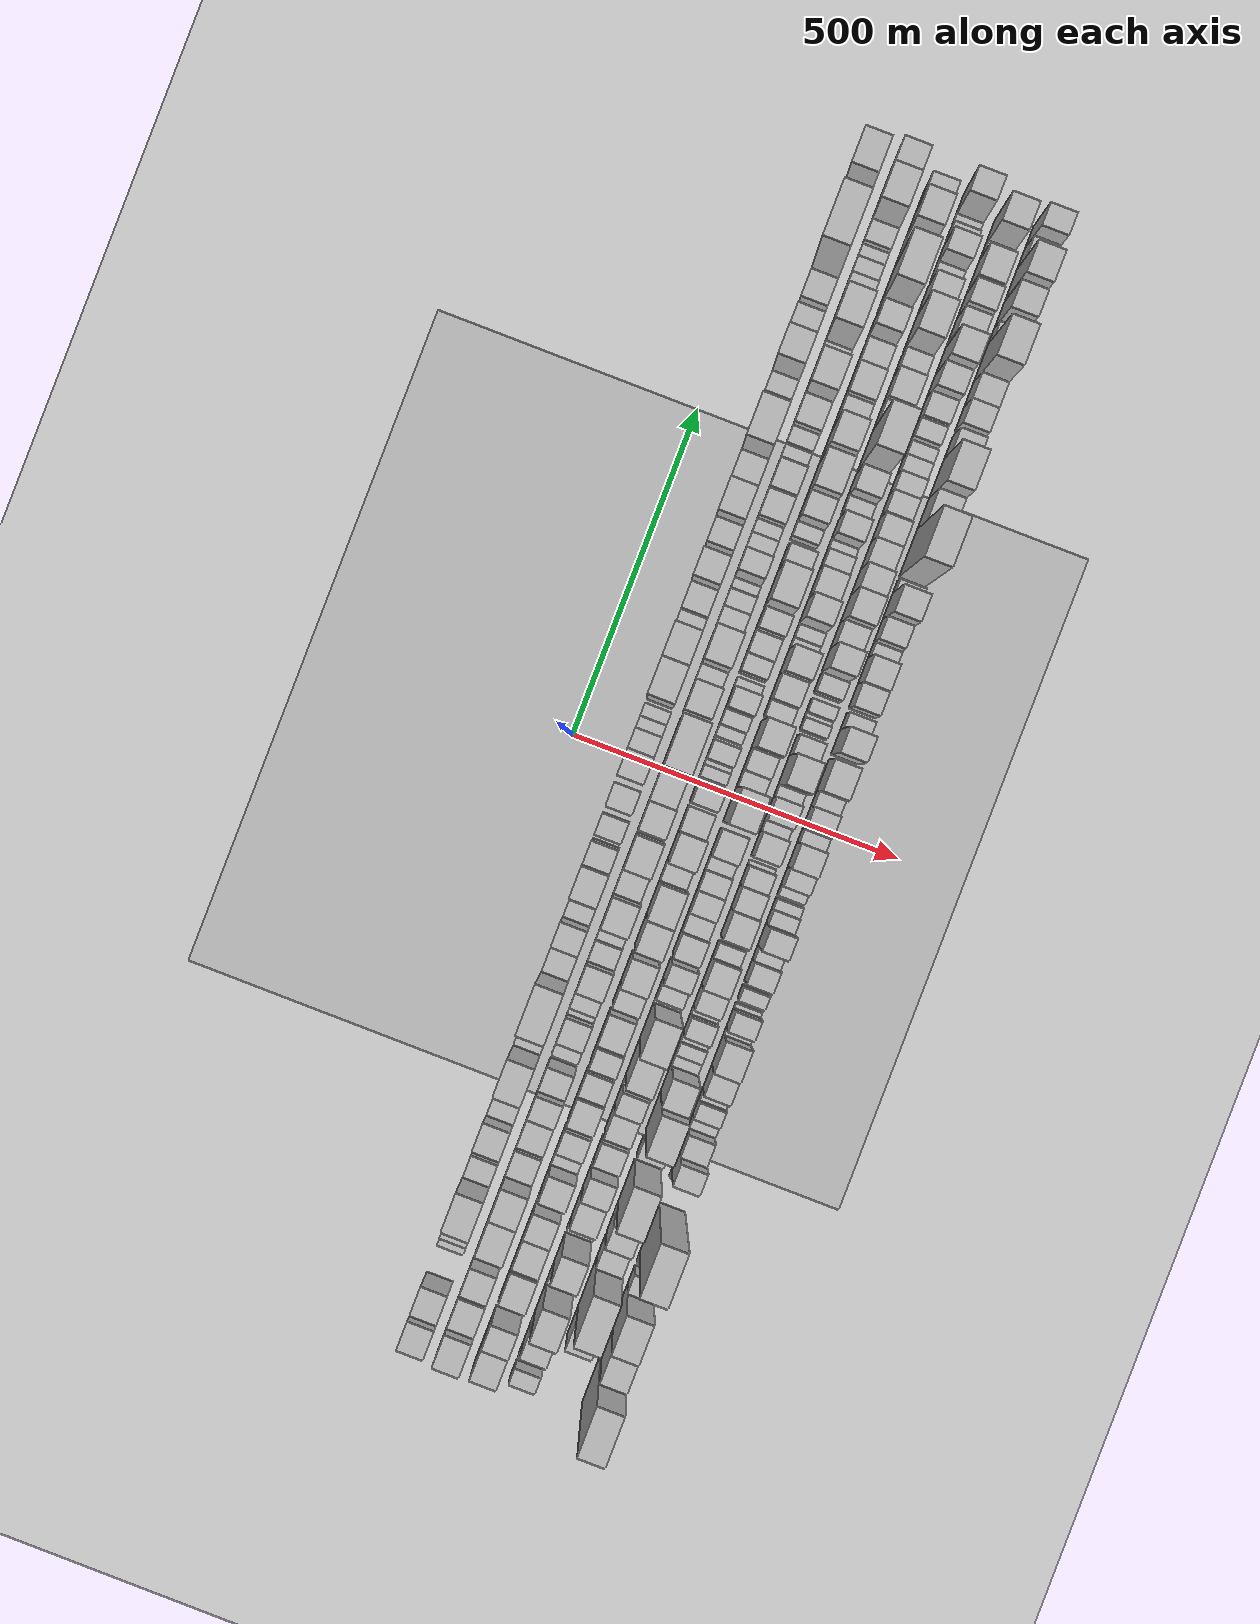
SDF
<?xml version="1.0" encoding="utf-8"?>

<sdf version="1.6">

   <world name="default">

      <gui fullscreen="0">

         <camera name="user_camera">

            <pose>-15 0 4.57585 0 0 0</pose>

            <view_controller>orbit</view_controller>

         </camera>

      </gui>

      <scene>

         <sky>

           <clouds>

             <speed>12</speed>

           </clouds>

         </sky>

         <ambient>0.4 0.4 0.4 1</ambient>

         <background>0.7 0.7 0.7 1</background>

         <shadows>1</shadows>

      </scene>

      <gravity>0 0 -9.8066</gravity>

      <magnetic_field>6e-06 2.3e-05 -4.2e-05</magnetic_field>

      <physics default="0" name="default_physics" type="ode">

         <ode>

            <solver>

               <type>quick</type>

               <iters>10</iters>

               <sor>1.0</sor>

               <use_dynamic_moi_rescaling>0</use_dynamic_moi_rescaling>

            </solver>

            <constraints>

               <cfm>0</cfm>

               <erp>0.2</erp>

               <contact_max_correcting_vel>100</contact_max_correcting_vel>

               <contact_surface_layer>0.001</contact_surface_layer>

            </constraints>

         </ode>

         <max_step_size>0.004</max_step_size>

         <real_time_factor>1</real_time_factor>

         <real_time_update_rate>250</real_time_update_rate>

      </physics>

      <light name="sun" type="directional">

         <cast_shadows>1</cast_shadows>

         <pose>0 0 10 0 0 0</pose>

         <diffuse>0.8 0.8 0.8 1</diffuse>

         <specular>0.2 0.2 0.2 1</specular>

         <attenuation>

            <range>1000</range>

            <constant>0.9</constant>

            <linear>0.01</linear>

            <quadratic>0.001</quadratic>

         </attenuation>

         <direction>-0.5 0.1 -0.9</direction>

      </light>

      <include>

         <name>ground_plane_1</name>

         <uri>model://HANNAS_ground_plane</uri>

         <pose>0 0 0  0 0 0</pose>

      </include>

      <include>

         <name>ground_plane_2</name>

         <uri>model://HANNAS_ground_plane</uri>

         <pose>100 0 0  0 0 0</pose>

      </include>

      <model name="building_1">

         <static>1</static>

         <pose frame="">100.0000 -868.0949 0 0.000000 0.000000 0.000000</pose>

         <link name="link">

            <pose frame="">0 0 37.50 0 0 0</pose>

            <collision name="collision">

               <geometry>

                  <box>

                     <size>40.0000 43.8102 75.0000</size>

                  </box>

               </geometry>

               <max_contacts>10</max_contacts>

               <surface>

                  <contact>

                     <ode/>

                  </contact>

                  <bounce/>

                  <friction>

                     <torsional>

                        <ode/>

                     </torsional>

                     <ode/>

                  </friction>

               </surface>

            </collision>

            <visual name="visual">

               <cast_shadows>0</cast_shadows>

               <geometry>

                  <box>

                     <size>40.0000 43.8102 75.0000</size>

                  </box>

               </geometry>

               <material>

                  <script>

                     <uri>model://HANNAS_wall/materials/scripts</uri>

                     <uri>model://HANNAS_wall/materials/textures</uri>

                     <name>vrc/HANNAS_wall</name>

                  </script>

               </material>

            </visual>

            <self_collide>0</self_collide>

            <enable_wind>0</enable_wind>

            <kinematic>0</kinematic>

         </link>

      </model>

      <model name="building_2">

         <static>1</static>

         <pose frame="">100.0000 -842.1908 0 0.000000 0.000000 0.000000</pose>

         <link name="link">

            <pose frame="">0 0 9.00 0 0 0</pose>

            <collision name="collision">

               <geometry>

                  <box>

                     <size>40.0000 7.9980 18.0000</size>

                  </box>

               </geometry>

               <max_contacts>10</max_contacts>

               <surface>

                  <contact>

                     <ode/>

                  </contact>

                  <bounce/>

                  <friction>

                     <torsional>

                        <ode/>

                     </torsional>

                     <ode/>

                  </friction>

               </surface>

            </collision>

            <visual name="visual">

               <cast_shadows>0</cast_shadows>

               <geometry>

                  <box>

                     <size>40.0000 7.9980 18.0000</size>

                  </box>

               </geometry>

               <material>

                  <script>

                     <uri>model://HANNAS_wall/materials/scripts</uri>

                     <uri>model://HANNAS_wall/materials/textures</uri>

                     <name>vrc/HANNAS_wall</name>

                  </script>

               </material>

            </visual>

            <self_collide>0</self_collide>

            <enable_wind>0</enable_wind>

            <kinematic>0</kinematic>

         </link>

      </model>

      <model name="building_3">

         <static>1</static>

         <pose frame="">100.0000 -816.2501 0 0.000000 0.000000 0.000000</pose>

         <link name="link">

            <pose frame="">0 0 37.50 0 0 0</pose>

            <collision name="collision">

               <geometry>

                  <box>

                     <size>40.0000 43.8835 75.0000</size>

                  </box>

               </geometry>

               <max_contacts>10</max_contacts>

               <surface>

                  <contact>

                     <ode/>

                  </contact>

                  <bounce/>

                  <friction>

                     <torsional>

                        <ode/>

                     </torsional>

                     <ode/>

                  </friction>

               </surface>

            </collision>

            <visual name="visual">

               <cast_shadows>0</cast_shadows>

               <geometry>

                  <box>

                     <size>40.0000 43.8835 75.0000</size>

                  </box>

               </geometry>

               <material>

                  <script>

                     <uri>model://HANNAS_wall/materials/scripts</uri>

                     <uri>model://HANNAS_wall/materials/textures</uri>

                     <name>vrc/HANNAS_wall</name>

                  </script>

               </material>

            </visual>

            <self_collide>0</self_collide>

            <enable_wind>0</enable_wind>

            <kinematic>0</kinematic>

         </link>

      </model>

      <model name="building_4">

         <static>1</static>

         <pose frame="">100.0000 -742.1931 0 0.000000 0.000000 0.000000</pose>

         <link name="link">

            <pose frame="">0 0 12.00 0 0 0</pose>

            <collision name="collision">

               <geometry>

                  <box>

                     <size>40.0000 10.7435 24.0000</size>

                  </box>

               </geometry>

               <max_contacts>10</max_contacts>

               <surface>

                  <contact>

                     <ode/>

                  </contact>

                  <bounce/>

                  <friction>

                     <torsional>

                        <ode/>

                     </torsional>

                     <ode/>

                  </friction>

               </surface>

            </collision>

            <visual name="visual">

               <cast_shadows>0</cast_shadows>

               <geometry>

                  <box>

                     <size>40.0000 10.7435 24.0000</size>

                  </box>

               </geometry>

               <material>

                  <script>

                     <uri>model://HANNAS_wall/materials/scripts</uri>

                     <uri>model://HANNAS_wall/materials/textures</uri>

                     <name>vrc/HANNAS_wall</name>

                  </script>

               </material>

            </visual>

            <self_collide>0</self_collide>

            <enable_wind>0</enable_wind>

            <kinematic>0</kinematic>

         </link>

      </model>

      <model name="building_5">

         <static>1</static>

         <pose frame="">100.0000 -710.1252 0 0.000000 0.000000 0.000000</pose>

         <link name="link">

            <pose frame="">0 0 30.00 0 0 0</pose>

            <collision name="collision">

               <geometry>

                  <box>

                     <size>40.0000 33.3923 60.0000</size>

                  </box>

               </geometry>

               <max_contacts>10</max_contacts>

               <surface>

                  <contact>

                     <ode/>

                  </contact>

                  <bounce/>

                  <friction>

                     <torsional>

                        <ode/>

                     </torsional>

                     <ode/>

                  </friction>

               </surface>

            </collision>

            <visual name="visual">

               <cast_shadows>0</cast_shadows>

               <geometry>

                  <box>

                     <size>40.0000 33.3923 60.0000</size>

                  </box>

               </geometry>

               <material>

                  <script>

                     <uri>model://HANNAS_wall/materials/scripts</uri>

                     <uri>model://HANNAS_wall/materials/textures</uri>

                     <name>vrc/HANNAS_wall</name>

                  </script>

               </material>

            </visual>

            <self_collide>0</self_collide>

            <enable_wind>0</enable_wind>

            <kinematic>0</kinematic>

         </link>

      </model>

      <model name="building_6">

         <static>1</static>

         <pose frame="">100.0000 -664.6134 0 0.000000 0.000000 0.000000</pose>

         <link name="link">

            <pose frame="">0 0 75.00 0 0 0</pose>

            <collision name="collision">

               <geometry>

                  <box>

                     <size>40.0000 57.6314 150.0000</size>

                  </box>

               </geometry>

               <max_contacts>10</max_contacts>

               <surface>

                  <contact>

                     <ode/>

                  </contact>

                  <bounce/>

                  <friction>

                     <torsional>

                        <ode/>

                     </torsional>

                     <ode/>

                  </friction>

               </surface>

            </collision>

            <visual name="visual">

               <cast_shadows>0</cast_shadows>

               <geometry>

                  <box>

                     <size>40.0000 57.6314 150.0000</size>

                  </box>

               </geometry>

               <material>

                  <script>

                     <uri>model://HANNAS_wall/materials/scripts</uri>

                     <uri>model://HANNAS_wall/materials/textures</uri>

                     <name>vrc/HANNAS_wall</name>

                  </script>

               </material>

            </visual>

            <self_collide>0</self_collide>

            <enable_wind>0</enable_wind>

            <kinematic>0</kinematic>

         </link>

      </model>

      <model name="building_7">

         <static>1</static>

         <pose frame="">100.0000 -619.4495 0 0.000000 0.000000 0.000000</pose>

         <link name="link">

            <pose frame="">0 0 28.50 0 0 0</pose>

            <collision name="collision">

               <geometry>

                  <box>

                     <size>40.0000 32.6963 57.0000</size>

                  </box>

               </geometry>

               <max_contacts>10</max_contacts>

               <surface>

                  <contact>

                     <ode/>

                  </contact>

                  <bounce/>

                  <friction>

                     <torsional>

                        <ode/>

                     </torsional>

                     <ode/>

                  </friction>

               </surface>

            </collision>

            <visual name="visual">

               <cast_shadows>0</cast_shadows>

               <geometry>

                  <box>

                     <size>40.0000 32.6963 57.0000</size>

                  </box>

               </geometry>

               <material>

                  <script>

                     <uri>model://HANNAS_wall/materials/scripts</uri>

                     <uri>model://HANNAS_wall/materials/textures</uri>

                     <name>vrc/HANNAS_wall</name>

                  </script>

               </material>

            </visual>

            <self_collide>0</self_collide>

            <enable_wind>0</enable_wind>

            <kinematic>0</kinematic>

         </link>

      </model>

      <model name="building_8">

         <static>1</static>

         <pose frame="">100.0000 -589.8575 0 0.000000 0.000000 0.000000</pose>

         <link name="link">

            <pose frame="">0 0 13.50 0 0 0</pose>

            <collision name="collision">

               <geometry>

                  <box>

                     <size>40.0000 12.4877 27.0000</size>

                  </box>

               </geometry>

               <max_contacts>10</max_contacts>

               <surface>

                  <contact>

                     <ode/>

                  </contact>

                  <bounce/>

                  <friction>

                     <torsional>

                        <ode/>

                     </torsional>

                     <ode/>

                  </friction>

               </surface>

            </collision>

            <visual name="visual">

               <cast_shadows>0</cast_shadows>

               <geometry>

                  <box>

                     <size>40.0000 12.4877 27.0000</size>

                  </box>

               </geometry>

               <material>

                  <script>

                     <uri>model://HANNAS_wall/materials/scripts</uri>

                     <uri>model://HANNAS_wall/materials/textures</uri>

                     <name>vrc/HANNAS_wall</name>

                  </script>

               </material>

            </visual>

            <self_collide>0</self_collide>

            <enable_wind>0</enable_wind>

            <kinematic>0</kinematic>

         </link>

      </model>

      <model name="building_9">

         <static>1</static>

         <pose frame="">100.0000 -562.2363 0 0.000000 0.000000 0.000000</pose>

         <link name="link">

            <pose frame="">0 0 60.00 0 0 0</pose>

            <collision name="collision">

               <geometry>

                  <box>

                     <size>40.0000 42.7547 120.0000</size>

                  </box>

               </geometry>

               <max_contacts>10</max_contacts>

               <surface>

                  <contact>

                     <ode/>

                  </contact>

                  <bounce/>

                  <friction>

                     <torsional>

                        <ode/>

                     </torsional>

                     <ode/>

                  </friction>

               </surface>

            </collision>

            <visual name="visual">

               <cast_shadows>0</cast_shadows>

               <geometry>

                  <box>

                     <size>40.0000 42.7547 120.0000</size>

                  </box>

               </geometry>

               <material>

                  <script>

                     <uri>model://HANNAS_wall/materials/scripts</uri>

                     <uri>model://HANNAS_wall/materials/textures</uri>

                     <name>vrc/HANNAS_wall</name>

                  </script>

               </material>

            </visual>

            <self_collide>0</self_collide>

            <enable_wind>0</enable_wind>

            <kinematic>0</kinematic>

         </link>

      </model>

      <model name="building_10">

         <static>1</static>

         <pose frame="">100.0000 -521.3223 0 0.000000 0.000000 0.000000</pose>

         <link name="link">

            <pose frame="">0 0 33.00 0 0 0</pose>

            <collision name="collision">

               <geometry>

                  <box>

                     <size>40.0000 39.0733 66.0000</size>

                  </box>

               </geometry>

               <max_contacts>10</max_contacts>

               <surface>

                  <contact>

                     <ode/>

                  </contact>

                  <bounce/>

                  <friction>

                     <torsional>

                        <ode/>

                     </torsional>

                     <ode/>

                  </friction>

               </surface>

            </collision>

            <visual name="visual">

               <cast_shadows>0</cast_shadows>

               <geometry>

                  <box>

                     <size>40.0000 39.0733 66.0000</size>

                  </box>

               </geometry>

               <material>

                  <script>

                     <uri>model://HANNAS_wall/materials/scripts</uri>

                     <uri>model://HANNAS_wall/materials/textures</uri>

                     <name>vrc/HANNAS_wall</name>

                  </script>

               </material>

            </visual>

            <self_collide>0</self_collide>

            <enable_wind>0</enable_wind>

            <kinematic>0</kinematic>

         </link>

      </model>

      <model name="building_11">

         <static>1</static>

         <pose frame="">100.0000 -470.6556 0 0.000000 0.000000 0.000000</pose>

         <link name="link">

            <pose frame="">0 0 75.00 0 0 0</pose>

            <collision name="collision">

               <geometry>

                  <box>

                     <size>40.0000 56.2600 150.0000</size>

                  </box>

               </geometry>

               <max_contacts>10</max_contacts>

               <surface>

                  <contact>

                     <ode/>

                  </contact>

                  <bounce/>

                  <friction>

                     <torsional>

                        <ode/>

                     </torsional>

                     <ode/>

                  </friction>

               </surface>

            </collision>

            <visual name="visual">

               <cast_shadows>0</cast_shadows>

               <geometry>

                  <box>

                     <size>40.0000 56.2600 150.0000</size>

                  </box>

               </geometry>

               <material>

                  <script>

                     <uri>model://HANNAS_wall/materials/scripts</uri>

                     <uri>model://HANNAS_wall/materials/textures</uri>

                     <name>vrc/HANNAS_wall</name>

                  </script>

               </material>

            </visual>

            <self_collide>0</self_collide>

            <enable_wind>0</enable_wind>

            <kinematic>0</kinematic>

         </link>

      </model>

      <model name="building_12">

         <static>1</static>

         <pose frame="">100.0000 -416.0842 0 0.000000 0.000000 0.000000</pose>

         <link name="link">

            <pose frame="">0 0 36.00 0 0 0</pose>

            <collision name="collision">

               <geometry>

                  <box>

                     <size>40.0000 36.8828 72.0000</size>

                  </box>

               </geometry>

               <max_contacts>10</max_contacts>

               <surface>

                  <contact>

                     <ode/>

                  </contact>

                  <bounce/>

                  <friction>

                     <torsional>

                        <ode/>

                     </torsional>

                     <ode/>

                  </friction>

               </surface>

            </collision>

            <visual name="visual">

               <cast_shadows>0</cast_shadows>

               <geometry>

                  <box>

                     <size>40.0000 36.8828 72.0000</size>

                  </box>

               </geometry>

               <material>

                  <script>

                     <uri>model://HANNAS_wall/materials/scripts</uri>

                     <uri>model://HANNAS_wall/materials/textures</uri>

                     <name>vrc/HANNAS_wall</name>

                  </script>

               </material>

            </visual>

            <self_collide>0</self_collide>

            <enable_wind>0</enable_wind>

            <kinematic>0</kinematic>

         </link>

      </model>

      <model name="building_13">

         <static>1</static>

         <pose frame="">100.0000 -361.1440 0 0.000000 0.000000 0.000000</pose>

         <link name="link">

            <pose frame="">0 0 112.50 0 0 0</pose>

            <collision name="collision">

               <geometry>

                  <box>

                     <size>40.0000 72.9977 225.0000</size>

                  </box>

               </geometry>

               <max_contacts>10</max_contacts>

               <surface>

                  <contact>

                     <ode/>

                  </contact>

                  <bounce/>

                  <friction>

                     <torsional>

                        <ode/>

                     </torsional>

                     <ode/>

                  </friction>

               </surface>

            </collision>

            <visual name="visual">

               <cast_shadows>0</cast_shadows>

               <geometry>

                  <box>

                     <size>40.0000 72.9977 225.0000</size>

                  </box>

               </geometry>

               <material>

                  <script>

                     <uri>model://HANNAS_wall/materials/scripts</uri>

                     <uri>model://HANNAS_wall/materials/textures</uri>

                     <name>vrc/HANNAS_wall</name>

                  </script>

               </material>

            </visual>

            <self_collide>0</self_collide>

            <enable_wind>0</enable_wind>

            <kinematic>0</kinematic>

         </link>

      </model>

      <model name="building_14">

         <static>1</static>

         <pose frame="">100.0000 -305.2426 0 0.000000 0.000000 0.000000</pose>

         <link name="link">

            <pose frame="">0 0 37.50 0 0 0</pose>

            <collision name="collision">

               <geometry>

                  <box>

                     <size>40.0000 38.8052 75.0000</size>

                  </box>

               </geometry>

               <max_contacts>10</max_contacts>

               <surface>

                  <contact>

                     <ode/>

                  </contact>

                  <bounce/>

                  <friction>

                     <torsional>

                        <ode/>

                     </torsional>

                     <ode/>

                  </friction>

               </surface>

            </collision>

            <visual name="visual">

               <cast_shadows>0</cast_shadows>

               <geometry>

                  <box>

                     <size>40.0000 38.8052 75.0000</size>

                  </box>

               </geometry>

               <material>

                  <script>

                     <uri>model://HANNAS_wall/materials/scripts</uri>

                     <uri>model://HANNAS_wall/materials/textures</uri>

                     <name>vrc/HANNAS_wall</name>

                  </script>

               </material>

            </visual>

            <self_collide>0</self_collide>

            <enable_wind>0</enable_wind>

            <kinematic>0</kinematic>

         </link>

      </model>

      <model name="building_15">

         <static>1</static>

         <pose frame="">100.0000 -266.9520 0 0.000000 0.000000 0.000000</pose>

         <link name="link">

            <pose frame="">0 0 51.00 0 0 0</pose>

            <collision name="collision">

               <geometry>

                  <box>

                     <size>40.0000 37.7759 102.0000</size>

                  </box>

               </geometry>

               <max_contacts>10</max_contacts>

               <surface>

                  <contact>

                     <ode/>

                  </contact>

                  <bounce/>

                  <friction>

                     <torsional>

                        <ode/>

                     </torsional>

                     <ode/>

                  </friction>

               </surface>

            </collision>

            <visual name="visual">

               <cast_shadows>0</cast_shadows>

               <geometry>

                  <box>

                     <size>40.0000 37.7759 102.0000</size>

                  </box>

               </geometry>

               <material>

                  <script>

                     <uri>model://HANNAS_wall/materials/scripts</uri>

                     <uri>model://HANNAS_wall/materials/textures</uri>

                     <name>vrc/HANNAS_wall</name>

                  </script>

               </material>

            </visual>

            <self_collide>0</self_collide>

            <enable_wind>0</enable_wind>

            <kinematic>0</kinematic>

         </link>

      </model>

      <model name="building_16">

         <static>1</static>

         <pose frame="">100.0000 -232.2471 0 0.000000 0.000000 0.000000</pose>

         <link name="link">

            <pose frame="">0 0 22.50 0 0 0</pose>

            <collision name="collision">

               <geometry>

                  <box>

                     <size>40.0000 25.6339 45.0000</size>

                  </box>

               </geometry>

               <max_contacts>10</max_contacts>

               <surface>

                  <contact>

                     <ode/>

                  </contact>

                  <bounce/>

                  <friction>

                     <torsional>

                        <ode/>

                     </torsional>

                     <ode/>

                  </friction>

               </surface>

            </collision>

            <visual name="visual">

               <cast_shadows>0</cast_shadows>

               <geometry>

                  <box>

                     <size>40.0000 25.6339 45.0000</size>

                  </box>

               </geometry>

               <material>

                  <script>

                     <uri>model://HANNAS_wall/materials/scripts</uri>

                     <uri>model://HANNAS_wall/materials/textures</uri>

                     <name>vrc/HANNAS_wall</name>

                  </script>

               </material>

            </visual>

            <self_collide>0</self_collide>

            <enable_wind>0</enable_wind>

            <kinematic>0</kinematic>

         </link>

      </model>

      <model name="building_17">

         <static>1</static>

         <pose frame="">100.0000 -187.3344 0 0.000000 0.000000 0.000000</pose>

         <link name="link">

            <pose frame="">0 0 72.00 0 0 0</pose>

            <collision name="collision">

               <geometry>

                  <box>

                     <size>40.0000 48.1916 144.0000</size>

                  </box>

               </geometry>

               <max_contacts>10</max_contacts>

               <surface>

                  <contact>

                     <ode/>

                  </contact>

                  <bounce/>

                  <friction>

                     <torsional>

                        <ode/>

                     </torsional>

                     <ode/>

                  </friction>

               </surface>

            </collision>

            <visual name="visual">

               <cast_shadows>0</cast_shadows>

               <geometry>

                  <box>

                     <size>40.0000 48.1916 144.0000</size>

                  </box>

               </geometry>

               <material>

                  <script>

                     <uri>model://HANNAS_wall/materials/scripts</uri>

                     <uri>model://HANNAS_wall/materials/textures</uri>

                     <name>vrc/HANNAS_wall</name>

                  </script>

               </material>

            </visual>

            <self_collide>0</self_collide>

            <enable_wind>0</enable_wind>

            <kinematic>0</kinematic>

         </link>

      </model>

      <model name="building_18">

         <static>1</static>

         <pose frame="">100.0000 -145.5339 0 0.000000 0.000000 0.000000</pose>

         <link name="link">

            <pose frame="">0 0 55.50 0 0 0</pose>

            <collision name="collision">

               <geometry>

                  <box>

                     <size>40.0000 35.4094 111.0000</size>

                  </box>

               </geometry>

               <max_contacts>10</max_contacts>

               <surface>

                  <contact>

                     <ode/>

                  </contact>

                  <bounce/>

                  <friction>

                     <torsional>

                        <ode/>

                     </torsional>

                     <ode/>

                  </friction>

               </surface>

            </collision>

            <visual name="visual">

               <cast_shadows>0</cast_shadows>

               <geometry>

                  <box>

                     <size>40.0000 35.4094 111.0000</size>

                  </box>

               </geometry>

               <material>

                  <script>

                     <uri>model://HANNAS_wall/materials/scripts</uri>

                     <uri>model://HANNAS_wall/materials/textures</uri>

                     <name>vrc/HANNAS_wall</name>

                  </script>

               </material>

            </visual>

            <self_collide>0</self_collide>

            <enable_wind>0</enable_wind>

            <kinematic>0</kinematic>

         </link>

      </model>

      <model name="building_19">

         <static>1</static>

         <pose frame="">100.0000 -104.4005 0 0.000000 0.000000 0.000000</pose>

         <link name="link">

            <pose frame="">0 0 31.50 0 0 0</pose>

            <collision name="collision">

               <geometry>

                  <box>

                     <size>40.0000 32.8574 63.0000</size>

                  </box>

               </geometry>

               <max_contacts>10</max_contacts>

               <surface>

                  <contact>

                     <ode/>

                  </contact>

                  <bounce/>

                  <friction>

                     <torsional>

                        <ode/>

                     </torsional>

                     <ode/>

                  </friction>

               </surface>

            </collision>

            <visual name="visual">

               <cast_shadows>0</cast_shadows>

               <geometry>

                  <box>

                     <size>40.0000 32.8574 63.0000</size>

                  </box>

               </geometry>

               <material>

                  <script>

                     <uri>model://HANNAS_wall/materials/scripts</uri>

                     <uri>model://HANNAS_wall/materials/textures</uri>

                     <name>vrc/HANNAS_wall</name>

                  </script>

               </material>

            </visual>

            <self_collide>0</self_collide>

            <enable_wind>0</enable_wind>

            <kinematic>0</kinematic>

         </link>

      </model>

      <model name="building_20">

         <static>1</static>

         <pose frame="">100.0000 -59.7852 0 0.000000 0.000000 0.000000</pose>

         <link name="link">

            <pose frame="">0 0 31.50 0 0 0</pose>

            <collision name="collision">

               <geometry>

                  <box>

                     <size>40.0000 36.3732 63.0000</size>

                  </box>

               </geometry>

               <max_contacts>10</max_contacts>

               <surface>

                  <contact>

                     <ode/>

                  </contact>

                  <bounce/>

                  <friction>

                     <torsional>

                        <ode/>

                     </torsional>

                     <ode/>

                  </friction>

               </surface>

            </collision>

            <visual name="visual">

               <cast_shadows>0</cast_shadows>

               <geometry>

                  <box>

                     <size>40.0000 36.3732 63.0000</size>

                  </box>

               </geometry>

               <material>

                  <script>

                     <uri>model://HANNAS_wall/materials/scripts</uri>

                     <uri>model://HANNAS_wall/materials/textures</uri>

                     <name>vrc/HANNAS_wall</name>

                  </script>

               </material>

            </visual>

            <self_collide>0</self_collide>

            <enable_wind>0</enable_wind>

            <kinematic>0</kinematic>

         </link>

      </model>

      <model name="building_21">

         <static>1</static>

         <pose frame="">100.0000 -11.1087 0 0.000000 0.000000 0.000000</pose>

         <link name="link">

            <pose frame="">0 0 40.50 0 0 0</pose>

            <collision name="collision">

               <geometry>

                  <box>

                     <size>40.0000 40.9799 81.0000</size>

                  </box>

               </geometry>

               <max_contacts>10</max_contacts>

               <surface>

                  <contact>

                     <ode/>

                  </contact>

                  <bounce/>

                  <friction>

                     <torsional>

                        <ode/>

                     </torsional>

                     <ode/>

                  </friction>

               </surface>

            </collision>

            <visual name="visual">

               <cast_shadows>0</cast_shadows>

               <geometry>

                  <box>

                     <size>40.0000 40.9799 81.0000</size>

                  </box>

               </geometry>

               <material>

                  <script>

                     <uri>model://HANNAS_wall/materials/scripts</uri>

                     <uri>model://HANNAS_wall/materials/textures</uri>

                     <name>vrc/HANNAS_wall</name>

                  </script>

               </material>

            </visual>

            <self_collide>0</self_collide>

            <enable_wind>0</enable_wind>

            <kinematic>0</kinematic>

         </link>

      </model>

      <model name="building_22">

         <static>1</static>

         <pose frame="">100.0000 24.9783 0 0.000000 0.000000 0.000000</pose>

         <link name="link">

            <pose frame="">0 0 28.50 0 0 0</pose>

            <collision name="collision">

               <geometry>

                  <box>

                     <size>40.0000 31.1941 57.0000</size>

                  </box>

               </geometry>

               <max_contacts>10</max_contacts>

               <surface>

                  <contact>

                     <ode/>

                  </contact>

                  <bounce/>

                  <friction>

                     <torsional>

                        <ode/>

                     </torsional>

                     <ode/>

                  </friction>

               </surface>

            </collision>

            <visual name="visual">

               <cast_shadows>0</cast_shadows>

               <geometry>

                  <box>

                     <size>40.0000 31.1941 57.0000</size>

                  </box>

               </geometry>

               <material>

                  <script>

                     <uri>model://HANNAS_wall/materials/scripts</uri>

                     <uri>model://HANNAS_wall/materials/textures</uri>

                     <name>vrc/HANNAS_wall</name>

                  </script>

               </material>

            </visual>

            <self_collide>0</self_collide>

            <enable_wind>0</enable_wind>

            <kinematic>0</kinematic>

         </link>

      </model>

      <model name="building_23">

         <static>1</static>

         <pose frame="">100.0000 49.8921 0 0.000000 0.000000 0.000000</pose>

         <link name="link">

            <pose frame="">0 0 16.50 0 0 0</pose>

            <collision name="collision">

               <geometry>

                  <box>

                     <size>40.0000 18.6336 33.0000</size>

                  </box>

               </geometry>

               <max_contacts>10</max_contacts>

               <surface>

                  <contact>

                     <ode/>

                  </contact>

                  <bounce/>

                  <friction>

                     <torsional>

                        <ode/>

                     </torsional>

                     <ode/>

                  </friction>

               </surface>

            </collision>

            <visual name="visual">

               <cast_shadows>0</cast_shadows>

               <geometry>

                  <box>

                     <size>40.0000 18.6336 33.0000</size>

                  </box>

               </geometry>

               <material>

                  <script>

                     <uri>model://HANNAS_wall/materials/scripts</uri>

                     <uri>model://HANNAS_wall/materials/textures</uri>

                     <name>vrc/HANNAS_wall</name>

                  </script>

               </material>

            </visual>

            <self_collide>0</self_collide>

            <enable_wind>0</enable_wind>

            <kinematic>0</kinematic>

         </link>

      </model>

      <model name="building_24">

         <static>1</static>

         <pose frame="">100.0000 68.9714 0 0.000000 0.000000 0.000000</pose>

         <link name="link">

            <pose frame="">0 0 18.00 0 0 0</pose>

            <collision name="collision">

               <geometry>

                  <box>

                     <size>40.0000 19.5249 36.0000</size>

                  </box>

               </geometry>

               <max_contacts>10</max_contacts>

               <surface>

                  <contact>

                     <ode/>

                  </contact>

                  <bounce/>

                  <friction>

                     <torsional>

                        <ode/>

                     </torsional>

                     <ode/>

                  </friction>

               </surface>

            </collision>

            <visual name="visual">

               <cast_shadows>0</cast_shadows>

               <geometry>

                  <box>

                     <size>40.0000 19.5249 36.0000</size>

                  </box>

               </geometry>

               <material>

                  <script>

                     <uri>model://HANNAS_wall/materials/scripts</uri>

                     <uri>model://HANNAS_wall/materials/textures</uri>

                     <name>vrc/HANNAS_wall</name>

                  </script>

               </material>

            </visual>

            <self_collide>0</self_collide>

            <enable_wind>0</enable_wind>

            <kinematic>0</kinematic>

         </link>

      </model>

      <model name="building_25">

         <static>1</static>

         <pose frame="">100.0000 113.5776 0 0.000000 0.000000 0.000000</pose>

         <link name="link">

            <pose frame="">0 0 72.00 0 0 0</pose>

            <collision name="collision">

               <geometry>

                  <box>

                     <size>40.0000 55.6874 144.0000</size>

                  </box>

               </geometry>

               <max_contacts>10</max_contacts>

               <surface>

                  <contact>

                     <ode/>

                  </contact>

                  <bounce/>

                  <friction>

                     <torsional>

                        <ode/>

                     </torsional>

                     <ode/>

                  </friction>

               </surface>

            </collision>

            <visual name="visual">

               <cast_shadows>0</cast_shadows>

               <geometry>

                  <box>

                     <size>40.0000 55.6874 144.0000</size>

                  </box>

               </geometry>

               <material>

                  <script>

                     <uri>model://HANNAS_wall/materials/scripts</uri>

                     <uri>model://HANNAS_wall/materials/textures</uri>

                     <name>vrc/HANNAS_wall</name>

                  </script>

               </material>

            </visual>

            <self_collide>0</self_collide>

            <enable_wind>0</enable_wind>

            <kinematic>0</kinematic>

         </link>

      </model>

      <model name="building_26">

         <static>1</static>

         <pose frame="">100.0000 166.6663 0 0.000000 0.000000 0.000000</pose>

         <link name="link">

            <pose frame="">0 0 75.00 0 0 0</pose>

            <collision name="collision">

               <geometry>

                  <box>

                     <size>40.0000 50.4901 150.0000</size>

                  </box>

               </geometry>

               <max_contacts>10</max_contacts>

               <surface>

                  <contact>

                     <ode/>

                  </contact>

                  <bounce/>

                  <friction>

                     <torsional>

                        <ode/>

                     </torsional>

                     <ode/>

                  </friction>

               </surface>

            </collision>

            <visual name="visual">

               <cast_shadows>0</cast_shadows>

               <geometry>

                  <box>

                     <size>40.0000 50.4901 150.0000</size>

                  </box>

               </geometry>

               <material>

                  <script>

                     <uri>model://HANNAS_wall/materials/scripts</uri>

                     <uri>model://HANNAS_wall/materials/textures</uri>

                     <name>vrc/HANNAS_wall</name>

                  </script>

               </material>

            </visual>

            <self_collide>0</self_collide>

            <enable_wind>0</enable_wind>

            <kinematic>0</kinematic>

         </link>

      </model>

      <model name="building_27">

         <static>1</static>

         <pose frame="">100.0000 205.6077 0 0.000000 0.000000 0.000000</pose>

         <link name="link">

            <pose frame="">0 0 25.50 0 0 0</pose>

            <collision name="collision">

               <geometry>

                  <box>

                     <size>40.0000 27.3926 51.0000</size>

                  </box>

               </geometry>

               <max_contacts>10</max_contacts>

               <surface>

                  <contact>

                     <ode/>

                  </contact>

                  <bounce/>

                  <friction>

                     <torsional>

                        <ode/>

                     </torsional>

                     <ode/>

                  </friction>

               </surface>

            </collision>

            <visual name="visual">

               <cast_shadows>0</cast_shadows>

               <geometry>

                  <box>

                     <size>40.0000 27.3926 51.0000</size>

                  </box>

               </geometry>

               <material>

                  <script>

                     <uri>model://HANNAS_wall/materials/scripts</uri>

                     <uri>model://HANNAS_wall/materials/textures</uri>

                     <name>vrc/HANNAS_wall</name>

                  </script>

               </material>

            </visual>

            <self_collide>0</self_collide>

            <enable_wind>0</enable_wind>

            <kinematic>0</kinematic>

         </link>

      </model>

      <model name="building_28">

         <static>1</static>

         <pose frame="">100.0000 239.4895 0 0.000000 0.000000 0.000000</pose>

         <link name="link">

            <pose frame="">0 0 34.50 0 0 0</pose>

            <collision name="collision">

               <geometry>

                  <box>

                     <size>40.0000 40.3711 69.0000</size>

                  </box>

               </geometry>

               <max_contacts>10</max_contacts>

               <surface>

                  <contact>

                     <ode/>

                  </contact>

                  <bounce/>

                  <friction>

                     <torsional>

                        <ode/>

                     </torsional>

                     <ode/>

                  </friction>

               </surface>

            </collision>

            <visual name="visual">

               <cast_shadows>0</cast_shadows>

               <geometry>

                  <box>

                     <size>40.0000 40.3711 69.0000</size>

                  </box>

               </geometry>

               <material>

                  <script>

                     <uri>model://HANNAS_wall/materials/scripts</uri>

                     <uri>model://HANNAS_wall/materials/textures</uri>

                     <name>vrc/HANNAS_wall</name>

                  </script>

               </material>

            </visual>

            <self_collide>0</self_collide>

            <enable_wind>0</enable_wind>

            <kinematic>0</kinematic>

         </link>

      </model>

      <model name="building_29">

         <static>1</static>

         <pose frame="">100.0000 280.6004 0 0.000000 0.000000 0.000000</pose>

         <link name="link">

            <pose frame="">0 0 67.50 0 0 0</pose>

            <collision name="collision">

               <geometry>

                  <box>

                     <size>40.0000 41.8506 135.0000</size>

                  </box>

               </geometry>

               <max_contacts>10</max_contacts>

               <surface>

                  <contact>

                     <ode/>

                  </contact>

                  <bounce/>

                  <friction>

                     <torsional>

                        <ode/>

                     </torsional>

                     <ode/>

                  </friction>

               </surface>

            </collision>

            <visual name="visual">

               <cast_shadows>0</cast_shadows>

               <geometry>

                  <box>

                     <size>40.0000 41.8506 135.0000</size>

                  </box>

               </geometry>

               <material>

                  <script>

                     <uri>model://HANNAS_wall/materials/scripts</uri>

                     <uri>model://HANNAS_wall/materials/textures</uri>

                     <name>vrc/HANNAS_wall</name>

                  </script>

               </material>

            </visual>

            <self_collide>0</self_collide>

            <enable_wind>0</enable_wind>

            <kinematic>0</kinematic>

         </link>

      </model>

      <model name="building_30">

         <static>1</static>

         <pose frame="">100.0000 315.0890 0 0.000000 0.000000 0.000000</pose>

         <link name="link">

            <pose frame="">0 0 7.50 0 0 0</pose>

            <collision name="collision">

               <geometry>

                  <box>

                     <size>40.0000 7.1265 15.0000</size>

                  </box>

               </geometry>

               <max_contacts>10</max_contacts>

               <surface>

                  <contact>

                     <ode/>

                  </contact>

                  <bounce/>

                  <friction>

                     <torsional>

                        <ode/>

                     </torsional>

                     <ode/>

                  </friction>

               </surface>

            </collision>

            <visual name="visual">

               <cast_shadows>0</cast_shadows>

               <geometry>

                  <box>

                     <size>40.0000 7.1265 15.0000</size>

                  </box>

               </geometry>

               <material>

                  <script>

                     <uri>model://HANNAS_wall/materials/scripts</uri>

                     <uri>model://HANNAS_wall/materials/textures</uri>

                     <name>vrc/HANNAS_wall</name>

                  </script>

               </material>

            </visual>

            <self_collide>0</self_collide>

            <enable_wind>0</enable_wind>

            <kinematic>0</kinematic>

         </link>

      </model>

      <model name="building_31">

         <static>1</static>

         <pose frame="">100.0000 337.2113 0 0.000000 0.000000 0.000000</pose>

         <link name="link">

            <pose frame="">0 0 36.00 0 0 0</pose>

            <collision name="collision">

               <geometry>

                  <box>

                     <size>40.0000 37.1180 72.0000</size>

                  </box>

               </geometry>

               <max_contacts>10</max_contacts>

               <surface>

                  <contact>

                     <ode/>

                  </contact>

                  <bounce/>

                  <friction>

                     <torsional>

                        <ode/>

                     </torsional>

                     <ode/>

                  </friction>

               </surface>

            </collision>

            <visual name="visual">

               <cast_shadows>0</cast_shadows>

               <geometry>

                  <box>

                     <size>40.0000 37.1180 72.0000</size>

                  </box>

               </geometry>

               <material>

                  <script>

                     <uri>model://HANNAS_wall/materials/scripts</uri>

                     <uri>model://HANNAS_wall/materials/textures</uri>

                     <name>vrc/HANNAS_wall</name>

                  </script>

               </material>

            </visual>

            <self_collide>0</self_collide>

            <enable_wind>0</enable_wind>

            <kinematic>0</kinematic>

         </link>

      </model>

      <model name="building_32">

         <static>1</static>

         <pose frame="">100.0000 380.3562 0 0.000000 0.000000 0.000000</pose>

         <link name="link">

            <pose frame="">0 0 64.50 0 0 0</pose>

            <collision name="collision">

               <geometry>

                  <box>

                     <size>40.0000 49.1719 129.0000</size>

                  </box>

               </geometry>

               <max_contacts>10</max_contacts>

               <surface>

                  <contact>

                     <ode/>

                  </contact>

                  <bounce/>

                  <friction>

                     <torsional>

                        <ode/>

                     </torsional>

                     <ode/>

                  </friction>

               </surface>

            </collision>

            <visual name="visual">

               <cast_shadows>0</cast_shadows>

               <geometry>

                  <box>

                     <size>40.0000 49.1719 129.0000</size>

                  </box>

               </geometry>

               <material>

                  <script>

                     <uri>model://HANNAS_wall/materials/scripts</uri>

                     <uri>model://HANNAS_wall/materials/textures</uri>

                     <name>vrc/HANNAS_wall</name>

                  </script>

               </material>

            </visual>

            <self_collide>0</self_collide>

            <enable_wind>0</enable_wind>

            <kinematic>0</kinematic>

         </link>

      </model>

      <model name="building_33">

         <static>1</static>

         <pose frame="">100.0000 426.1538 0 0.000000 0.000000 0.000000</pose>

         <link name="link">

            <pose frame="">0 0 55.50 0 0 0</pose>

            <collision name="collision">

               <geometry>

                  <box>

                     <size>40.0000 42.4232 111.0000</size>

                  </box>

               </geometry>

               <max_contacts>10</max_contacts>

               <surface>

                  <contact>

                     <ode/>

                  </contact>

                  <bounce/>

                  <friction>

                     <torsional>

                        <ode/>

                     </torsional>

                     <ode/>

                  </friction>

               </surface>

            </collision>

            <visual name="visual">

               <cast_shadows>0</cast_shadows>

               <geometry>

                  <box>

                     <size>40.0000 42.4232 111.0000</size>

                  </box>

               </geometry>

               <material>

                  <script>

                     <uri>model://HANNAS_wall/materials/scripts</uri>

                     <uri>model://HANNAS_wall/materials/textures</uri>

                     <name>vrc/HANNAS_wall</name>

                  </script>

               </material>

            </visual>

            <self_collide>0</self_collide>

            <enable_wind>0</enable_wind>

            <kinematic>0</kinematic>

         </link>

      </model>

      <model name="building_34">

         <static>1</static>

         <pose frame="">100.0000 450.9216 0 0.000000 0.000000 0.000000</pose>

         <link name="link">

            <pose frame="">0 0 7.50 0 0 0</pose>

            <collision name="collision">

               <geometry>

                  <box>

                     <size>40.0000 7.1123 15.0000</size>

                  </box>

               </geometry>

               <max_contacts>10</max_contacts>

               <surface>

                  <contact>

                     <ode/>

                  </contact>

                  <bounce/>

                  <friction>

                     <torsional>

                        <ode/>

                     </torsional>

                     <ode/>

                  </friction>

               </surface>

            </collision>

            <visual name="visual">

               <cast_shadows>0</cast_shadows>

               <geometry>

                  <box>

                     <size>40.0000 7.1123 15.0000</size>

                  </box>

               </geometry>

               <material>

                  <script>

                     <uri>model://HANNAS_wall/materials/scripts</uri>

                     <uri>model://HANNAS_wall/materials/textures</uri>

                     <name>vrc/HANNAS_wall</name>

                  </script>

               </material>

            </visual>

            <self_collide>0</self_collide>

            <enable_wind>0</enable_wind>

            <kinematic>0</kinematic>

         </link>

      </model>

      <model name="building_35">

         <static>1</static>

         <pose frame="">100.0000 485.5800 0 0.000000 0.000000 0.000000</pose>

         <link name="link">

            <pose frame="">0 0 88.50 0 0 0</pose>

            <collision name="collision">

               <geometry>

                  <box>

                     <size>40.0000 62.2045 177.0000</size>

                  </box>

               </geometry>

               <max_contacts>10</max_contacts>

               <surface>

                  <contact>

                     <ode/>

                  </contact>

                  <bounce/>

                  <friction>

                     <torsional>

                        <ode/>

                     </torsional>

                     <ode/>

                  </friction>

               </surface>

            </collision>

            <visual name="visual">

               <cast_shadows>0</cast_shadows>

               <geometry>

                  <box>

                     <size>40.0000 62.2045 177.0000</size>

                  </box>

               </geometry>

               <material>

                  <script>

                     <uri>model://HANNAS_wall/materials/scripts</uri>

                     <uri>model://HANNAS_wall/materials/textures</uri>

                     <name>vrc/HANNAS_wall</name>

                  </script>

               </material>

            </visual>

            <self_collide>0</self_collide>

            <enable_wind>0</enable_wind>

            <kinematic>0</kinematic>

         </link>

      </model>

      <model name="building_36">

         <static>1</static>

         <pose frame="">100.0000 525.7993 0 0.000000 0.000000 0.000000</pose>

         <link name="link">

            <pose frame="">0 0 10.50 0 0 0</pose>

            <collision name="collision">

               <geometry>

                  <box>

                     <size>40.0000 10.2343 21.0000</size>

                  </box>

               </geometry>

               <max_contacts>10</max_contacts>

               <surface>

                  <contact>

                     <ode/>

                  </contact>

                  <bounce/>

                  <friction>

                     <torsional>

                        <ode/>

                     </torsional>

                     <ode/>

                  </friction>

               </surface>

            </collision>

            <visual name="visual">

               <cast_shadows>0</cast_shadows>

               <geometry>

                  <box>

                     <size>40.0000 10.2343 21.0000</size>

                  </box>

               </geometry>

               <material>

                  <script>

                     <uri>model://HANNAS_wall/materials/scripts</uri>

                     <uri>model://HANNAS_wall/materials/textures</uri>

                     <name>vrc/HANNAS_wall</name>

                  </script>

               </material>

            </visual>

            <self_collide>0</self_collide>

            <enable_wind>0</enable_wind>

            <kinematic>0</kinematic>

         </link>

      </model>

      <model name="building_37">

         <static>1</static>

         <pose frame="">100.0000 539.4834 0 0.000000 0.000000 0.000000</pose>

         <link name="link">

            <pose frame="">0 0 15.00 0 0 0</pose>

            <collision name="collision">

               <geometry>

                  <box>

                     <size>40.0000 17.1339 30.0000</size>

                  </box>

               </geometry>

               <max_contacts>10</max_contacts>

               <surface>

                  <contact>

                     <ode/>

                  </contact>

                  <bounce/>

                  <friction>

                     <torsional>

                        <ode/>

                     </torsional>

                     <ode/>

                  </friction>

               </surface>

            </collision>

            <visual name="visual">

               <cast_shadows>0</cast_shadows>

               <geometry>

                  <box>

                     <size>40.0000 17.1339 30.0000</size>

                  </box>

               </geometry>

               <material>

                  <script>

                     <uri>model://HANNAS_wall/materials/scripts</uri>

                     <uri>model://HANNAS_wall/materials/textures</uri>

                     <name>vrc/HANNAS_wall</name>

                  </script>

               </material>

            </visual>

            <self_collide>0</self_collide>

            <enable_wind>0</enable_wind>

            <kinematic>0</kinematic>

         </link>

      </model>

      <model name="building_38">

         <static>1</static>

         <pose frame="">100.0000 562.8579 0 0.000000 0.000000 0.000000</pose>

         <link name="link">

            <pose frame="">0 0 27.00 0 0 0</pose>

            <collision name="collision">

               <geometry>

                  <box>

                     <size>40.0000 29.6151 54.0000</size>

                  </box>

               </geometry>

               <max_contacts>10</max_contacts>

               <surface>

                  <contact>

                     <ode/>

                  </contact>

                  <bounce/>

                  <friction>

                     <torsional>

                        <ode/>

                     </torsional>

                     <ode/>

                  </friction>

               </surface>

            </collision>

            <visual name="visual">

               <cast_shadows>0</cast_shadows>

               <geometry>

                  <box>

                     <size>40.0000 29.6151 54.0000</size>

                  </box>

               </geometry>

               <material>

                  <script>

                     <uri>model://HANNAS_wall/materials/scripts</uri>

                     <uri>model://HANNAS_wall/materials/textures</uri>

                     <name>vrc/HANNAS_wall</name>

                  </script>

               </material>

            </visual>

            <self_collide>0</self_collide>

            <enable_wind>0</enable_wind>

            <kinematic>0</kinematic>

         </link>

      </model>

      <model name="building_39">

         <static>1</static>

         <pose frame="">100.0000 600.3225 0 0.000000 0.000000 0.000000</pose>

         <link name="link">

            <pose frame="">0 0 75.00 0 0 0</pose>

            <collision name="collision">

               <geometry>

                  <box>

                     <size>40.0000 45.3142 150.0000</size>

                  </box>

               </geometry>

               <max_contacts>10</max_contacts>

               <surface>

                  <contact>

                     <ode/>

                  </contact>

                  <bounce/>

                  <friction>

                     <torsional>

                        <ode/>

                     </torsional>

                     <ode/>

                  </friction>

               </surface>

            </collision>

            <visual name="visual">

               <cast_shadows>0</cast_shadows>

               <geometry>

                  <box>

                     <size>40.0000 45.3142 150.0000</size>

                  </box>

               </geometry>

               <material>

                  <script>

                     <uri>model://HANNAS_wall/materials/scripts</uri>

                     <uri>model://HANNAS_wall/materials/textures</uri>

                     <name>vrc/HANNAS_wall</name>

                  </script>

               </material>

            </visual>

            <self_collide>0</self_collide>

            <enable_wind>0</enable_wind>

            <kinematic>0</kinematic>

         </link>

      </model>

      <model name="building_40">

         <static>1</static>

         <pose frame="">100.0000 643.9339 0 0.000000 0.000000 0.000000</pose>

         <link name="link">

            <pose frame="">0 0 54.00 0 0 0</pose>

            <collision name="collision">

               <geometry>

                  <box>

                     <size>40.0000 41.9087 108.0000</size>

                  </box>

               </geometry>

               <max_contacts>10</max_contacts>

               <surface>

                  <contact>

                     <ode/>

                  </contact>

                  <bounce/>

                  <friction>

                     <torsional>

                        <ode/>

                     </torsional>

                     <ode/>

                  </friction>

               </surface>

            </collision>

            <visual name="visual">

               <cast_shadows>0</cast_shadows>

               <geometry>

                  <box>

                     <size>40.0000 41.9087 108.0000</size>

                  </box>

               </geometry>

               <material>

                  <script>

                     <uri>model://HANNAS_wall/materials/scripts</uri>

                     <uri>model://HANNAS_wall/materials/textures</uri>

                     <name>vrc/HANNAS_wall</name>

                  </script>

               </material>

            </visual>

            <self_collide>0</self_collide>

            <enable_wind>0</enable_wind>

            <kinematic>0</kinematic>

         </link>

      </model>

      <model name="building_41">

         <static>1</static>

         <pose frame="">100.0000 679.0799 0 0.000000 0.000000 0.000000</pose>

         <link name="link">

            <pose frame="">0 0 9.00 0 0 0</pose>

            <collision name="collision">

               <geometry>

                  <box>

                     <size>40.0000 8.3832 18.0000</size>

                  </box>

               </geometry>

               <max_contacts>10</max_contacts>

               <surface>

                  <contact>

                     <ode/>

                  </contact>

                  <bounce/>

                  <friction>

                     <torsional>

                        <ode/>

                     </torsional>

                     <ode/>

                  </friction>

               </surface>

            </collision>

            <visual name="visual">

               <cast_shadows>0</cast_shadows>

               <geometry>

                  <box>

                     <size>40.0000 8.3832 18.0000</size>

                  </box>

               </geometry>

               <material>

                  <script>

                     <uri>model://HANNAS_wall/materials/scripts</uri>

                     <uri>model://HANNAS_wall/materials/textures</uri>

                     <name>vrc/HANNAS_wall</name>

                  </script>

               </material>

            </visual>

            <self_collide>0</self_collide>

            <enable_wind>0</enable_wind>

            <kinematic>0</kinematic>

         </link>

      </model>

      <model name="building_42">

         <static>1</static>

         <pose frame="">100.0000 703.9293 0 0.000000 0.000000 0.000000</pose>

         <link name="link">

            <pose frame="">0 0 37.50 0 0 0</pose>

            <collision name="collision">

               <geometry>

                  <box>

                     <size>40.0000 41.3156 75.0000</size>

                  </box>

               </geometry>

               <max_contacts>10</max_contacts>

               <surface>

                  <contact>

                     <ode/>

                  </contact>

                  <bounce/>

                  <friction>

                     <torsional>

                        <ode/>

                     </torsional>

                     <ode/>

                  </friction>

               </surface>

            </collision>

            <visual name="visual">

               <cast_shadows>0</cast_shadows>

               <geometry>

                  <box>

                     <size>40.0000 41.3156 75.0000</size>

                  </box>

               </geometry>

               <material>

                  <script>

                     <uri>model://HANNAS_wall/materials/scripts</uri>

                     <uri>model://HANNAS_wall/materials/textures</uri>

                     <name>vrc/HANNAS_wall</name>

                  </script>

               </material>

            </visual>

            <self_collide>0</self_collide>

            <enable_wind>0</enable_wind>

            <kinematic>0</kinematic>

         </link>

      </model>

      <model name="building_43">

         <static>1</static>

         <pose frame="">100.0000 765.2655 0 0.000000 0.000000 0.000000</pose>

         <link name="link">

            <pose frame="">0 0 109.50 0 0 0</pose>

            <collision name="collision">

               <geometry>

                  <box>

                     <size>40.0000 81.3567 219.0000</size>

                  </box>

               </geometry>

               <max_contacts>10</max_contacts>

               <surface>

                  <contact>

                     <ode/>

                  </contact>

                  <bounce/>

                  <friction>

                     <torsional>

                        <ode/>

                     </torsional>

                     <ode/>

                  </friction>

               </surface>

            </collision>

            <visual name="visual">

               <cast_shadows>0</cast_shadows>

               <geometry>

                  <box>

                     <size>40.0000 81.3567 219.0000</size>

                  </box>

               </geometry>

               <material>

                  <script>

                     <uri>model://HANNAS_wall/materials/scripts</uri>

                     <uri>model://HANNAS_wall/materials/textures</uri>

                     <name>vrc/HANNAS_wall</name>

                  </script>

               </material>

            </visual>

            <self_collide>0</self_collide>

            <enable_wind>0</enable_wind>

            <kinematic>0</kinematic>

         </link>

      </model>

      <model name="building_44">

         <static>1</static>

         <pose frame="">100.0000 826.5841 0 0.000000 0.000000 0.000000</pose>

         <link name="link">

            <pose frame="">0 0 33.00 0 0 0</pose>

            <collision name="collision">

               <geometry>

                  <box>

                     <size>40.0000 35.2805 66.0000</size>

                  </box>

               </geometry>

               <max_contacts>10</max_contacts>

               <surface>

                  <contact>

                     <ode/>

                  </contact>

                  <bounce/>

                  <friction>

                     <torsional>

                        <ode/>

                     </torsional>

                     <ode/>

                  </friction>

               </surface>

            </collision>

            <visual name="visual">

               <cast_shadows>0</cast_shadows>

               <geometry>

                  <box>

                     <size>40.0000 35.2805 66.0000</size>

                  </box>

               </geometry>

               <material>

                  <script>

                     <uri>model://HANNAS_wall/materials/scripts</uri>

                     <uri>model://HANNAS_wall/materials/textures</uri>

                     <name>vrc/HANNAS_wall</name>

                  </script>

               </material>

            </visual>

            <self_collide>0</self_collide>

            <enable_wind>0</enable_wind>

            <kinematic>0</kinematic>

         </link>

      </model>

      <model name="building_45">

         <static>1</static>

         <pose frame="">100.0000 856.5739 0 0.000000 0.000000 0.000000</pose>

         <link name="link">

            <pose frame="">0 0 7.50 0 0 0</pose>

            <collision name="collision">

               <geometry>

                  <box>

                     <size>40.0000 6.6992 15.0000</size>

                  </box>

               </geometry>

               <max_contacts>10</max_contacts>

               <surface>

                  <contact>

                     <ode/>

                  </contact>

                  <bounce/>

                  <friction>

                     <torsional>

                        <ode/>

                     </torsional>

                     <ode/>

                  </friction>

               </surface>

            </collision>

            <visual name="visual">

               <cast_shadows>0</cast_shadows>

               <geometry>

                  <box>

                     <size>40.0000 6.6992 15.0000</size>

                  </box>

               </geometry>

               <material>

                  <script>

                     <uri>model://HANNAS_wall/materials/scripts</uri>

                     <uri>model://HANNAS_wall/materials/textures</uri>

                     <name>vrc/HANNAS_wall</name>

                  </script>

               </material>

            </visual>

            <self_collide>0</self_collide>

            <enable_wind>0</enable_wind>

            <kinematic>0</kinematic>

         </link>

      </model>

      <model name="building_46">

         <static>1</static>

         <pose frame="">100.0000 886.7852 0 0.000000 0.000000 0.000000</pose>

         <link name="link">

            <pose frame="">0 0 67.50 0 0 0</pose>

            <collision name="collision">

               <geometry>

                  <box>

                     <size>40.0000 53.7233 135.0000</size>

                  </box>

               </geometry>

               <max_contacts>10</max_contacts>

               <surface>

                  <contact>

                     <ode/>

                  </contact>

                  <bounce/>

                  <friction>

                     <torsional>

                        <ode/>

                     </torsional>

                     <ode/>

                  </friction>

               </surface>

            </collision>

            <visual name="visual">

               <cast_shadows>0</cast_shadows>

               <geometry>

                  <box>

                     <size>40.0000 53.7233 135.0000</size>

                  </box>

               </geometry>

               <material>

                  <script>

                     <uri>model://HANNAS_wall/materials/scripts</uri>

                     <uri>model://HANNAS_wall/materials/textures</uri>

                     <name>vrc/HANNAS_wall</name>

                  </script>

               </material>

            </visual>

            <self_collide>0</self_collide>

            <enable_wind>0</enable_wind>

            <kinematic>0</kinematic>

         </link>

      </model>

      <model name="building_47">

         <static>1</static>

         <pose frame="">155.0000 -865.2218 0 0.000000 0.000000 0.000000</pose>

         <link name="link">

            <pose frame="">0 0 45.00 0 0 0</pose>

            <collision name="collision">

               <geometry>

                  <box>

                     <size>40.0000 49.5564 90.0000</size>

                  </box>

               </geometry>

               <max_contacts>10</max_contacts>

               <surface>

                  <contact>

                     <ode/>

                  </contact>

                  <bounce/>

                  <friction>

                     <torsional>

                        <ode/>

                     </torsional>

                     <ode/>

                  </friction>

               </surface>

            </collision>

            <visual name="visual">

               <cast_shadows>0</cast_shadows>

               <geometry>

                  <box>

                     <size>40.0000 49.5564 90.0000</size>

                  </box>

               </geometry>

               <material>

                  <script>

                     <uri>model://HANNAS_wall/materials/scripts</uri>

                     <uri>model://HANNAS_wall/materials/textures</uri>

                     <name>vrc/HANNAS_wall</name>

                  </script>

               </material>

            </visual>

            <self_collide>0</self_collide>

            <enable_wind>0</enable_wind>

            <kinematic>0</kinematic>

         </link>

      </model>

      <model name="building_48">

         <static>1</static>

         <pose frame="">155.0000 -811.8589 0 0.000000 0.000000 0.000000</pose>

         <link name="link">

            <pose frame="">0 0 40.50 0 0 0</pose>

            <collision name="collision">

               <geometry>

                  <box>

                     <size>40.0000 45.1695 81.0000</size>

                  </box>

               </geometry>

               <max_contacts>10</max_contacts>

               <surface>

                  <contact>

                     <ode/>

                  </contact>

                  <bounce/>

                  <friction>

                     <torsional>

                        <ode/>

                     </torsional>

                     <ode/>

                  </friction>

               </surface>

            </collision>

            <visual name="visual">

               <cast_shadows>0</cast_shadows>

               <geometry>

                  <box>

                     <size>40.0000 45.1695 81.0000</size>

                  </box>

               </geometry>

               <material>

                  <script>

                     <uri>model://HANNAS_wall/materials/scripts</uri>

                     <uri>model://HANNAS_wall/materials/textures</uri>

                     <name>vrc/HANNAS_wall</name>

                  </script>

               </material>

            </visual>

            <self_collide>0</self_collide>

            <enable_wind>0</enable_wind>

            <kinematic>0</kinematic>

         </link>

      </model>

      <model name="building_49">

         <static>1</static>

         <pose frame="">155.0000 -768.0839 0 0.000000 0.000000 0.000000</pose>

         <link name="link">

            <pose frame="">0 0 36.00 0 0 0</pose>

            <collision name="collision">

               <geometry>

                  <box>

                     <size>40.0000 42.3805 72.0000</size>

                  </box>

               </geometry>

               <max_contacts>10</max_contacts>

               <surface>

                  <contact>

                     <ode/>

                  </contact>

                  <bounce/>

                  <friction>

                     <torsional>

                        <ode/>

                     </torsional>

                     <ode/>

                  </friction>

               </surface>

            </collision>

            <visual name="visual">

               <cast_shadows>0</cast_shadows>

               <geometry>

                  <box>

                     <size>40.0000 42.3805 72.0000</size>

                  </box>

               </geometry>

               <material>

                  <script>

                     <uri>model://HANNAS_wall/materials/scripts</uri>

                     <uri>model://HANNAS_wall/materials/textures</uri>

                     <name>vrc/HANNAS_wall</name>

                  </script>

               </material>

            </visual>

            <self_collide>0</self_collide>

            <enable_wind>0</enable_wind>

            <kinematic>0</kinematic>

         </link>

      </model>

      <model name="building_50">

         <static>1</static>

         <pose frame="">155.0000 -731.4142 0 0.000000 0.000000 0.000000</pose>

         <link name="link">

            <pose frame="">0 0 13.50 0 0 0</pose>

            <collision name="collision">

               <geometry>

                  <box>

                     <size>40.0000 12.9589 27.0000</size>

                  </box>

               </geometry>

               <max_contacts>10</max_contacts>

               <surface>

                  <contact>

                     <ode/>

                  </contact>

                  <bounce/>

                  <friction>

                     <torsional>

                        <ode/>

                     </torsional>

                     <ode/>

                  </friction>

               </surface>

            </collision>

            <visual name="visual">

               <cast_shadows>0</cast_shadows>

               <geometry>

                  <box>

                     <size>40.0000 12.9589 27.0000</size>

                  </box>

               </geometry>

               <material>

                  <script>

                     <uri>model://HANNAS_wall/materials/scripts</uri>

                     <uri>model://HANNAS_wall/materials/textures</uri>

                     <name>vrc/HANNAS_wall</name>

                  </script>

               </material>

            </visual>

            <self_collide>0</self_collide>

            <enable_wind>0</enable_wind>

            <kinematic>0</kinematic>

         </link>

      </model>

      <model name="building_51">

         <static>1</static>

         <pose frame="">155.0000 -719.6520 0 0.000000 0.000000 0.000000</pose>

         <link name="link">

            <pose frame="">0 0 12.00 0 0 0</pose>

            <collision name="collision">

               <geometry>

                  <box>

                     <size>40.0000 10.5655 24.0000</size>

                  </box>

               </geometry>

               <max_contacts>10</max_contacts>

               <surface>

                  <contact>

                     <ode/>

                  </contact>

                  <bounce/>

                  <friction>

                     <torsional>

                        <ode/>

                     </torsional>

                     <ode/>

                  </friction>

               </surface>

            </collision>

            <visual name="visual">

               <cast_shadows>0</cast_shadows>

               <geometry>

                  <box>

                     <size>40.0000 10.5655 24.0000</size>

                  </box>

               </geometry>

               <material>

                  <script>

                     <uri>model://HANNAS_wall/materials/scripts</uri>

                     <uri>model://HANNAS_wall/materials/textures</uri>

                     <name>vrc/HANNAS_wall</name>

                  </script>

               </material>

            </visual>

            <self_collide>0</self_collide>

            <enable_wind>0</enable_wind>

            <kinematic>0</kinematic>

         </link>

      </model>

      <model name="building_52">

         <static>1</static>

         <pose frame="">155.0000 -685.2314 0 0.000000 0.000000 0.000000</pose>

         <link name="link">

            <pose frame="">0 0 70.50 0 0 0</pose>

            <collision name="collision">

               <geometry>

                  <box>

                     <size>40.0000 52.2758 141.0000</size>

                  </box>

               </geometry>

               <max_contacts>10</max_contacts>

               <surface>

                  <contact>

                     <ode/>

                  </contact>

                  <bounce/>

                  <friction>

                     <torsional>

                        <ode/>

                     </torsional>

                     <ode/>

                  </friction>

               </surface>

            </collision>

            <visual name="visual">

               <cast_shadows>0</cast_shadows>

               <geometry>

                  <box>

                     <size>40.0000 52.2758 141.0000</size>

                  </box>

               </geometry>

               <material>

                  <script>

                     <uri>model://HANNAS_wall/materials/scripts</uri>

                     <uri>model://HANNAS_wall/materials/textures</uri>

                     <name>vrc/HANNAS_wall</name>

                  </script>

               </material>

            </visual>

            <self_collide>0</self_collide>

            <enable_wind>0</enable_wind>

            <kinematic>0</kinematic>

         </link>

      </model>

      <model name="building_53">

         <static>1</static>

         <pose frame="">155.0000 -635.2812 0 0.000000 0.000000 0.000000</pose>

         <link name="link">

            <pose frame="">0 0 70.50 0 0 0</pose>

            <collision name="collision">

               <geometry>

                  <box>

                     <size>40.0000 47.6245 141.0000</size>

                  </box>

               </geometry>

               <max_contacts>10</max_contacts>

               <surface>

                  <contact>

                     <ode/>

                  </contact>

                  <bounce/>

                  <friction>

                     <torsional>

                        <ode/>

                     </torsional>

                     <ode/>

                  </friction>

               </surface>

            </collision>

            <visual name="visual">

               <cast_shadows>0</cast_shadows>

               <geometry>

                  <box>

                     <size>40.0000 47.6245 141.0000</size>

                  </box>

               </geometry>

               <material>

                  <script>

                     <uri>model://HANNAS_wall/materials/scripts</uri>

                     <uri>model://HANNAS_wall/materials/textures</uri>

                     <name>vrc/HANNAS_wall</name>

                  </script>

               </material>

            </visual>

            <self_collide>0</self_collide>

            <enable_wind>0</enable_wind>

            <kinematic>0</kinematic>

         </link>

      </model>

      <model name="building_54">

         <static>1</static>

         <pose frame="">155.0000 -592.0700 0 0.000000 0.000000 0.000000</pose>

         <link name="link">

            <pose frame="">0 0 33.00 0 0 0</pose>

            <collision name="collision">

               <geometry>

                  <box>

                     <size>40.0000 38.7978 66.0000</size>

                  </box>

               </geometry>

               <max_contacts>10</max_contacts>

               <surface>

                  <contact>

                     <ode/>

                  </contact>

                  <bounce/>

                  <friction>

                     <torsional>

                        <ode/>

                     </torsional>

                     <ode/>

                  </friction>

               </surface>

            </collision>

            <visual name="visual">

               <cast_shadows>0</cast_shadows>

               <geometry>

                  <box>

                     <size>40.0000 38.7978 66.0000</size>

                  </box>

               </geometry>

               <material>

                  <script>

                     <uri>model://HANNAS_wall/materials/scripts</uri>

                     <uri>model://HANNAS_wall/materials/textures</uri>

                     <name>vrc/HANNAS_wall</name>

                  </script>

               </material>

            </visual>

            <self_collide>0</self_collide>

            <enable_wind>0</enable_wind>

            <kinematic>0</kinematic>

         </link>

      </model>

      <model name="building_55">

         <static>1</static>

         <pose frame="">155.0000 -545.2420 0 0.000000 0.000000 0.000000</pose>

         <link name="link">

            <pose frame="">0 0 39.00 0 0 0</pose>

            <collision name="collision">

               <geometry>

                  <box>

                     <size>40.0000 40.8582 78.0000</size>

                  </box>

               </geometry>

               <max_contacts>10</max_contacts>

               <surface>

                  <contact>

                     <ode/>

                  </contact>

                  <bounce/>

                  <friction>

                     <torsional>

                        <ode/>

                     </torsional>

                     <ode/>

                  </friction>

               </surface>

            </collision>

            <visual name="visual">

               <cast_shadows>0</cast_shadows>

               <geometry>

                  <box>

                     <size>40.0000 40.8582 78.0000</size>

                  </box>

               </geometry>

               <material>

                  <script>

                     <uri>model://HANNAS_wall/materials/scripts</uri>

                     <uri>model://HANNAS_wall/materials/textures</uri>

                     <name>vrc/HANNAS_wall</name>

                  </script>

               </material>

            </visual>

            <self_collide>0</self_collide>

            <enable_wind>0</enable_wind>

            <kinematic>0</kinematic>

         </link>

      </model>

      <model name="building_56">

         <static>1</static>

         <pose frame="">155.0000 -500.3482 0 0.000000 0.000000 0.000000</pose>

         <link name="link">

            <pose frame="">0 0 55.50 0 0 0</pose>

            <collision name="collision">

               <geometry>

                  <box>

                     <size>40.0000 34.9295 111.0000</size>

                  </box>

               </geometry>

               <max_contacts>10</max_contacts>

               <surface>

                  <contact>

                     <ode/>

                  </contact>

                  <bounce/>

                  <friction>

                     <torsional>

                        <ode/>

                     </torsional>

                     <ode/>

                  </friction>

               </surface>

            </collision>

            <visual name="visual">

               <cast_shadows>0</cast_shadows>

               <geometry>

                  <box>

                     <size>40.0000 34.9295 111.0000</size>

                  </box>

               </geometry>

               <material>

                  <script>

                     <uri>model://HANNAS_wall/materials/scripts</uri>

                     <uri>model://HANNAS_wall/materials/textures</uri>

                     <name>vrc/HANNAS_wall</name>

                  </script>

               </material>

            </visual>

            <self_collide>0</self_collide>

            <enable_wind>0</enable_wind>

            <kinematic>0</kinematic>

         </link>

      </model>

      <model name="building_57">

         <static>1</static>

         <pose frame="">155.0000 -461.0031 0 0.000000 0.000000 0.000000</pose>

         <link name="link">

            <pose frame="">0 0 46.50 0 0 0</pose>

            <collision name="collision">

               <geometry>

                  <box>

                     <size>40.0000 35.7607 93.0000</size>

                  </box>

               </geometry>

               <max_contacts>10</max_contacts>

               <surface>

                  <contact>

                     <ode/>

                  </contact>

                  <bounce/>

                  <friction>

                     <torsional>

                        <ode/>

                     </torsional>

                     <ode/>

                  </friction>

               </surface>

            </collision>

            <visual name="visual">

               <cast_shadows>0</cast_shadows>

               <geometry>

                  <box>

                     <size>40.0000 35.7607 93.0000</size>

                  </box>

               </geometry>

               <material>

                  <script>

                     <uri>model://HANNAS_wall/materials/scripts</uri>

                     <uri>model://HANNAS_wall/materials/textures</uri>

                     <name>vrc/HANNAS_wall</name>

                  </script>

               </material>

            </visual>

            <self_collide>0</self_collide>

            <enable_wind>0</enable_wind>

            <kinematic>0</kinematic>

         </link>

      </model>

      <model name="building_58">

         <static>1</static>

         <pose frame="">155.0000 -423.8890 0 0.000000 0.000000 0.000000</pose>

         <link name="link">

            <pose frame="">0 0 19.50 0 0 0</pose>

            <collision name="collision">

               <geometry>

                  <box>

                     <size>40.0000 22.4674 39.0000</size>

                  </box>

               </geometry>

               <max_contacts>10</max_contacts>

               <surface>

                  <contact>

                     <ode/>

                  </contact>

                  <bounce/>

                  <friction>

                     <torsional>

                        <ode/>

                     </torsional>

                     <ode/>

                  </friction>

               </surface>

            </collision>

            <visual name="visual">

               <cast_shadows>0</cast_shadows>

               <geometry>

                  <box>

                     <size>40.0000 22.4674 39.0000</size>

                  </box>

               </geometry>

               <material>

                  <script>

                     <uri>model://HANNAS_wall/materials/scripts</uri>

                     <uri>model://HANNAS_wall/materials/textures</uri>

                     <name>vrc/HANNAS_wall</name>

                  </script>

               </material>

            </visual>

            <self_collide>0</self_collide>

            <enable_wind>0</enable_wind>

            <kinematic>0</kinematic>

         </link>

      </model>

      <model name="building_59">

         <static>1</static>

         <pose frame="">155.0000 -393.2065 0 0.000000 0.000000 0.000000</pose>

         <link name="link">

            <pose frame="">0 0 33.00 0 0 0</pose>

            <collision name="collision">

               <geometry>

                  <box>

                     <size>40.0000 38.8976 66.0000</size>

                  </box>

               </geometry>

               <max_contacts>10</max_contacts>

               <surface>

                  <contact>

                     <ode/>

                  </contact>

                  <bounce/>

                  <friction>

                     <torsional>

                        <ode/>

                     </torsional>

                     <ode/>

                  </friction>

               </surface>

            </collision>

            <visual name="visual">

               <cast_shadows>0</cast_shadows>

               <geometry>

                  <box>

                     <size>40.0000 38.8976 66.0000</size>

                  </box>

               </geometry>

               <material>

                  <script>

                     <uri>model://HANNAS_wall/materials/scripts</uri>

                     <uri>model://HANNAS_wall/materials/textures</uri>

                     <name>vrc/HANNAS_wall</name>

                  </script>

               </material>

            </visual>

            <self_collide>0</self_collide>

            <enable_wind>0</enable_wind>

            <kinematic>0</kinematic>

         </link>

      </model>

      <model name="building_60">

         <static>1</static>

         <pose frame="">155.0000 -368.1533 0 0.000000 0.000000 0.000000</pose>

         <link name="link">

            <pose frame="">0 0 12.00 0 0 0</pose>

            <collision name="collision">

               <geometry>

                  <box>

                     <size>40.0000 11.2090 24.0000</size>

                  </box>

               </geometry>

               <max_contacts>10</max_contacts>

               <surface>

                  <contact>

                     <ode/>

                  </contact>

                  <bounce/>

                  <friction>

                     <torsional>

                        <ode/>

                     </torsional>

                     <ode/>

                  </friction>

               </surface>

            </collision>

            <visual name="visual">

               <cast_shadows>0</cast_shadows>

               <geometry>

                  <box>

                     <size>40.0000 11.2090 24.0000</size>

                  </box>

               </geometry>

               <material>

                  <script>

                     <uri>model://HANNAS_wall/materials/scripts</uri>

                     <uri>model://HANNAS_wall/materials/textures</uri>

                     <name>vrc/HANNAS_wall</name>

                  </script>

               </material>

            </visual>

            <self_collide>0</self_collide>

            <enable_wind>0</enable_wind>

            <kinematic>0</kinematic>

         </link>

      </model>

      <model name="building_61">

         <static>1</static>

         <pose frame="">155.0000 -349.9706 0 0.000000 0.000000 0.000000</pose>

         <link name="link">

            <pose frame="">0 0 22.50 0 0 0</pose>

            <collision name="collision">

               <geometry>

                  <box>

                     <size>40.0000 25.1565 45.0000</size>

                  </box>

               </geometry>

               <max_contacts>10</max_contacts>

               <surface>

                  <contact>

                     <ode/>

                  </contact>

                  <bounce/>

                  <friction>

                     <torsional>

                        <ode/>

                     </torsional>

                     <ode/>

                  </friction>

               </surface>

            </collision>

            <visual name="visual">

               <cast_shadows>0</cast_shadows>

               <geometry>

                  <box>

                     <size>40.0000 25.1565 45.0000</size>

                  </box>

               </geometry>

               <material>

                  <script>

                     <uri>model://HANNAS_wall/materials/scripts</uri>

                     <uri>model://HANNAS_wall/materials/textures</uri>

                     <name>vrc/HANNAS_wall</name>

                  </script>

               </material>

            </visual>

            <self_collide>0</self_collide>

            <enable_wind>0</enable_wind>

            <kinematic>0</kinematic>

         </link>

      </model>

      <model name="building_62">

         <static>1</static>

         <pose frame="">155.0000 -310.4826 0 0.000000 0.000000 0.000000</pose>

         <link name="link">

            <pose frame="">0 0 55.50 0 0 0</pose>

            <collision name="collision">

               <geometry>

                  <box>

                     <size>40.0000 41.8194 111.0000</size>

                  </box>

               </geometry>

               <max_contacts>10</max_contacts>

               <surface>

                  <contact>

                     <ode/>

                  </contact>

                  <bounce/>

                  <friction>

                     <torsional>

                        <ode/>

                     </torsional>

                     <ode/>

                  </friction>

               </surface>

            </collision>

            <visual name="visual">

               <cast_shadows>0</cast_shadows>

               <geometry>

                  <box>

                     <size>40.0000 41.8194 111.0000</size>

                  </box>

               </geometry>

               <material>

                  <script>

                     <uri>model://HANNAS_wall/materials/scripts</uri>

                     <uri>model://HANNAS_wall/materials/textures</uri>

                     <name>vrc/HANNAS_wall</name>

                  </script>

               </material>

            </visual>

            <self_collide>0</self_collide>

            <enable_wind>0</enable_wind>

            <kinematic>0</kinematic>

         </link>

      </model>

      <model name="building_63">

         <static>1</static>

         <pose frame="">155.0000 -273.8621 0 0.000000 0.000000 0.000000</pose>

         <link name="link">

            <pose frame="">0 0 30.00 0 0 0</pose>

            <collision name="collision">

               <geometry>

                  <box>

                     <size>40.0000 31.4216 60.0000</size>

                  </box>

               </geometry>

               <max_contacts>10</max_contacts>

               <surface>

                  <contact>

                     <ode/>

                  </contact>

                  <bounce/>

                  <friction>

                     <torsional>

                        <ode/>

                     </torsional>

                     <ode/>

                  </friction>

               </surface>

            </collision>

            <visual name="visual">

               <cast_shadows>0</cast_shadows>

               <geometry>

                  <box>

                     <size>40.0000 31.4216 60.0000</size>

                  </box>

               </geometry>

               <material>

                  <script>

                     <uri>model://HANNAS_wall/materials/scripts</uri>

                     <uri>model://HANNAS_wall/materials/textures</uri>

                     <name>vrc/HANNAS_wall</name>

                  </script>

               </material>

            </visual>

            <self_collide>0</self_collide>

            <enable_wind>0</enable_wind>

            <kinematic>0</kinematic>

         </link>

      </model>

      <model name="building_64">

         <static>1</static>

         <pose frame="">155.0000 -246.2517 0 0.000000 0.000000 0.000000</pose>

         <link name="link">

            <pose frame="">0 0 22.50 0 0 0</pose>

            <collision name="collision">

               <geometry>

                  <box>

                     <size>40.0000 23.7992 45.0000</size>

                  </box>

               </geometry>

               <max_contacts>10</max_contacts>

               <surface>

                  <contact>

                     <ode/>

                  </contact>

                  <bounce/>

                  <friction>

                     <torsional>

                        <ode/>

                     </torsional>

                     <ode/>

                  </friction>

               </surface>

            </collision>

            <visual name="visual">

               <cast_shadows>0</cast_shadows>

               <geometry>

                  <box>

                     <size>40.0000 23.7992 45.0000</size>

                  </box>

               </geometry>

               <material>

                  <script>

                     <uri>model://HANNAS_wall/materials/scripts</uri>

                     <uri>model://HANNAS_wall/materials/textures</uri>

                     <name>vrc/HANNAS_wall</name>

                  </script>

               </material>

            </visual>

            <self_collide>0</self_collide>

            <enable_wind>0</enable_wind>

            <kinematic>0</kinematic>

         </link>

      </model>

      <model name="building_65">

         <static>1</static>

         <pose frame="">155.0000 -210.8631 0 0.000000 0.000000 0.000000</pose>

         <link name="link">

            <pose frame="">0 0 75.00 0 0 0</pose>

            <collision name="collision">

               <geometry>

                  <box>

                     <size>40.0000 46.9781 150.0000</size>

                  </box>

               </geometry>

               <max_contacts>10</max_contacts>

               <surface>

                  <contact>

                     <ode/>

                  </contact>

                  <bounce/>

                  <friction>

                     <torsional>

                        <ode/>

                     </torsional>

                     <ode/>

                  </friction>

               </surface>

            </collision>

            <visual name="visual">

               <cast_shadows>0</cast_shadows>

               <geometry>

                  <box>

                     <size>40.0000 46.9781 150.0000</size>

                  </box>

               </geometry>

               <material>

                  <script>

                     <uri>model://HANNAS_wall/materials/scripts</uri>

                     <uri>model://HANNAS_wall/materials/textures</uri>

                     <name>vrc/HANNAS_wall</name>

                  </script>

               </material>

            </visual>

            <self_collide>0</self_collide>

            <enable_wind>0</enable_wind>

            <kinematic>0</kinematic>

         </link>

      </model>

      <model name="building_66">

         <static>1</static>

         <pose frame="">155.0000 -167.2524 0 0.000000 0.000000 0.000000</pose>

         <link name="link">

            <pose frame="">0 0 36.00 0 0 0</pose>

            <collision name="collision">

               <geometry>

                  <box>

                     <size>40.0000 40.2433 72.0000</size>

                  </box>

               </geometry>

               <max_contacts>10</max_contacts>

               <surface>

                  <contact>

                     <ode/>

                  </contact>

                  <bounce/>

                  <friction>

                     <torsional>

                        <ode/>

                     </torsional>

                     <ode/>

                  </friction>

               </surface>

            </collision>

            <visual name="visual">

               <cast_shadows>0</cast_shadows>

               <geometry>

                  <box>

                     <size>40.0000 40.2433 72.0000</size>

                  </box>

               </geometry>

               <material>

                  <script>

                     <uri>model://HANNAS_wall/materials/scripts</uri>

                     <uri>model://HANNAS_wall/materials/textures</uri>

                     <name>vrc/HANNAS_wall</name>

                  </script>

               </material>

            </visual>

            <self_collide>0</self_collide>

            <enable_wind>0</enable_wind>

            <kinematic>0</kinematic>

         </link>

      </model>

      <model name="building_67">

         <static>1</static>

         <pose frame="">155.0000 -121.8939 0 0.000000 0.000000 0.000000</pose>

         <link name="link">

            <pose frame="">0 0 81.00 0 0 0</pose>

            <collision name="collision">

               <geometry>

                  <box>

                     <size>40.0000 50.4735 162.0000</size>

                  </box>

               </geometry>

               <max_contacts>10</max_contacts>

               <surface>

                  <contact>

                     <ode/>

                  </contact>

                  <bounce/>

                  <friction>

                     <torsional>

                        <ode/>

                     </torsional>

                     <ode/>

                  </friction>

               </surface>

            </collision>

            <visual name="visual">

               <cast_shadows>0</cast_shadows>

               <geometry>

                  <box>

                     <size>40.0000 50.4735 162.0000</size>

                  </box>

               </geometry>

               <material>

                  <script>

                     <uri>model://HANNAS_wall/materials/scripts</uri>

                     <uri>model://HANNAS_wall/materials/textures</uri>

                     <name>vrc/HANNAS_wall</name>

                  </script>

               </material>

            </visual>

            <self_collide>0</self_collide>

            <enable_wind>0</enable_wind>

            <kinematic>0</kinematic>

         </link>

      </model>

      <model name="building_68">

         <static>1</static>

         <pose frame="">155.0000 -69.8551 0 0.000000 0.000000 0.000000</pose>

         <link name="link">

            <pose frame="">0 0 64.50 0 0 0</pose>

            <collision name="collision">

               <geometry>

                  <box>

                     <size>40.0000 43.6041 129.0000</size>

                  </box>

               </geometry>

               <max_contacts>10</max_contacts>

               <surface>

                  <contact>

                     <ode/>

                  </contact>

                  <bounce/>

                  <friction>

                     <torsional>

                        <ode/>

                     </torsional>

                     <ode/>

                  </friction>

               </surface>

            </collision>

            <visual name="visual">

               <cast_shadows>0</cast_shadows>

               <geometry>

                  <box>

                     <size>40.0000 43.6041 129.0000</size>

                  </box>

               </geometry>

               <material>

                  <script>

                     <uri>model://HANNAS_wall/materials/scripts</uri>

                     <uri>model://HANNAS_wall/materials/textures</uri>

                     <name>vrc/HANNAS_wall</name>

                  </script>

               </material>

            </visual>

            <self_collide>0</self_collide>

            <enable_wind>0</enable_wind>

            <kinematic>0</kinematic>

         </link>

      </model>

      <model name="building_69">

         <static>1</static>

         <pose frame="">155.0000 -23.0017 0 0.000000 0.000000 0.000000</pose>

         <link name="link">

            <pose frame="">0 0 45.00 0 0 0</pose>

            <collision name="collision">

               <geometry>

                  <box>

                     <size>40.0000 50.1027 90.0000</size>

                  </box>

               </geometry>

               <max_contacts>10</max_contacts>

               <surface>

                  <contact>

                     <ode/>

                  </contact>

                  <bounce/>

                  <friction>

                     <torsional>

                        <ode/>

                     </torsional>

                     <ode/>

                  </friction>

               </surface>

            </collision>

            <visual name="visual">

               <cast_shadows>0</cast_shadows>

               <geometry>

                  <box>

                     <size>40.0000 50.1027 90.0000</size>

                  </box>

               </geometry>

               <material>

                  <script>

                     <uri>model://HANNAS_wall/materials/scripts</uri>

                     <uri>model://HANNAS_wall/materials/textures</uri>

                     <name>vrc/HANNAS_wall</name>

                  </script>

               </material>

            </visual>

            <self_collide>0</self_collide>

            <enable_wind>0</enable_wind>

            <kinematic>0</kinematic>

         </link>

      </model>

      <model name="building_70">

         <static>1</static>

         <pose frame="">155.0000 38.9097 0 0.000000 0.000000 0.000000</pose>

         <link name="link">

            <pose frame="">0 0 112.50 0 0 0</pose>

            <collision name="collision">

               <geometry>

                  <box>

                     <size>40.0000 73.7201 225.0000</size>

                  </box>

               </geometry>

               <max_contacts>10</max_contacts>

               <surface>

                  <contact>

                     <ode/>

                  </contact>

                  <bounce/>

                  <friction>

                     <torsional>

                        <ode/>

                     </torsional>

                     <ode/>

                  </friction>

               </surface>

            </collision>

            <visual name="visual">

               <cast_shadows>0</cast_shadows>

               <geometry>

                  <box>

                     <size>40.0000 73.7201 225.0000</size>

                  </box>

               </geometry>

               <material>

                  <script>

                     <uri>model://HANNAS_wall/materials/scripts</uri>

                     <uri>model://HANNAS_wall/materials/textures</uri>

                     <name>vrc/HANNAS_wall</name>

                  </script>

               </material>

            </visual>

            <self_collide>0</self_collide>

            <enable_wind>0</enable_wind>

            <kinematic>0</kinematic>

         </link>

      </model>

      <model name="building_71">

         <static>1</static>

         <pose frame="">155.0000 107.3649 0 0.000000 0.000000 0.000000</pose>

         <link name="link">

            <pose frame="">0 0 67.50 0 0 0</pose>

            <collision name="collision">

               <geometry>

                  <box>

                     <size>40.0000 45.1902 135.0000</size>

                  </box>

               </geometry>

               <max_contacts>10</max_contacts>

               <surface>

                  <contact>

                     <ode/>

                  </contact>

                  <bounce/>

                  <friction>

                     <torsional>

                        <ode/>

                     </torsional>

                     <ode/>

                  </friction>

               </surface>

            </collision>

            <visual name="visual">

               <cast_shadows>0</cast_shadows>

               <geometry>

                  <box>

                     <size>40.0000 45.1902 135.0000</size>

                  </box>

               </geometry>

               <material>

                  <script>

                     <uri>model://HANNAS_wall/materials/scripts</uri>

                     <uri>model://HANNAS_wall/materials/textures</uri>

                     <name>vrc/HANNAS_wall</name>

                  </script>

               </material>

            </visual>

            <self_collide>0</self_collide>

            <enable_wind>0</enable_wind>

            <kinematic>0</kinematic>

         </link>

      </model>

      <model name="building_72">

         <static>1</static>

         <pose frame="">155.0000 144.3162 0 0.000000 0.000000 0.000000</pose>

         <link name="link">

            <pose frame="">0 0 24.00 0 0 0</pose>

            <collision name="collision">

               <geometry>

                  <box>

                     <size>40.0000 28.7124 48.0000</size>

                  </box>

               </geometry>

               <max_contacts>10</max_contacts>

               <surface>

                  <contact>

                     <ode/>

                  </contact>

                  <bounce/>

                  <friction>

                     <torsional>

                        <ode/>

                     </torsional>

                     <ode/>

                  </friction>

               </surface>

            </collision>

            <visual name="visual">

               <cast_shadows>0</cast_shadows>

               <geometry>

                  <box>

                     <size>40.0000 28.7124 48.0000</size>

                  </box>

               </geometry>

               <material>

                  <script>

                     <uri>model://HANNAS_wall/materials/scripts</uri>

                     <uri>model://HANNAS_wall/materials/textures</uri>

                     <name>vrc/HANNAS_wall</name>

                  </script>

               </material>

            </visual>

            <self_collide>0</self_collide>

            <enable_wind>0</enable_wind>

            <kinematic>0</kinematic>

         </link>

      </model>

      <model name="building_73">

         <static>1</static>

         <pose frame="">155.0000 184.5461 0 0.000000 0.000000 0.000000</pose>

         <link name="link">

            <pose frame="">0 0 69.00 0 0 0</pose>

            <collision name="collision">

               <geometry>

                  <box>

                     <size>40.0000 51.7474 138.0000</size>

                  </box>

               </geometry>

               <max_contacts>10</max_contacts>

               <surface>

                  <contact>

                     <ode/>

                  </contact>

                  <bounce/>

                  <friction>

                     <torsional>

                        <ode/>

                     </torsional>

                     <ode/>

                  </friction>

               </surface>

            </collision>

            <visual name="visual">

               <cast_shadows>0</cast_shadows>

               <geometry>

                  <box>

                     <size>40.0000 51.7474 138.0000</size>

                  </box>

               </geometry>

               <material>

                  <script>

                     <uri>model://HANNAS_wall/materials/scripts</uri>

                     <uri>model://HANNAS_wall/materials/textures</uri>

                     <name>vrc/HANNAS_wall</name>

                  </script>

               </material>

            </visual>

            <self_collide>0</self_collide>

            <enable_wind>0</enable_wind>

            <kinematic>0</kinematic>

         </link>

      </model>

      <model name="building_74">

         <static>1</static>

         <pose frame="">155.0000 232.0547 0 0.000000 0.000000 0.000000</pose>

         <link name="link">

            <pose frame="">0 0 27.00 0 0 0</pose>

            <collision name="collision">

               <geometry>

                  <box>

                     <size>40.0000 27.2698 54.0000</size>

                  </box>

               </geometry>

               <max_contacts>10</max_contacts>

               <surface>

                  <contact>

                     <ode/>

                  </contact>

                  <bounce/>

                  <friction>

                     <torsional>

                        <ode/>

                     </torsional>

                     <ode/>

                  </friction>

               </surface>

            </collision>

            <visual name="visual">

               <cast_shadows>0</cast_shadows>

               <geometry>

                  <box>

                     <size>40.0000 27.2698 54.0000</size>

                  </box>

               </geometry>

               <material>

                  <script>

                     <uri>model://HANNAS_wall/materials/scripts</uri>

                     <uri>model://HANNAS_wall/materials/textures</uri>

                     <name>vrc/HANNAS_wall</name>

                  </script>

               </material>

            </visual>

            <self_collide>0</self_collide>

            <enable_wind>0</enable_wind>

            <kinematic>0</kinematic>

         </link>

      </model>

      <model name="building_75">

         <static>1</static>

         <pose frame="">155.0000 259.1431 0 0.000000 0.000000 0.000000</pose>

         <link name="link">

            <pose frame="">0 0 24.00 0 0 0</pose>

            <collision name="collision">

               <geometry>

                  <box>

                     <size>40.0000 26.9070 48.0000</size>

                  </box>

               </geometry>

               <max_contacts>10</max_contacts>

               <surface>

                  <contact>

                     <ode/>

                  </contact>

                  <bounce/>

                  <friction>

                     <torsional>

                        <ode/>

                     </torsional>

                     <ode/>

                  </friction>

               </surface>

            </collision>

            <visual name="visual">

               <cast_shadows>0</cast_shadows>

               <geometry>

                  <box>

                     <size>40.0000 26.9070 48.0000</size>

                  </box>

               </geometry>

               <material>

                  <script>

                     <uri>model://HANNAS_wall/materials/scripts</uri>

                     <uri>model://HANNAS_wall/materials/textures</uri>

                     <name>vrc/HANNAS_wall</name>

                  </script>

               </material>

            </visual>

            <self_collide>0</self_collide>

            <enable_wind>0</enable_wind>

            <kinematic>0</kinematic>

         </link>

      </model>

      <model name="building_76">

         <static>1</static>

         <pose frame="">155.0000 283.2390 0 0.000000 0.000000 0.000000</pose>

         <link name="link">

            <pose frame="">0 0 15.00 0 0 0</pose>

            <collision name="collision">

               <geometry>

                  <box>

                     <size>40.0000 15.2848 30.0000</size>

                  </box>

               </geometry>

               <max_contacts>10</max_contacts>

               <surface>

                  <contact>

                     <ode/>

                  </contact>

                  <bounce/>

                  <friction>

                     <torsional>

                        <ode/>

                     </torsional>

                     <ode/>

                  </friction>

               </surface>

            </collision>

            <visual name="visual">

               <cast_shadows>0</cast_shadows>

               <geometry>

                  <box>

                     <size>40.0000 15.2848 30.0000</size>

                  </box>

               </geometry>

               <material>

                  <script>

                     <uri>model://HANNAS_wall/materials/scripts</uri>

                     <uri>model://HANNAS_wall/materials/textures</uri>

                     <name>vrc/HANNAS_wall</name>

                  </script>

               </material>

            </visual>

            <self_collide>0</self_collide>

            <enable_wind>0</enable_wind>

            <kinematic>0</kinematic>

         </link>

      </model>

      <model name="building_77">

         <static>1</static>

         <pose frame="">155.0000 311.3578 0 0.000000 0.000000 0.000000</pose>

         <link name="link">

            <pose frame="">0 0 46.50 0 0 0</pose>

            <collision name="collision">

               <geometry>

                  <box>

                     <size>40.0000 32.9528 93.0000</size>

                  </box>

               </geometry>

               <max_contacts>10</max_contacts>

               <surface>

                  <contact>

                     <ode/>

                  </contact>

                  <bounce/>

                  <friction>

                     <torsional>

                        <ode/>

                     </torsional>

                     <ode/>

                  </friction>

               </surface>

            </collision>

            <visual name="visual">

               <cast_shadows>0</cast_shadows>

               <geometry>

                  <box>

                     <size>40.0000 32.9528 93.0000</size>

                  </box>

               </geometry>

               <material>

                  <script>

                     <uri>model://HANNAS_wall/materials/scripts</uri>

                     <uri>model://HANNAS_wall/materials/textures</uri>

                     <name>vrc/HANNAS_wall</name>

                  </script>

               </material>

            </visual>

            <self_collide>0</self_collide>

            <enable_wind>0</enable_wind>

            <kinematic>0</kinematic>

         </link>

      </model>

      <model name="building_78">

         <static>1</static>

         <pose frame="">155.0000 342.3246 0 0.000000 0.000000 0.000000</pose>

         <link name="link">

            <pose frame="">0 0 25.50 0 0 0</pose>

            <collision name="collision">

               <geometry>

                  <box>

                     <size>40.0000 28.9808 51.0000</size>

                  </box>

               </geometry>

               <max_contacts>10</max_contacts>

               <surface>

                  <contact>

                     <ode/>

                  </contact>

                  <bounce/>

                  <friction>

                     <torsional>

                        <ode/>

                     </torsional>

                     <ode/>

                  </friction>

               </surface>

            </collision>

            <visual name="visual">

               <cast_shadows>0</cast_shadows>

               <geometry>

                  <box>

                     <size>40.0000 28.9808 51.0000</size>

                  </box>

               </geometry>

               <material>

                  <script>

                     <uri>model://HANNAS_wall/materials/scripts</uri>

                     <uri>model://HANNAS_wall/materials/textures</uri>

                     <name>vrc/HANNAS_wall</name>

                  </script>

               </material>

            </visual>

            <self_collide>0</self_collide>

            <enable_wind>0</enable_wind>

            <kinematic>0</kinematic>

         </link>

      </model>

      <model name="building_79">

         <static>1</static>

         <pose frame="">155.0000 367.9172 0 0.000000 0.000000 0.000000</pose>

         <link name="link">

            <pose frame="">0 0 19.50 0 0 0</pose>

            <collision name="collision">

               <geometry>

                  <box>

                     <size>40.0000 22.2045 39.0000</size>

                  </box>

               </geometry>

               <max_contacts>10</max_contacts>

               <surface>

                  <contact>

                     <ode/>

                  </contact>

                  <bounce/>

                  <friction>

                     <torsional>

                        <ode/>

                     </torsional>

                     <ode/>

                  </friction>

               </surface>

            </collision>

            <visual name="visual">

               <cast_shadows>0</cast_shadows>

               <geometry>

                  <box>

                     <size>40.0000 22.2045 39.0000</size>

                  </box>

               </geometry>

               <material>

                  <script>

                     <uri>model://HANNAS_wall/materials/scripts</uri>

                     <uri>model://HANNAS_wall/materials/textures</uri>

                     <name>vrc/HANNAS_wall</name>

                  </script>

               </material>

            </visual>

            <self_collide>0</self_collide>

            <enable_wind>0</enable_wind>

            <kinematic>0</kinematic>

         </link>

      </model>

      <model name="building_80">

         <static>1</static>

         <pose frame="">155.0000 399.4672 0 0.000000 0.000000 0.000000</pose>

         <link name="link">

            <pose frame="">0 0 36.00 0 0 0</pose>

            <collision name="collision">

               <geometry>

                  <box>

                     <size>40.0000 40.8955 72.0000</size>

                  </box>

               </geometry>

               <max_contacts>10</max_contacts>

               <surface>

                  <contact>

                     <ode/>

                  </contact>

                  <bounce/>

                  <friction>

                     <torsional>

                        <ode/>

                     </torsional>

                     <ode/>

                  </friction>

               </surface>

            </collision>

            <visual name="visual">

               <cast_shadows>0</cast_shadows>

               <geometry>

                  <box>

                     <size>40.0000 40.8955 72.0000</size>

                  </box>

               </geometry>

               <material>

                  <script>

                     <uri>model://HANNAS_wall/materials/scripts</uri>

                     <uri>model://HANNAS_wall/materials/textures</uri>

                     <name>vrc/HANNAS_wall</name>

                  </script>

               </material>

            </visual>

            <self_collide>0</self_collide>

            <enable_wind>0</enable_wind>

            <kinematic>0</kinematic>

         </link>

      </model>

      <model name="building_81">

         <static>1</static>

         <pose frame="">155.0000 441.2642 0 0.000000 0.000000 0.000000</pose>

         <link name="link">

            <pose frame="">0 0 42.00 0 0 0</pose>

            <collision name="collision">

               <geometry>

                  <box>

                     <size>40.0000 42.6985 84.0000</size>

                  </box>

               </geometry>

               <max_contacts>10</max_contacts>

               <surface>

                  <contact>

                     <ode/>

                  </contact>

                  <bounce/>

                  <friction>

                     <torsional>

                        <ode/>

                     </torsional>

                     <ode/>

                  </friction>

               </surface>

            </collision>

            <visual name="visual">

               <cast_shadows>0</cast_shadows>

               <geometry>

                  <box>

                     <size>40.0000 42.6985 84.0000</size>

                  </box>

               </geometry>

               <material>

                  <script>

                     <uri>model://HANNAS_wall/materials/scripts</uri>

                     <uri>model://HANNAS_wall/materials/textures</uri>

                     <name>vrc/HANNAS_wall</name>

                  </script>

               </material>

            </visual>

            <self_collide>0</self_collide>

            <enable_wind>0</enable_wind>

            <kinematic>0</kinematic>

         </link>

      </model>

      <model name="building_82">

         <static>1</static>

         <pose frame="">155.0000 468.2930 0 0.000000 0.000000 0.000000</pose>

         <link name="link">

            <pose frame="">0 0 13.50 0 0 0</pose>

            <collision name="collision">

               <geometry>

                  <box>

                     <size>40.0000 11.3591 27.0000</size>

                  </box>

               </geometry>

               <max_contacts>10</max_contacts>

               <surface>

                  <contact>

                     <ode/>

                  </contact>

                  <bounce/>

                  <friction>

                     <torsional>

                        <ode/>

                     </torsional>

                     <ode/>

                  </friction>

               </surface>

            </collision>

            <visual name="visual">

               <cast_shadows>0</cast_shadows>

               <geometry>

                  <box>

                     <size>40.0000 11.3591 27.0000</size>

                  </box>

               </geometry>

               <material>

                  <script>

                     <uri>model://HANNAS_wall/materials/scripts</uri>

                     <uri>model://HANNAS_wall/materials/textures</uri>

                     <name>vrc/HANNAS_wall</name>

                  </script>

               </material>

            </visual>

            <self_collide>0</self_collide>

            <enable_wind>0</enable_wind>

            <kinematic>0</kinematic>

         </link>

      </model>

      <model name="building_83">

         <static>1</static>

         <pose frame="">155.0000 483.4692 0 0.000000 0.000000 0.000000</pose>

         <link name="link">

            <pose frame="">0 0 16.50 0 0 0</pose>

            <collision name="collision">

               <geometry>

                  <box>

                     <size>40.0000 18.9933 33.0000</size>

                  </box>

               </geometry>

               <max_contacts>10</max_contacts>

               <surface>

                  <contact>

                     <ode/>

                  </contact>

                  <bounce/>

                  <friction>

                     <torsional>

                        <ode/>

                     </torsional>

                     <ode/>

                  </friction>

               </surface>

            </collision>

            <visual name="visual">

               <cast_shadows>0</cast_shadows>

               <geometry>

                  <box>

                     <size>40.0000 18.9933 33.0000</size>

                  </box>

               </geometry>

               <material>

                  <script>

                     <uri>model://HANNAS_wall/materials/scripts</uri>

                     <uri>model://HANNAS_wall/materials/textures</uri>

                     <name>vrc/HANNAS_wall</name>

                  </script>

               </material>

            </visual>

            <self_collide>0</self_collide>

            <enable_wind>0</enable_wind>

            <kinematic>0</kinematic>

         </link>

      </model>

      <model name="building_84">

         <static>1</static>

         <pose frame="">155.0000 505.7651 0 0.000000 0.000000 0.000000</pose>

         <link name="link">

            <pose frame="">0 0 22.50 0 0 0</pose>

            <collision name="collision">

               <geometry>

                  <box>

                     <size>40.0000 25.5984 45.0000</size>

                  </box>

               </geometry>

               <max_contacts>10</max_contacts>

               <surface>

                  <contact>

                     <ode/>

                  </contact>

                  <bounce/>

                  <friction>

                     <torsional>

                        <ode/>

                     </torsional>

                     <ode/>

                  </friction>

               </surface>

            </collision>

            <visual name="visual">

               <cast_shadows>0</cast_shadows>

               <geometry>

                  <box>

                     <size>40.0000 25.5984 45.0000</size>

                  </box>

               </geometry>

               <material>

                  <script>

                     <uri>model://HANNAS_wall/materials/scripts</uri>

                     <uri>model://HANNAS_wall/materials/textures</uri>

                     <name>vrc/HANNAS_wall</name>

                  </script>

               </material>

            </visual>

            <self_collide>0</self_collide>

            <enable_wind>0</enable_wind>

            <kinematic>0</kinematic>

         </link>

      </model>

      <model name="building_85">

         <static>1</static>

         <pose frame="">155.0000 540.0962 0 0.000000 0.000000 0.000000</pose>

         <link name="link">

            <pose frame="">0 0 36.00 0 0 0</pose>

            <collision name="collision">

               <geometry>

                  <box>

                     <size>40.0000 43.0639 72.0000</size>

                  </box>

               </geometry>

               <max_contacts>10</max_contacts>

               <surface>

                  <contact>

                     <ode/>

                  </contact>

                  <bounce/>

                  <friction>

                     <torsional>

                        <ode/>

                     </torsional>

                     <ode/>

                  </friction>

               </surface>

            </collision>

            <visual name="visual">

               <cast_shadows>0</cast_shadows>

               <geometry>

                  <box>

                     <size>40.0000 43.0639 72.0000</size>

                  </box>

               </geometry>

               <material>

                  <script>

                     <uri>model://HANNAS_wall/materials/scripts</uri>

                     <uri>model://HANNAS_wall/materials/textures</uri>

                     <name>vrc/HANNAS_wall</name>

                  </script>

               </material>

            </visual>

            <self_collide>0</self_collide>

            <enable_wind>0</enable_wind>

            <kinematic>0</kinematic>

         </link>

      </model>

      <model name="building_86">

         <static>1</static>

         <pose frame="">155.0000 587.0504 0 0.000000 0.000000 0.000000</pose>

         <link name="link">

            <pose frame="">0 0 72.00 0 0 0</pose>

            <collision name="collision">

               <geometry>

                  <box>

                     <size>40.0000 50.8444 144.0000</size>

                  </box>

               </geometry>

               <max_contacts>10</max_contacts>

               <surface>

                  <contact>

                     <ode/>

                  </contact>

                  <bounce/>

                  <friction>

                     <torsional>

                        <ode/>

                     </torsional>

                     <ode/>

                  </friction>

               </surface>

            </collision>

            <visual name="visual">

               <cast_shadows>0</cast_shadows>

               <geometry>

                  <box>

                     <size>40.0000 50.8444 144.0000</size>

                  </box>

               </geometry>

               <material>

                  <script>

                     <uri>model://HANNAS_wall/materials/scripts</uri>

                     <uri>model://HANNAS_wall/materials/textures</uri>

                     <name>vrc/HANNAS_wall</name>

                  </script>

               </material>

            </visual>

            <self_collide>0</self_collide>

            <enable_wind>0</enable_wind>

            <kinematic>0</kinematic>

         </link>

      </model>

      <model name="building_87">

         <static>1</static>

         <pose frame="">155.0000 631.0761 0 0.000000 0.000000 0.000000</pose>

         <link name="link">

            <pose frame="">0 0 25.50 0 0 0</pose>

            <collision name="collision">

               <geometry>

                  <box>

                     <size>40.0000 27.2070 51.0000</size>

                  </box>

               </geometry>

               <max_contacts>10</max_contacts>

               <surface>

                  <contact>

                     <ode/>

                  </contact>

                  <bounce/>

                  <friction>

                     <torsional>

                        <ode/>

                     </torsional>

                     <ode/>

                  </friction>

               </surface>

            </collision>

            <visual name="visual">

               <cast_shadows>0</cast_shadows>

               <geometry>

                  <box>

                     <size>40.0000 27.2070 51.0000</size>

                  </box>

               </geometry>

               <material>

                  <script>

                     <uri>model://HANNAS_wall/materials/scripts</uri>

                     <uri>model://HANNAS_wall/materials/textures</uri>

                     <name>vrc/HANNAS_wall</name>

                  </script>

               </material>

            </visual>

            <self_collide>0</self_collide>

            <enable_wind>0</enable_wind>

            <kinematic>0</kinematic>

         </link>

      </model>

      <model name="building_88">

         <static>1</static>

         <pose frame="">155.0000 670.8240 0 0.000000 0.000000 0.000000</pose>

         <link name="link">

            <pose frame="">0 0 85.50 0 0 0</pose>

            <collision name="collision">

               <geometry>

                  <box>

                     <size>40.0000 52.2889 171.0000</size>

                  </box>

               </geometry>

               <max_contacts>10</max_contacts>

               <surface>

                  <contact>

                     <ode/>

                  </contact>

                  <bounce/>

                  <friction>

                     <torsional>

                        <ode/>

                     </torsional>

                     <ode/>

                  </friction>

               </surface>

            </collision>

            <visual name="visual">

               <cast_shadows>0</cast_shadows>

               <geometry>

                  <box>

                     <size>40.0000 52.2889 171.0000</size>

                  </box>

               </geometry>

               <material>

                  <script>

                     <uri>model://HANNAS_wall/materials/scripts</uri>

                     <uri>model://HANNAS_wall/materials/textures</uri>

                     <name>vrc/HANNAS_wall</name>

                  </script>

               </material>

            </visual>

            <self_collide>0</self_collide>

            <enable_wind>0</enable_wind>

            <kinematic>0</kinematic>

         </link>

      </model>

      <model name="building_89">

         <static>1</static>

         <pose frame="">155.0000 719.2011 0 0.000000 0.000000 0.000000</pose>

         <link name="link">

            <pose frame="">0 0 37.50 0 0 0</pose>

            <collision name="collision">

               <geometry>

                  <box>

                     <size>40.0000 44.4654 75.0000</size>

                  </box>

               </geometry>

               <max_contacts>10</max_contacts>

               <surface>

                  <contact>

                     <ode/>

                  </contact>

                  <bounce/>

                  <friction>

                     <torsional>

                        <ode/>

                     </torsional>

                     <ode/>

                  </friction>

               </surface>

            </collision>

            <visual name="visual">

               <cast_shadows>0</cast_shadows>

               <geometry>

                  <box>

                     <size>40.0000 44.4654 75.0000</size>

                  </box>

               </geometry>

               <material>

                  <script>

                     <uri>model://HANNAS_wall/materials/scripts</uri>

                     <uri>model://HANNAS_wall/materials/textures</uri>

                     <name>vrc/HANNAS_wall</name>

                  </script>

               </material>

            </visual>

            <self_collide>0</self_collide>

            <enable_wind>0</enable_wind>

            <kinematic>0</kinematic>

         </link>

      </model>

      <model name="building_90">

         <static>1</static>

         <pose frame="">155.0000 760.2027 0 0.000000 0.000000 0.000000</pose>

         <link name="link">

            <pose frame="">0 0 24.00 0 0 0</pose>

            <collision name="collision">

               <geometry>

                  <box>

                     <size>40.0000 27.5378 48.0000</size>

                  </box>

               </geometry>

               <max_contacts>10</max_contacts>

               <surface>

                  <contact>

                     <ode/>

                  </contact>

                  <bounce/>

                  <friction>

                     <torsional>

                        <ode/>

                     </torsional>

                     <ode/>

                  </friction>

               </surface>

            </collision>

            <visual name="visual">

               <cast_shadows>0</cast_shadows>

               <geometry>

                  <box>

                     <size>40.0000 27.5378 48.0000</size>

                  </box>

               </geometry>

               <material>

                  <script>

                     <uri>model://HANNAS_wall/materials/scripts</uri>

                     <uri>model://HANNAS_wall/materials/textures</uri>

                     <name>vrc/HANNAS_wall</name>

                  </script>

               </material>

            </visual>

            <self_collide>0</self_collide>

            <enable_wind>0</enable_wind>

            <kinematic>0</kinematic>

         </link>

      </model>

      <model name="building_91">

         <static>1</static>

         <pose frame="">155.0000 784.2340 0 0.000000 0.000000 0.000000</pose>

         <link name="link">

            <pose frame="">0 0 19.50 0 0 0</pose>

            <collision name="collision">

               <geometry>

                  <box>

                     <size>40.0000 20.5246 39.0000</size>

                  </box>

               </geometry>

               <max_contacts>10</max_contacts>

               <surface>

                  <contact>

                     <ode/>

                  </contact>

                  <bounce/>

                  <friction>

                     <torsional>

                        <ode/>

                     </torsional>

                     <ode/>

                  </friction>

               </surface>

            </collision>

            <visual name="visual">

               <cast_shadows>0</cast_shadows>

               <geometry>

                  <box>

                     <size>40.0000 20.5246 39.0000</size>

                  </box>

               </geometry>

               <material>

                  <script>

                     <uri>model://HANNAS_wall/materials/scripts</uri>

                     <uri>model://HANNAS_wall/materials/textures</uri>

                     <name>vrc/HANNAS_wall</name>

                  </script>

               </material>

            </visual>

            <self_collide>0</self_collide>

            <enable_wind>0</enable_wind>

            <kinematic>0</kinematic>

         </link>

      </model>

      <model name="building_92">

         <static>1</static>

         <pose frame="">155.0000 810.3146 0 0.000000 0.000000 0.000000</pose>

         <link name="link">

            <pose frame="">0 0 28.50 0 0 0</pose>

            <collision name="collision">

               <geometry>

                  <box>

                     <size>40.0000 31.6367 57.0000</size>

                  </box>

               </geometry>

               <max_contacts>10</max_contacts>

               <surface>

                  <contact>

                     <ode/>

                  </contact>

                  <bounce/>

                  <friction>

                     <torsional>

                        <ode/>

                     </torsional>

                     <ode/>

                  </friction>

               </surface>

            </collision>

            <visual name="visual">

               <cast_shadows>0</cast_shadows>

               <geometry>

                  <box>

                     <size>40.0000 31.6367 57.0000</size>

                  </box>

               </geometry>

               <material>

                  <script>

                     <uri>model://HANNAS_wall/materials/scripts</uri>

                     <uri>model://HANNAS_wall/materials/textures</uri>

                     <name>vrc/HANNAS_wall</name>

                  </script>

               </material>

            </visual>

            <self_collide>0</self_collide>

            <enable_wind>0</enable_wind>

            <kinematic>0</kinematic>

         </link>

      </model>

      <model name="building_93">

         <static>1</static>

         <pose frame="">155.0000 852.7420 0 0.000000 0.000000 0.000000</pose>

         <link name="link">

            <pose frame="">0 0 73.50 0 0 0</pose>

            <collision name="collision">

               <geometry>

                  <box>

                     <size>40.0000 53.2181 147.0000</size>

                  </box>

               </geometry>

               <max_contacts>10</max_contacts>

               <surface>

                  <contact>

                     <ode/>

                  </contact>

                  <bounce/>

                  <friction>

                     <torsional>

                        <ode/>

                     </torsional>

                     <ode/>

                  </friction>

               </surface>

            </collision>

            <visual name="visual">

               <cast_shadows>0</cast_shadows>

               <geometry>

                  <box>

                     <size>40.0000 53.2181 147.0000</size>

                  </box>

               </geometry>

               <material>

                  <script>

                     <uri>model://HANNAS_wall/materials/scripts</uri>

                     <uri>model://HANNAS_wall/materials/textures</uri>

                     <name>vrc/HANNAS_wall</name>

                  </script>

               </material>

            </visual>

            <self_collide>0</self_collide>

            <enable_wind>0</enable_wind>

            <kinematic>0</kinematic>

         </link>

      </model>

      <model name="building_94">

         <static>1</static>

         <pose frame="">155.0000 900.2959 0 0.000000 0.000000 0.000000</pose>

         <link name="link">

            <pose frame="">0 0 66.00 0 0 0</pose>

            <collision name="collision">

               <geometry>

                  <box>

                     <size>40.0000 41.8897 132.0000</size>

                  </box>

               </geometry>

               <max_contacts>10</max_contacts>

               <surface>

                  <contact>

                     <ode/>

                  </contact>

                  <bounce/>

                  <friction>

                     <torsional>

                        <ode/>

                     </torsional>

                     <ode/>

                  </friction>

               </surface>

            </collision>

            <visual name="visual">

               <cast_shadows>0</cast_shadows>

               <geometry>

                  <box>

                     <size>40.0000 41.8897 132.0000</size>

                  </box>

               </geometry>

               <material>

                  <script>

                     <uri>model://HANNAS_wall/materials/scripts</uri>

                     <uri>model://HANNAS_wall/materials/textures</uri>

                     <name>vrc/HANNAS_wall</name>

                  </script>

               </material>

            </visual>

            <self_collide>0</self_collide>

            <enable_wind>0</enable_wind>

            <kinematic>0</kinematic>

         </link>

      </model>

      <model name="building_95">

         <static>1</static>

         <pose frame="">210.0000 -865.4552 0 0.000000 0.000000 0.000000</pose>

         <link name="link">

            <pose frame="">0 0 42.00 0 0 0</pose>

            <collision name="collision">

               <geometry>

                  <box>

                     <size>40.0000 49.0895 84.0000</size>

                  </box>

               </geometry>

               <max_contacts>10</max_contacts>

               <surface>

                  <contact>

                     <ode/>

                  </contact>

                  <bounce/>

                  <friction>

                     <torsional>

                        <ode/>

                     </torsional>

                     <ode/>

                  </friction>

               </surface>

            </collision>

            <visual name="visual">

               <cast_shadows>0</cast_shadows>

               <geometry>

                  <box>

                     <size>40.0000 49.0895 84.0000</size>

                  </box>

               </geometry>

               <material>

                  <script>

                     <uri>model://HANNAS_wall/materials/scripts</uri>

                     <uri>model://HANNAS_wall/materials/textures</uri>

                     <name>vrc/HANNAS_wall</name>

                  </script>

               </material>

            </visual>

            <self_collide>0</self_collide>

            <enable_wind>0</enable_wind>

            <kinematic>0</kinematic>

         </link>

      </model>

      <model name="building_96">

         <static>1</static>

         <pose frame="">210.0000 -821.8817 0 0.000000 0.000000 0.000000</pose>

         <link name="link">

            <pose frame="">0 0 48.00 0 0 0</pose>

            <collision name="collision">

               <geometry>

                  <box>

                     <size>40.0000 38.0575 96.0000</size>

                  </box>

               </geometry>

               <max_contacts>10</max_contacts>

               <surface>

                  <contact>

                     <ode/>

                  </contact>

                  <bounce/>

                  <friction>

                     <torsional>

                        <ode/>

                     </torsional>

                     <ode/>

                  </friction>

               </surface>

            </collision>

            <visual name="visual">

               <cast_shadows>0</cast_shadows>

               <geometry>

                  <box>

                     <size>40.0000 38.0575 96.0000</size>

                  </box>

               </geometry>

               <material>

                  <script>

                     <uri>model://HANNAS_wall/materials/scripts</uri>

                     <uri>model://HANNAS_wall/materials/textures</uri>

                     <name>vrc/HANNAS_wall</name>

                  </script>

               </material>

            </visual>

            <self_collide>0</self_collide>

            <enable_wind>0</enable_wind>

            <kinematic>0</kinematic>

         </link>

      </model>

      <model name="building_97">

         <static>1</static>

         <pose frame="">210.0000 -789.0530 0 0.000000 0.000000 0.000000</pose>

         <link name="link">

            <pose frame="">0 0 9.00 0 0 0</pose>

            <collision name="collision">

               <geometry>

                  <box>

                     <size>40.0000 7.5998 18.0000</size>

                  </box>

               </geometry>

               <max_contacts>10</max_contacts>

               <surface>

                  <contact>

                     <ode/>

                  </contact>

                  <bounce/>

                  <friction>

                     <torsional>

                        <ode/>

                     </torsional>

                     <ode/>

                  </friction>

               </surface>

            </collision>

            <visual name="visual">

               <cast_shadows>0</cast_shadows>

               <geometry>

                  <box>

                     <size>40.0000 7.5998 18.0000</size>

                  </box>

               </geometry>

               <material>

                  <script>

                     <uri>model://HANNAS_wall/materials/scripts</uri>

                     <uri>model://HANNAS_wall/materials/textures</uri>

                     <name>vrc/HANNAS_wall</name>

                  </script>

               </material>

            </visual>

            <self_collide>0</self_collide>

            <enable_wind>0</enable_wind>

            <kinematic>0</kinematic>

         </link>

      </model>

      <model name="building_98">

         <static>1</static>

         <pose frame="">210.0000 -781.3025 0 0.000000 0.000000 0.000000</pose>

         <link name="link">

            <pose frame="">0 0 9.00 0 0 0</pose>

            <collision name="collision">

               <geometry>

                  <box>

                     <size>40.0000 7.9013 18.0000</size>

                  </box>

               </geometry>

               <max_contacts>10</max_contacts>

               <surface>

                  <contact>

                     <ode/>

                  </contact>

                  <bounce/>

                  <friction>

                     <torsional>

                        <ode/>

                     </torsional>

                     <ode/>

                  </friction>

               </surface>

            </collision>

            <visual name="visual">

               <cast_shadows>0</cast_shadows>

               <geometry>

                  <box>

                     <size>40.0000 7.9013 18.0000</size>

                  </box>

               </geometry>

               <material>

                  <script>

                     <uri>model://HANNAS_wall/materials/scripts</uri>

                     <uri>model://HANNAS_wall/materials/textures</uri>

                     <name>vrc/HANNAS_wall</name>

                  </script>

               </material>

            </visual>

            <self_collide>0</self_collide>

            <enable_wind>0</enable_wind>

            <kinematic>0</kinematic>

         </link>

      </model>

      <model name="building_99">

         <static>1</static>

         <pose frame="">210.0000 -752.8507 0 0.000000 0.000000 0.000000</pose>

         <link name="link">

            <pose frame="">0 0 43.50 0 0 0</pose>

            <collision name="collision">

               <geometry>

                  <box>

                     <size>40.0000 49.0022 87.0000</size>

                  </box>

               </geometry>

               <max_contacts>10</max_contacts>

               <surface>

                  <contact>

                     <ode/>

                  </contact>

                  <bounce/>

                  <friction>

                     <torsional>

                        <ode/>

                     </torsional>

                     <ode/>

                  </friction>

               </surface>

            </collision>

            <visual name="visual">

               <cast_shadows>0</cast_shadows>

               <geometry>

                  <box>

                     <size>40.0000 49.0022 87.0000</size>

                  </box>

               </geometry>

               <material>

                  <script>

                     <uri>model://HANNAS_wall/materials/scripts</uri>

                     <uri>model://HANNAS_wall/materials/textures</uri>

                     <name>vrc/HANNAS_wall</name>

                  </script>

               </material>

            </visual>

            <self_collide>0</self_collide>

            <enable_wind>0</enable_wind>

            <kinematic>0</kinematic>

         </link>

      </model>

      <model name="building_100">

         <static>1</static>

         <pose frame="">210.0000 -706.1151 0 0.000000 0.000000 0.000000</pose>

         <link name="link">

            <pose frame="">0 0 37.50 0 0 0</pose>

            <collision name="collision">

               <geometry>

                  <box>

                     <size>40.0000 44.4690 75.0000</size>

                  </box>

               </geometry>

               <max_contacts>10</max_contacts>

               <surface>

                  <contact>

                     <ode/>

                  </contact>

                  <bounce/>

                  <friction>

                     <torsional>

                        <ode/>

                     </torsional>

                     <ode/>

                  </friction>

               </surface>

            </collision>

            <visual name="visual">

               <cast_shadows>0</cast_shadows>

               <geometry>

                  <box>

                     <size>40.0000 44.4690 75.0000</size>

                  </box>

               </geometry>

               <material>

                  <script>

                     <uri>model://HANNAS_wall/materials/scripts</uri>

                     <uri>model://HANNAS_wall/materials/textures</uri>

                     <name>vrc/HANNAS_wall</name>

                  </script>

               </material>

            </visual>

            <self_collide>0</self_collide>

            <enable_wind>0</enable_wind>

            <kinematic>0</kinematic>

         </link>

      </model>

      <model name="building_101">

         <static>1</static>

         <pose frame="">210.0000 -663.8506 0 0.000000 0.000000 0.000000</pose>

         <link name="link">

            <pose frame="">0 0 37.50 0 0 0</pose>

            <collision name="collision">

               <geometry>

                  <box>

                     <size>40.0000 40.0600 75.0000</size>

                  </box>

               </geometry>

               <max_contacts>10</max_contacts>

               <surface>

                  <contact>

                     <ode/>

                  </contact>

                  <bounce/>

                  <friction>

                     <torsional>

                        <ode/>

                     </torsional>

                     <ode/>

                  </friction>

               </surface>

            </collision>

            <visual name="visual">

               <cast_shadows>0</cast_shadows>

               <geometry>

                  <box>

                     <size>40.0000 40.0600 75.0000</size>

                  </box>

               </geometry>

               <material>

                  <script>

                     <uri>model://HANNAS_wall/materials/scripts</uri>

                     <uri>model://HANNAS_wall/materials/textures</uri>

                     <name>vrc/HANNAS_wall</name>

                  </script>

               </material>

            </visual>

            <self_collide>0</self_collide>

            <enable_wind>0</enable_wind>

            <kinematic>0</kinematic>

         </link>

      </model>

      <model name="building_102">

         <static>1</static>

         <pose frame="">210.0000 -628.2362 0 0.000000 0.000000 0.000000</pose>

         <link name="link">

            <pose frame="">0 0 15.00 0 0 0</pose>

            <collision name="collision">

               <geometry>

                  <box>

                     <size>40.0000 17.1687 30.0000</size>

                  </box>

               </geometry>

               <max_contacts>10</max_contacts>

               <surface>

                  <contact>

                     <ode/>

                  </contact>

                  <bounce/>

                  <friction>

                     <torsional>

                        <ode/>

                     </torsional>

                     <ode/>

                  </friction>

               </surface>

            </collision>

            <visual name="visual">

               <cast_shadows>0</cast_shadows>

               <geometry>

                  <box>

                     <size>40.0000 17.1687 30.0000</size>

                  </box>

               </geometry>

               <material>

                  <script>

                     <uri>model://HANNAS_wall/materials/scripts</uri>

                     <uri>model://HANNAS_wall/materials/textures</uri>

                     <name>vrc/HANNAS_wall</name>

                  </script>

               </material>

            </visual>

            <self_collide>0</self_collide>

            <enable_wind>0</enable_wind>

            <kinematic>0</kinematic>

         </link>

      </model>

      <model name="building_103">

         <static>1</static>

         <pose frame="">210.0000 -599.2015 0 0.000000 0.000000 0.000000</pose>

         <link name="link">

            <pose frame="">0 0 55.50 0 0 0</pose>

            <collision name="collision">

               <geometry>

                  <box>

                     <size>40.0000 40.9006 111.0000</size>

                  </box>

               </geometry>

               <max_contacts>10</max_contacts>

               <surface>

                  <contact>

                     <ode/>

                  </contact>

                  <bounce/>

                  <friction>

                     <torsional>

                        <ode/>

                     </torsional>

                     <ode/>

                  </friction>

               </surface>

            </collision>

            <visual name="visual">

               <cast_shadows>0</cast_shadows>

               <geometry>

                  <box>

                     <size>40.0000 40.9006 111.0000</size>

                  </box>

               </geometry>

               <material>

                  <script>

                     <uri>model://HANNAS_wall/materials/scripts</uri>

                     <uri>model://HANNAS_wall/materials/textures</uri>

                     <name>vrc/HANNAS_wall</name>

                  </script>

               </material>

            </visual>

            <self_collide>0</self_collide>

            <enable_wind>0</enable_wind>

            <kinematic>0</kinematic>

         </link>

      </model>

      <model name="building_104">

         <static>1</static>

         <pose frame="">210.0000 -567.5323 0 0.000000 0.000000 0.000000</pose>

         <link name="link">

            <pose frame="">0 0 19.50 0 0 0</pose>

            <collision name="collision">

               <geometry>

                  <box>

                     <size>40.0000 22.4379 39.0000</size>

                  </box>

               </geometry>

               <max_contacts>10</max_contacts>

               <surface>

                  <contact>

                     <ode/>

                  </contact>

                  <bounce/>

                  <friction>

                     <torsional>

                        <ode/>

                     </torsional>

                     <ode/>

                  </friction>

               </surface>

            </collision>

            <visual name="visual">

               <cast_shadows>0</cast_shadows>

               <geometry>

                  <box>

                     <size>40.0000 22.4379 39.0000</size>

                  </box>

               </geometry>

               <material>

                  <script>

                     <uri>model://HANNAS_wall/materials/scripts</uri>

                     <uri>model://HANNAS_wall/materials/textures</uri>

                     <name>vrc/HANNAS_wall</name>

                  </script>

               </material>

            </visual>

            <self_collide>0</self_collide>

            <enable_wind>0</enable_wind>

            <kinematic>0</kinematic>

         </link>

      </model>

      <model name="building_105">

         <static>1</static>

         <pose frame="">210.0000 -539.0008 0 0.000000 0.000000 0.000000</pose>

         <link name="link">

            <pose frame="">0 0 34.50 0 0 0</pose>

            <collision name="collision">

               <geometry>

                  <box>

                     <size>40.0000 34.6250 69.0000</size>

                  </box>

               </geometry>

               <max_contacts>10</max_contacts>

               <surface>

                  <contact>

                     <ode/>

                  </contact>

                  <bounce/>

                  <friction>

                     <torsional>

                        <ode/>

                     </torsional>

                     <ode/>

                  </friction>

               </surface>

            </collision>

            <visual name="visual">

               <cast_shadows>0</cast_shadows>

               <geometry>

                  <box>

                     <size>40.0000 34.6250 69.0000</size>

                  </box>

               </geometry>

               <material>

                  <script>

                     <uri>model://HANNAS_wall/materials/scripts</uri>

                     <uri>model://HANNAS_wall/materials/textures</uri>

                     <name>vrc/HANNAS_wall</name>

                  </script>

               </material>

            </visual>

            <self_collide>0</self_collide>

            <enable_wind>0</enable_wind>

            <kinematic>0</kinematic>

         </link>

      </model>

      <model name="building_106">

         <static>1</static>

         <pose frame="">210.0000 -492.1965 0 0.000000 0.000000 0.000000</pose>

         <link name="link">

            <pose frame="">0 0 42.00 0 0 0</pose>

            <collision name="collision">

               <geometry>

                  <box>

                     <size>40.0000 42.9836 84.0000</size>

                  </box>

               </geometry>

               <max_contacts>10</max_contacts>

               <surface>

                  <contact>

                     <ode/>

                  </contact>

                  <bounce/>

                  <friction>

                     <torsional>

                        <ode/>

                     </torsional>

                     <ode/>

                  </friction>

               </surface>

            </collision>

            <visual name="visual">

               <cast_shadows>0</cast_shadows>

               <geometry>

                  <box>

                     <size>40.0000 42.9836 84.0000</size>

                  </box>

               </geometry>

               <material>

                  <script>

                     <uri>model://HANNAS_wall/materials/scripts</uri>

                     <uri>model://HANNAS_wall/materials/textures</uri>

                     <name>vrc/HANNAS_wall</name>

                  </script>

               </material>

            </visual>

            <self_collide>0</self_collide>

            <enable_wind>0</enable_wind>

            <kinematic>0</kinematic>

         </link>

      </model>

      <model name="building_107">

         <static>1</static>

         <pose frame="">210.0000 -452.4430 0 0.000000 0.000000 0.000000</pose>

         <link name="link">

            <pose frame="">0 0 34.50 0 0 0</pose>

            <collision name="collision">

               <geometry>

                  <box>

                     <size>40.0000 36.5233 69.0000</size>

                  </box>

               </geometry>

               <max_contacts>10</max_contacts>

               <surface>

                  <contact>

                     <ode/>

                  </contact>

                  <bounce/>

                  <friction>

                     <torsional>

                        <ode/>

                     </torsional>

                     <ode/>

                  </friction>

               </surface>

            </collision>

            <visual name="visual">

               <cast_shadows>0</cast_shadows>

               <geometry>

                  <box>

                     <size>40.0000 36.5233 69.0000</size>

                  </box>

               </geometry>

               <material>

                  <script>

                     <uri>model://HANNAS_wall/materials/scripts</uri>

                     <uri>model://HANNAS_wall/materials/textures</uri>

                     <name>vrc/HANNAS_wall</name>

                  </script>

               </material>

            </visual>

            <self_collide>0</self_collide>

            <enable_wind>0</enable_wind>

            <kinematic>0</kinematic>

         </link>

      </model>

      <model name="building_108">

         <static>1</static>

         <pose frame="">210.0000 -409.1220 0 0.000000 0.000000 0.000000</pose>

         <link name="link">

            <pose frame="">0 0 49.50 0 0 0</pose>

            <collision name="collision">

               <geometry>

                  <box>

                     <size>40.0000 32.1188 99.0000</size>

                  </box>

               </geometry>

               <max_contacts>10</max_contacts>

               <surface>

                  <contact>

                     <ode/>

                  </contact>

                  <bounce/>

                  <friction>

                     <torsional>

                        <ode/>

                     </torsional>

                     <ode/>

                  </friction>

               </surface>

            </collision>

            <visual name="visual">

               <cast_shadows>0</cast_shadows>

               <geometry>

                  <box>

                     <size>40.0000 32.1188 99.0000</size>

                  </box>

               </geometry>

               <material>

                  <script>

                     <uri>model://HANNAS_wall/materials/scripts</uri>

                     <uri>model://HANNAS_wall/materials/textures</uri>

                     <name>vrc/HANNAS_wall</name>

                  </script>

               </material>

            </visual>

            <self_collide>0</self_collide>

            <enable_wind>0</enable_wind>

            <kinematic>0</kinematic>

         </link>

      </model>

      <model name="building_109">

         <static>1</static>

         <pose frame="">210.0000 -369.2467 0 0.000000 0.000000 0.000000</pose>

         <link name="link">

            <pose frame="">0 0 40.50 0 0 0</pose>

            <collision name="collision">

               <geometry>

                  <box>

                     <size>40.0000 47.6317 81.0000</size>

                  </box>

               </geometry>

               <max_contacts>10</max_contacts>

               <surface>

                  <contact>

                     <ode/>

                  </contact>

                  <bounce/>

                  <friction>

                     <torsional>

                        <ode/>

                     </torsional>

                     <ode/>

                  </friction>

               </surface>

            </collision>

            <visual name="visual">

               <cast_shadows>0</cast_shadows>

               <geometry>

                  <box>

                     <size>40.0000 47.6317 81.0000</size>

                  </box>

               </geometry>

               <material>

                  <script>

                     <uri>model://HANNAS_wall/materials/scripts</uri>

                     <uri>model://HANNAS_wall/materials/textures</uri>

                     <name>vrc/HANNAS_wall</name>

                  </script>

               </material>

            </visual>

            <self_collide>0</self_collide>

            <enable_wind>0</enable_wind>

            <kinematic>0</kinematic>

         </link>

      </model>

      <model name="building_110">

         <static>1</static>

         <pose frame="">210.0000 -319.0658 0 0.000000 0.000000 0.000000</pose>

         <link name="link">

            <pose frame="">0 0 48.00 0 0 0</pose>

            <collision name="collision">

               <geometry>

                  <box>

                     <size>40.0000 32.7301 96.0000</size>

                  </box>

               </geometry>

               <max_contacts>10</max_contacts>

               <surface>

                  <contact>

                     <ode/>

                  </contact>

                  <bounce/>

                  <friction>

                     <torsional>

                        <ode/>

                     </torsional>

                     <ode/>

                  </friction>

               </surface>

            </collision>

            <visual name="visual">

               <cast_shadows>0</cast_shadows>

               <geometry>

                  <box>

                     <size>40.0000 32.7301 96.0000</size>

                  </box>

               </geometry>

               <material>

                  <script>

                     <uri>model://HANNAS_wall/materials/scripts</uri>

                     <uri>model://HANNAS_wall/materials/textures</uri>

                     <name>vrc/HANNAS_wall</name>

                  </script>

               </material>

            </visual>

            <self_collide>0</self_collide>

            <enable_wind>0</enable_wind>

            <kinematic>0</kinematic>

         </link>

      </model>

      <model name="building_111">

         <static>1</static>

         <pose frame="">210.0000 -280.0023 0 0.000000 0.000000 0.000000</pose>

         <link name="link">

            <pose frame="">0 0 61.50 0 0 0</pose>

            <collision name="collision">

               <geometry>

                  <box>

                     <size>40.0000 45.3967 123.0000</size>

                  </box>

               </geometry>

               <max_contacts>10</max_contacts>

               <surface>

                  <contact>

                     <ode/>

                  </contact>

                  <bounce/>

                  <friction>

                     <torsional>

                        <ode/>

                     </torsional>

                     <ode/>

                  </friction>

               </surface>

            </collision>

            <visual name="visual">

               <cast_shadows>0</cast_shadows>

               <geometry>

                  <box>

                     <size>40.0000 45.3967 123.0000</size>

                  </box>

               </geometry>

               <material>

                  <script>

                     <uri>model://HANNAS_wall/materials/scripts</uri>

                     <uri>model://HANNAS_wall/materials/textures</uri>

                     <name>vrc/HANNAS_wall</name>

                  </script>

               </material>

            </visual>

            <self_collide>0</self_collide>

            <enable_wind>0</enable_wind>

            <kinematic>0</kinematic>

         </link>

      </model>

      <model name="building_112">

         <static>1</static>

         <pose frame="">210.0000 -224.4421 0 0.000000 0.000000 0.000000</pose>

         <link name="link">

            <pose frame="">0 0 70.50 0 0 0</pose>

            <collision name="collision">

               <geometry>

                  <box>

                     <size>40.0000 45.7238 141.0000</size>

                  </box>

               </geometry>

               <max_contacts>10</max_contacts>

               <surface>

                  <contact>

                     <ode/>

                  </contact>

                  <bounce/>

                  <friction>

                     <torsional>

                        <ode/>

                     </torsional>

                     <ode/>

                  </friction>

               </surface>

            </collision>

            <visual name="visual">

               <cast_shadows>0</cast_shadows>

               <geometry>

                  <box>

                     <size>40.0000 45.7238 141.0000</size>

                  </box>

               </geometry>

               <material>

                  <script>

                     <uri>model://HANNAS_wall/materials/scripts</uri>

                     <uri>model://HANNAS_wall/materials/textures</uri>

                     <name>vrc/HANNAS_wall</name>

                  </script>

               </material>

            </visual>

            <self_collide>0</self_collide>

            <enable_wind>0</enable_wind>

            <kinematic>0</kinematic>

         </link>

      </model>

      <model name="building_113">

         <static>1</static>

         <pose frame="">210.0000 -175.0037 0 0.000000 0.000000 0.000000</pose>

         <link name="link">

            <pose frame="">0 0 67.50 0 0 0</pose>

            <collision name="collision">

               <geometry>

                  <box>

                     <size>40.0000 53.1530 135.0000</size>

                  </box>

               </geometry>

               <max_contacts>10</max_contacts>

               <surface>

                  <contact>

                     <ode/>

                  </contact>

                  <bounce/>

                  <friction>

                     <torsional>

                        <ode/>

                     </torsional>

                     <ode/>

                  </friction>

               </surface>

            </collision>

            <visual name="visual">

               <cast_shadows>0</cast_shadows>

               <geometry>

                  <box>

                     <size>40.0000 53.1530 135.0000</size>

                  </box>

               </geometry>

               <material>

                  <script>

                     <uri>model://HANNAS_wall/materials/scripts</uri>

                     <uri>model://HANNAS_wall/materials/textures</uri>

                     <name>vrc/HANNAS_wall</name>

                  </script>

               </material>

            </visual>

            <self_collide>0</self_collide>

            <enable_wind>0</enable_wind>

            <kinematic>0</kinematic>

         </link>

      </model>

      <model name="building_114">

         <static>1</static>

         <pose frame="">210.0000 -133.5128 0 0.000000 0.000000 0.000000</pose>

         <link name="link">

            <pose frame="">0 0 25.50 0 0 0</pose>

            <collision name="collision">

               <geometry>

                  <box>

                     <size>40.0000 29.8288 51.0000</size>

                  </box>

               </geometry>

               <max_contacts>10</max_contacts>

               <surface>

                  <contact>

                     <ode/>

                  </contact>

                  <bounce/>

                  <friction>

                     <torsional>

                        <ode/>

                     </torsional>

                     <ode/>

                  </friction>

               </surface>

            </collision>

            <visual name="visual">

               <cast_shadows>0</cast_shadows>

               <geometry>

                  <box>

                     <size>40.0000 29.8288 51.0000</size>

                  </box>

               </geometry>

               <material>

                  <script>

                     <uri>model://HANNAS_wall/materials/scripts</uri>

                     <uri>model://HANNAS_wall/materials/textures</uri>

                     <name>vrc/HANNAS_wall</name>

                  </script>

               </material>

            </visual>

            <self_collide>0</self_collide>

            <enable_wind>0</enable_wind>

            <kinematic>0</kinematic>

         </link>

      </model>

      <model name="building_115">

         <static>1</static>

         <pose frame="">210.0000 -95.7579 0 0.000000 0.000000 0.000000</pose>

         <link name="link">

            <pose frame="">0 0 64.50 0 0 0</pose>

            <collision name="collision">

               <geometry>

                  <box>

                     <size>40.0000 45.6809 129.0000</size>

                  </box>

               </geometry>

               <max_contacts>10</max_contacts>

               <surface>

                  <contact>

                     <ode/>

                  </contact>

                  <bounce/>

                  <friction>

                     <torsional>

                        <ode/>

                     </torsional>

                     <ode/>

                  </friction>

               </surface>

            </collision>

            <visual name="visual">

               <cast_shadows>0</cast_shadows>

               <geometry>

                  <box>

                     <size>40.0000 45.6809 129.0000</size>

                  </box>

               </geometry>

               <material>

                  <script>

                     <uri>model://HANNAS_wall/materials/scripts</uri>

                     <uri>model://HANNAS_wall/materials/textures</uri>

                     <name>vrc/HANNAS_wall</name>

                  </script>

               </material>

            </visual>

            <self_collide>0</self_collide>

            <enable_wind>0</enable_wind>

            <kinematic>0</kinematic>

         </link>

      </model>

      <model name="building_116">

         <static>1</static>

         <pose frame="">210.0000 -54.0344 0 0.000000 0.000000 0.000000</pose>

         <link name="link">

            <pose frame="">0 0 34.50 0 0 0</pose>

            <collision name="collision">

               <geometry>

                  <box>

                     <size>40.0000 37.7660 69.0000</size>

                  </box>

               </geometry>

               <max_contacts>10</max_contacts>

               <surface>

                  <contact>

                     <ode/>

                  </contact>

                  <bounce/>

                  <friction>

                     <torsional>

                        <ode/>

                     </torsional>

                     <ode/>

                  </friction>

               </surface>

            </collision>

            <visual name="visual">

               <cast_shadows>0</cast_shadows>

               <geometry>

                  <box>

                     <size>40.0000 37.7660 69.0000</size>

                  </box>

               </geometry>

               <material>

                  <script>

                     <uri>model://HANNAS_wall/materials/scripts</uri>

                     <uri>model://HANNAS_wall/materials/textures</uri>

                     <name>vrc/HANNAS_wall</name>

                  </script>

               </material>

            </visual>

            <self_collide>0</self_collide>

            <enable_wind>0</enable_wind>

            <kinematic>0</kinematic>

         </link>

      </model>

      <model name="building_117">

         <static>1</static>

         <pose frame="">210.0000 -13.5442 0 0.000000 0.000000 0.000000</pose>

         <link name="link">

            <pose frame="">0 0 52.50 0 0 0</pose>

            <collision name="collision">

               <geometry>

                  <box>

                     <size>40.0000 33.2145 105.0000</size>

                  </box>

               </geometry>

               <max_contacts>10</max_contacts>

               <surface>

                  <contact>

                     <ode/>

                  </contact>

                  <bounce/>

                  <friction>

                     <torsional>

                        <ode/>

                     </torsional>

                     <ode/>

                  </friction>

               </surface>

            </collision>

            <visual name="visual">

               <cast_shadows>0</cast_shadows>

               <geometry>

                  <box>

                     <size>40.0000 33.2145 105.0000</size>

                  </box>

               </geometry>

               <material>

                  <script>

                     <uri>model://HANNAS_wall/materials/scripts</uri>

                     <uri>model://HANNAS_wall/materials/textures</uri>

                     <name>vrc/HANNAS_wall</name>

                  </script>

               </material>

            </visual>

            <self_collide>0</self_collide>

            <enable_wind>0</enable_wind>

            <kinematic>0</kinematic>

         </link>

      </model>

      <model name="building_118">

         <static>1</static>

         <pose frame="">210.0000 18.3803 0 0.000000 0.000000 0.000000</pose>

         <link name="link">

            <pose frame="">0 0 18.00 0 0 0</pose>

            <collision name="collision">

               <geometry>

                  <box>

                     <size>40.0000 18.6345 36.0000</size>

                  </box>

               </geometry>

               <max_contacts>10</max_contacts>

               <surface>

                  <contact>

                     <ode/>

                  </contact>

                  <bounce/>

                  <friction>

                     <torsional>

                        <ode/>

                     </torsional>

                     <ode/>

                  </friction>

               </surface>

            </collision>

            <visual name="visual">

               <cast_shadows>0</cast_shadows>

               <geometry>

                  <box>

                     <size>40.0000 18.6345 36.0000</size>

                  </box>

               </geometry>

               <material>

                  <script>

                     <uri>model://HANNAS_wall/materials/scripts</uri>

                     <uri>model://HANNAS_wall/materials/textures</uri>

                     <name>vrc/HANNAS_wall</name>

                  </script>

               </material>

            </visual>

            <self_collide>0</self_collide>

            <enable_wind>0</enable_wind>

            <kinematic>0</kinematic>

         </link>

      </model>

      <model name="building_119">

         <static>1</static>

         <pose frame="">210.0000 31.9395 0 0.000000 0.000000 0.000000</pose>

         <link name="link">

            <pose frame="">0 0 10.50 0 0 0</pose>

            <collision name="collision">

               <geometry>

                  <box>

                     <size>40.0000 8.4840 21.0000</size>

                  </box>

               </geometry>

               <max_contacts>10</max_contacts>

               <surface>

                  <contact>

                     <ode/>

                  </contact>

                  <bounce/>

                  <friction>

                     <torsional>

                        <ode/>

                     </torsional>

                     <ode/>

                  </friction>

               </surface>

            </collision>

            <visual name="visual">

               <cast_shadows>0</cast_shadows>

               <geometry>

                  <box>

                     <size>40.0000 8.4840 21.0000</size>

                  </box>

               </geometry>

               <material>

                  <script>

                     <uri>model://HANNAS_wall/materials/scripts</uri>

                     <uri>model://HANNAS_wall/materials/textures</uri>

                     <name>vrc/HANNAS_wall</name>

                  </script>

               </material>

            </visual>

            <self_collide>0</self_collide>

            <enable_wind>0</enable_wind>

            <kinematic>0</kinematic>

         </link>

      </model>

      <model name="building_120">

         <static>1</static>

         <pose frame="">210.0000 50.5265 0 0.000000 0.000000 0.000000</pose>

         <link name="link">

            <pose frame="">0 0 28.50 0 0 0</pose>

            <collision name="collision">

               <geometry>

                  <box>

                     <size>40.0000 28.6899 57.0000</size>

                  </box>

               </geometry>

               <max_contacts>10</max_contacts>

               <surface>

                  <contact>

                     <ode/>

                  </contact>

                  <bounce/>

                  <friction>

                     <torsional>

                        <ode/>

                     </torsional>

                     <ode/>

                  </friction>

               </surface>

            </collision>

            <visual name="visual">

               <cast_shadows>0</cast_shadows>

               <geometry>

                  <box>

                     <size>40.0000 28.6899 57.0000</size>

                  </box>

               </geometry>

               <material>

                  <script>

                     <uri>model://HANNAS_wall/materials/scripts</uri>

                     <uri>model://HANNAS_wall/materials/textures</uri>

                     <name>vrc/HANNAS_wall</name>

                  </script>

               </material>

            </visual>

            <self_collide>0</self_collide>

            <enable_wind>0</enable_wind>

            <kinematic>0</kinematic>

         </link>

      </model>

      <model name="building_121">

         <static>1</static>

         <pose frame="">210.0000 67.8872 0 0.000000 0.000000 0.000000</pose>

         <link name="link">

            <pose frame="">0 0 7.50 0 0 0</pose>

            <collision name="collision">

               <geometry>

                  <box>

                     <size>40.0000 6.0315 15.0000</size>

                  </box>

               </geometry>

               <max_contacts>10</max_contacts>

               <surface>

                  <contact>

                     <ode/>

                  </contact>

                  <bounce/>

                  <friction>

                     <torsional>

                        <ode/>

                     </torsional>

                     <ode/>

                  </friction>

               </surface>

            </collision>

            <visual name="visual">

               <cast_shadows>0</cast_shadows>

               <geometry>

                  <box>

                     <size>40.0000 6.0315 15.0000</size>

                  </box>

               </geometry>

               <material>

                  <script>

                     <uri>model://HANNAS_wall/materials/scripts</uri>

                     <uri>model://HANNAS_wall/materials/textures</uri>

                     <name>vrc/HANNAS_wall</name>

                  </script>

               </material>

            </visual>

            <self_collide>0</self_collide>

            <enable_wind>0</enable_wind>

            <kinematic>0</kinematic>

         </link>

      </model>

      <model name="building_122">

         <static>1</static>

         <pose frame="">210.0000 79.7839 0 0.000000 0.000000 0.000000</pose>

         <link name="link">

            <pose frame="">0 0 15.00 0 0 0</pose>

            <collision name="collision">

               <geometry>

                  <box>

                     <size>40.0000 17.7620 30.0000</size>

                  </box>

               </geometry>

               <max_contacts>10</max_contacts>

               <surface>

                  <contact>

                     <ode/>

                  </contact>

                  <bounce/>

                  <friction>

                     <torsional>

                        <ode/>

                     </torsional>

                     <ode/>

                  </friction>

               </surface>

            </collision>

            <visual name="visual">

               <cast_shadows>0</cast_shadows>

               <geometry>

                  <box>

                     <size>40.0000 17.7620 30.0000</size>

                  </box>

               </geometry>

               <material>

                  <script>

                     <uri>model://HANNAS_wall/materials/scripts</uri>

                     <uri>model://HANNAS_wall/materials/textures</uri>

                     <name>vrc/HANNAS_wall</name>

                  </script>

               </material>

            </visual>

            <self_collide>0</self_collide>

            <enable_wind>0</enable_wind>

            <kinematic>0</kinematic>

         </link>

      </model>

      <model name="building_123">

         <static>1</static>

         <pose frame="">210.0000 100.3400 0 0.000000 0.000000 0.000000</pose>

         <link name="link">

            <pose frame="">0 0 22.50 0 0 0</pose>

            <collision name="collision">

               <geometry>

                  <box>

                     <size>40.0000 23.3502 45.0000</size>

                  </box>

               </geometry>

               <max_contacts>10</max_contacts>

               <surface>

                  <contact>

                     <ode/>

                  </contact>

                  <bounce/>

                  <friction>

                     <torsional>

                        <ode/>

                     </torsional>

                     <ode/>

                  </friction>

               </surface>

            </collision>

            <visual name="visual">

               <cast_shadows>0</cast_shadows>

               <geometry>

                  <box>

                     <size>40.0000 23.3502 45.0000</size>

                  </box>

               </geometry>

               <material>

                  <script>

                     <uri>model://HANNAS_wall/materials/scripts</uri>

                     <uri>model://HANNAS_wall/materials/textures</uri>

                     <name>vrc/HANNAS_wall</name>

                  </script>

               </material>

            </visual>

            <self_collide>0</self_collide>

            <enable_wind>0</enable_wind>

            <kinematic>0</kinematic>

         </link>

      </model>

      <model name="building_124">

         <static>1</static>

         <pose frame="">210.0000 127.5048 0 0.000000 0.000000 0.000000</pose>

         <link name="link">

            <pose frame="">0 0 46.50 0 0 0</pose>

            <collision name="collision">

               <geometry>

                  <box>

                     <size>40.0000 30.9794 93.0000</size>

                  </box>

               </geometry>

               <max_contacts>10</max_contacts>

               <surface>

                  <contact>

                     <ode/>

                  </contact>

                  <bounce/>

                  <friction>

                     <torsional>

                        <ode/>

                     </torsional>

                     <ode/>

                  </friction>

               </surface>

            </collision>

            <visual name="visual">

               <cast_shadows>0</cast_shadows>

               <geometry>

                  <box>

                     <size>40.0000 30.9794 93.0000</size>

                  </box>

               </geometry>

               <material>

                  <script>

                     <uri>model://HANNAS_wall/materials/scripts</uri>

                     <uri>model://HANNAS_wall/materials/textures</uri>

                     <name>vrc/HANNAS_wall</name>

                  </script>

               </material>

            </visual>

            <self_collide>0</self_collide>

            <enable_wind>0</enable_wind>

            <kinematic>0</kinematic>

         </link>

      </model>

      <model name="building_125">

         <static>1</static>

         <pose frame="">210.0000 151.8502 0 0.000000 0.000000 0.000000</pose>

         <link name="link">

            <pose frame="">0 0 15.00 0 0 0</pose>

            <collision name="collision">

               <geometry>

                  <box>

                     <size>40.0000 17.7114 30.0000</size>

                  </box>

               </geometry>

               <max_contacts>10</max_contacts>

               <surface>

                  <contact>

                     <ode/>

                  </contact>

                  <bounce/>

                  <friction>

                     <torsional>

                        <ode/>

                     </torsional>

                     <ode/>

                  </friction>

               </surface>

            </collision>

            <visual name="visual">

               <cast_shadows>0</cast_shadows>

               <geometry>

                  <box>

                     <size>40.0000 17.7114 30.0000</size>

                  </box>

               </geometry>

               <material>

                  <script>

                     <uri>model://HANNAS_wall/materials/scripts</uri>

                     <uri>model://HANNAS_wall/materials/textures</uri>

                     <name>vrc/HANNAS_wall</name>

                  </script>

               </material>

            </visual>

            <self_collide>0</self_collide>

            <enable_wind>0</enable_wind>

            <kinematic>0</kinematic>

         </link>

      </model>

      <model name="building_126">

         <static>1</static>

         <pose frame="">210.0000 182.2694 0 0.000000 0.000000 0.000000</pose>

         <link name="link">

            <pose frame="">0 0 25.50 0 0 0</pose>

            <collision name="collision">

               <geometry>

                  <box>

                     <size>40.0000 27.1270 51.0000</size>

                  </box>

               </geometry>

               <max_contacts>10</max_contacts>

               <surface>

                  <contact>

                     <ode/>

                  </contact>

                  <bounce/>

                  <friction>

                     <torsional>

                        <ode/>

                     </torsional>

                     <ode/>

                  </friction>

               </surface>

            </collision>

            <visual name="visual">

               <cast_shadows>0</cast_shadows>

               <geometry>

                  <box>

                     <size>40.0000 27.1270 51.0000</size>

                  </box>

               </geometry>

               <material>

                  <script>

                     <uri>model://HANNAS_wall/materials/scripts</uri>

                     <uri>model://HANNAS_wall/materials/textures</uri>

                     <name>vrc/HANNAS_wall</name>

                  </script>

               </material>

            </visual>

            <self_collide>0</self_collide>

            <enable_wind>0</enable_wind>

            <kinematic>0</kinematic>

         </link>

      </model>

      <model name="building_127">

         <static>1</static>

         <pose frame="">210.0000 212.5537 0 0.000000 0.000000 0.000000</pose>

         <link name="link">

            <pose frame="">0 0 28.50 0 0 0</pose>

            <collision name="collision">

               <geometry>

                  <box>

                     <size>40.0000 33.4415 57.0000</size>

                  </box>

               </geometry>

               <max_contacts>10</max_contacts>

               <surface>

                  <contact>

                     <ode/>

                  </contact>

                  <bounce/>

                  <friction>

                     <torsional>

                        <ode/>

                     </torsional>

                     <ode/>

                  </friction>

               </surface>

            </collision>

            <visual name="visual">

               <cast_shadows>0</cast_shadows>

               <geometry>

                  <box>

                     <size>40.0000 33.4415 57.0000</size>

                  </box>

               </geometry>

               <material>

                  <script>

                     <uri>model://HANNAS_wall/materials/scripts</uri>

                     <uri>model://HANNAS_wall/materials/textures</uri>

                     <name>vrc/HANNAS_wall</name>

                  </script>

               </material>

            </visual>

            <self_collide>0</self_collide>

            <enable_wind>0</enable_wind>

            <kinematic>0</kinematic>

         </link>

      </model>

      <model name="building_128">

         <static>1</static>

         <pose frame="">210.0000 244.8355 0 0.000000 0.000000 0.000000</pose>

         <link name="link">

            <pose frame="">0 0 49.50 0 0 0</pose>

            <collision name="collision">

               <geometry>

                  <box>

                     <size>40.0000 31.1221 99.0000</size>

                  </box>

               </geometry>

               <max_contacts>10</max_contacts>

               <surface>

                  <contact>

                     <ode/>

                  </contact>

                  <bounce/>

                  <friction>

                     <torsional>

                        <ode/>

                     </torsional>

                     <ode/>

                  </friction>

               </surface>

            </collision>

            <visual name="visual">

               <cast_shadows>0</cast_shadows>

               <geometry>

                  <box>

                     <size>40.0000 31.1221 99.0000</size>

                  </box>

               </geometry>

               <material>

                  <script>

                     <uri>model://HANNAS_wall/materials/scripts</uri>

                     <uri>model://HANNAS_wall/materials/textures</uri>

                     <name>vrc/HANNAS_wall</name>

                  </script>

               </material>

            </visual>

            <self_collide>0</self_collide>

            <enable_wind>0</enable_wind>

            <kinematic>0</kinematic>

         </link>

      </model>

      <model name="building_129">

         <static>1</static>

         <pose frame="">210.0000 294.2511 0 0.000000 0.000000 0.000000</pose>

         <link name="link">

            <pose frame="">0 0 72.00 0 0 0</pose>

            <collision name="collision">

               <geometry>

                  <box>

                     <size>40.0000 55.7090 144.0000</size>

                  </box>

               </geometry>

               <max_contacts>10</max_contacts>

               <surface>

                  <contact>

                     <ode/>

                  </contact>

                  <bounce/>

                  <friction>

                     <torsional>

                        <ode/>

                     </torsional>

                     <ode/>

                  </friction>

               </surface>

            </collision>

            <visual name="visual">

               <cast_shadows>0</cast_shadows>

               <geometry>

                  <box>

                     <size>40.0000 55.7090 144.0000</size>

                  </box>

               </geometry>

               <material>

                  <script>

                     <uri>model://HANNAS_wall/materials/scripts</uri>

                     <uri>model://HANNAS_wall/materials/textures</uri>

                     <name>vrc/HANNAS_wall</name>

                  </script>

               </material>

            </visual>

            <self_collide>0</self_collide>

            <enable_wind>0</enable_wind>

            <kinematic>0</kinematic>

         </link>

      </model>

      <model name="building_130">

         <static>1</static>

         <pose frame="">210.0000 338.0391 0 0.000000 0.000000 0.000000</pose>

         <link name="link">

            <pose frame="">0 0 51.00 0 0 0</pose>

            <collision name="collision">

               <geometry>

                  <box>

                     <size>40.0000 31.8671 102.0000</size>

                  </box>

               </geometry>

               <max_contacts>10</max_contacts>

               <surface>

                  <contact>

                     <ode/>

                  </contact>

                  <bounce/>

                  <friction>

                     <torsional>

                        <ode/>

                     </torsional>

                     <ode/>

                  </friction>

               </surface>

            </collision>

            <visual name="visual">

               <cast_shadows>0</cast_shadows>

               <geometry>

                  <box>

                     <size>40.0000 31.8671 102.0000</size>

                  </box>

               </geometry>

               <material>

                  <script>

                     <uri>model://HANNAS_wall/materials/scripts</uri>

                     <uri>model://HANNAS_wall/materials/textures</uri>

                     <name>vrc/HANNAS_wall</name>

                  </script>

               </material>

            </visual>

            <self_collide>0</self_collide>

            <enable_wind>0</enable_wind>

            <kinematic>0</kinematic>

         </link>

      </model>

      <model name="building_131">

         <static>1</static>

         <pose frame="">210.0000 359.0696 0 0.000000 0.000000 0.000000</pose>

         <link name="link">

            <pose frame="">0 0 12.00 0 0 0</pose>

            <collision name="collision">

               <geometry>

                  <box>

                     <size>40.0000 10.1938 24.0000</size>

                  </box>

               </geometry>

               <max_contacts>10</max_contacts>

               <surface>

                  <contact>

                     <ode/>

                  </contact>

                  <bounce/>

                  <friction>

                     <torsional>

                        <ode/>

                     </torsional>

                     <ode/>

                  </friction>

               </surface>

            </collision>

            <visual name="visual">

               <cast_shadows>0</cast_shadows>

               <geometry>

                  <box>

                     <size>40.0000 10.1938 24.0000</size>

                  </box>

               </geometry>

               <material>

                  <script>

                     <uri>model://HANNAS_wall/materials/scripts</uri>

                     <uri>model://HANNAS_wall/materials/textures</uri>

                     <name>vrc/HANNAS_wall</name>

                  </script>

               </material>

            </visual>

            <self_collide>0</self_collide>

            <enable_wind>0</enable_wind>

            <kinematic>0</kinematic>

         </link>

      </model>

      <model name="building_132">

         <static>1</static>

         <pose frame="">210.0000 384.2644 0 0.000000 0.000000 0.000000</pose>

         <link name="link">

            <pose frame="">0 0 21.00 0 0 0</pose>

            <collision name="collision">

               <geometry>

                  <box>

                     <size>40.0000 22.1958 42.0000</size>

                  </box>

               </geometry>

               <max_contacts>10</max_contacts>

               <surface>

                  <contact>

                     <ode/>

                  </contact>

                  <bounce/>

                  <friction>

                     <torsional>

                        <ode/>

                     </torsional>

                     <ode/>

                  </friction>

               </surface>

            </collision>

            <visual name="visual">

               <cast_shadows>0</cast_shadows>

               <geometry>

                  <box>

                     <size>40.0000 22.1958 42.0000</size>

                  </box>

               </geometry>

               <material>

                  <script>

                     <uri>model://HANNAS_wall/materials/scripts</uri>

                     <uri>model://HANNAS_wall/materials/textures</uri>

                     <name>vrc/HANNAS_wall</name>

                  </script>

               </material>

            </visual>

            <self_collide>0</self_collide>

            <enable_wind>0</enable_wind>

            <kinematic>0</kinematic>

         </link>

      </model>

      <model name="building_133">

         <static>1</static>

         <pose frame="">210.0000 413.6392 0 0.000000 0.000000 0.000000</pose>

         <link name="link">

            <pose frame="">0 0 51.00 0 0 0</pose>

            <collision name="collision">

               <geometry>

                  <box>

                     <size>40.0000 36.5537 102.0000</size>

                  </box>

               </geometry>

               <max_contacts>10</max_contacts>

               <surface>

                  <contact>

                     <ode/>

                  </contact>

                  <bounce/>

                  <friction>

                     <torsional>

                        <ode/>

                     </torsional>

                     <ode/>

                  </friction>

               </surface>

            </collision>

            <visual name="visual">

               <cast_shadows>0</cast_shadows>

               <geometry>

                  <box>

                     <size>40.0000 36.5537 102.0000</size>

                  </box>

               </geometry>

               <material>

                  <script>

                     <uri>model://HANNAS_wall/materials/scripts</uri>

                     <uri>model://HANNAS_wall/materials/textures</uri>

                     <name>vrc/HANNAS_wall</name>

                  </script>

               </material>

            </visual>

            <self_collide>0</self_collide>

            <enable_wind>0</enable_wind>

            <kinematic>0</kinematic>

         </link>

      </model>

      <model name="building_134">

         <static>1</static>

         <pose frame="">210.0000 459.7315 0 0.000000 0.000000 0.000000</pose>

         <link name="link">

            <pose frame="">0 0 70.50 0 0 0</pose>

            <collision name="collision">

               <geometry>

                  <box>

                     <size>40.0000 55.6308 141.0000</size>

                  </box>

               </geometry>

               <max_contacts>10</max_contacts>

               <surface>

                  <contact>

                     <ode/>

                  </contact>

                  <bounce/>

                  <friction>

                     <torsional>

                        <ode/>

                     </torsional>

                     <ode/>

                  </friction>

               </surface>

            </collision>

            <visual name="visual">

               <cast_shadows>0</cast_shadows>

               <geometry>

                  <box>

                     <size>40.0000 55.6308 141.0000</size>

                  </box>

               </geometry>

               <material>

                  <script>

                     <uri>model://HANNAS_wall/materials/scripts</uri>

                     <uri>model://HANNAS_wall/materials/textures</uri>

                     <name>vrc/HANNAS_wall</name>

                  </script>

               </material>

            </visual>

            <self_collide>0</self_collide>

            <enable_wind>0</enable_wind>

            <kinematic>0</kinematic>

         </link>

      </model>

      <model name="building_135">

         <static>1</static>

         <pose frame="">210.0000 515.5451 0 0.000000 0.000000 0.000000</pose>

         <link name="link">

            <pose frame="">0 0 75.00 0 0 0</pose>

            <collision name="collision">

               <geometry>

                  <box>

                     <size>40.0000 45.9964 150.0000</size>

                  </box>

               </geometry>

               <max_contacts>10</max_contacts>

               <surface>

                  <contact>

                     <ode/>

                  </contact>

                  <bounce/>

                  <friction>

                     <torsional>

                        <ode/>

                     </torsional>

                     <ode/>

                  </friction>

               </surface>

            </collision>

            <visual name="visual">

               <cast_shadows>0</cast_shadows>

               <geometry>

                  <box>

                     <size>40.0000 45.9964 150.0000</size>

                  </box>

               </geometry>

               <material>

                  <script>

                     <uri>model://HANNAS_wall/materials/scripts</uri>

                     <uri>model://HANNAS_wall/materials/textures</uri>

                     <name>vrc/HANNAS_wall</name>

                  </script>

               </material>

            </visual>

            <self_collide>0</self_collide>

            <enable_wind>0</enable_wind>

            <kinematic>0</kinematic>

         </link>

      </model>

      <model name="building_136">

         <static>1</static>

         <pose frame="">210.0000 558.3514 0 0.000000 0.000000 0.000000</pose>

         <link name="link">

            <pose frame="">0 0 39.00 0 0 0</pose>

            <collision name="collision">

               <geometry>

                  <box>

                     <size>40.0000 39.6162 78.0000</size>

                  </box>

               </geometry>

               <max_contacts>10</max_contacts>

               <surface>

                  <contact>

                     <ode/>

                  </contact>

                  <bounce/>

                  <friction>

                     <torsional>

                        <ode/>

                     </torsional>

                     <ode/>

                  </friction>

               </surface>

            </collision>

            <visual name="visual">

               <cast_shadows>0</cast_shadows>

               <geometry>

                  <box>

                     <size>40.0000 39.6162 78.0000</size>

                  </box>

               </geometry>

               <material>

                  <script>

                     <uri>model://HANNAS_wall/materials/scripts</uri>

                     <uri>model://HANNAS_wall/materials/textures</uri>

                     <name>vrc/HANNAS_wall</name>

                  </script>

               </material>

            </visual>

            <self_collide>0</self_collide>

            <enable_wind>0</enable_wind>

            <kinematic>0</kinematic>

         </link>

      </model>

      <model name="building_137">

         <static>1</static>

         <pose frame="">210.0000 604.2230 0 0.000000 0.000000 0.000000</pose>

         <link name="link">

            <pose frame="">0 0 43.50 0 0 0</pose>

            <collision name="collision">

               <geometry>

                  <box>

                     <size>40.0000 46.1271 87.0000</size>

                  </box>

               </geometry>

               <max_contacts>10</max_contacts>

               <surface>

                  <contact>

                     <ode/>

                  </contact>

                  <bounce/>

                  <friction>

                     <torsional>

                        <ode/>

                     </torsional>

                     <ode/>

                  </friction>

               </surface>

            </collision>

            <visual name="visual">

               <cast_shadows>0</cast_shadows>

               <geometry>

                  <box>

                     <size>40.0000 46.1271 87.0000</size>

                  </box>

               </geometry>

               <material>

                  <script>

                     <uri>model://HANNAS_wall/materials/scripts</uri>

                     <uri>model://HANNAS_wall/materials/textures</uri>

                     <name>vrc/HANNAS_wall</name>

                  </script>

               </material>

            </visual>

            <self_collide>0</self_collide>

            <enable_wind>0</enable_wind>

            <kinematic>0</kinematic>

         </link>

      </model>

      <model name="building_138">

         <static>1</static>

         <pose frame="">210.0000 647.3601 0 0.000000 0.000000 0.000000</pose>

         <link name="link">

            <pose frame="">0 0 34.50 0 0 0</pose>

            <collision name="collision">

               <geometry>

                  <box>

                     <size>40.0000 40.1471 69.0000</size>

                  </box>

               </geometry>

               <max_contacts>10</max_contacts>

               <surface>

                  <contact>

                     <ode/>

                  </contact>

                  <bounce/>

                  <friction>

                     <torsional>

                        <ode/>

                     </torsional>

                     <ode/>

                  </friction>

               </surface>

            </collision>

            <visual name="visual">

               <cast_shadows>0</cast_shadows>

               <geometry>

                  <box>

                     <size>40.0000 40.1471 69.0000</size>

                  </box>

               </geometry>

               <material>

                  <script>

                     <uri>model://HANNAS_wall/materials/scripts</uri>

                     <uri>model://HANNAS_wall/materials/textures</uri>

                     <name>vrc/HANNAS_wall</name>

                  </script>

               </material>

            </visual>

            <self_collide>0</self_collide>

            <enable_wind>0</enable_wind>

            <kinematic>0</kinematic>

         </link>

      </model>

      <model name="building_139">

         <static>1</static>

         <pose frame="">210.0000 692.8023 0 0.000000 0.000000 0.000000</pose>

         <link name="link">

            <pose frame="">0 0 57.00 0 0 0</pose>

            <collision name="collision">

               <geometry>

                  <box>

                     <size>40.0000 36.7372 114.0000</size>

                  </box>

               </geometry>

               <max_contacts>10</max_contacts>

               <surface>

                  <contact>

                     <ode/>

                  </contact>

                  <bounce/>

                  <friction>

                     <torsional>

                        <ode/>

                     </torsional>

                     <ode/>

                  </friction>

               </surface>

            </collision>

            <visual name="visual">

               <cast_shadows>0</cast_shadows>

               <geometry>

                  <box>

                     <size>40.0000 36.7372 114.0000</size>

                  </box>

               </geometry>

               <material>

                  <script>

                     <uri>model://HANNAS_wall/materials/scripts</uri>

                     <uri>model://HANNAS_wall/materials/textures</uri>

                     <name>vrc/HANNAS_wall</name>

                  </script>

               </material>

            </visual>

            <self_collide>0</self_collide>

            <enable_wind>0</enable_wind>

            <kinematic>0</kinematic>

         </link>

      </model>

      <model name="building_140">

         <static>1</static>

         <pose frame="">210.0000 752.4921 0 0.000000 0.000000 0.000000</pose>

         <link name="link">

            <pose frame="">0 0 99.00 0 0 0</pose>

            <collision name="collision">

               <geometry>

                  <box>

                     <size>40.0000 66.6424 198.0000</size>

                  </box>

               </geometry>

               <max_contacts>10</max_contacts>

               <surface>

                  <contact>

                     <ode/>

                  </contact>

                  <bounce/>

                  <friction>

                     <torsional>

                        <ode/>

                     </torsional>

                     <ode/>

                  </friction>

               </surface>

            </collision>

            <visual name="visual">

               <cast_shadows>0</cast_shadows>

               <geometry>

                  <box>

                     <size>40.0000 66.6424 198.0000</size>

                  </box>

               </geometry>

               <material>

                  <script>

                     <uri>model://HANNAS_wall/materials/scripts</uri>

                     <uri>model://HANNAS_wall/materials/textures</uri>

                     <name>vrc/HANNAS_wall</name>

                  </script>

               </material>

            </visual>

            <self_collide>0</self_collide>

            <enable_wind>0</enable_wind>

            <kinematic>0</kinematic>

         </link>

      </model>

      <model name="building_141">

         <static>1</static>

         <pose frame="">210.0000 800.3988 0 0.000000 0.000000 0.000000</pose>

         <link name="link">

            <pose frame="">0 0 27.00 0 0 0</pose>

            <collision name="collision">

               <geometry>

                  <box>

                     <size>40.0000 29.1711 54.0000</size>

                  </box>

               </geometry>

               <max_contacts>10</max_contacts>

               <surface>

                  <contact>

                     <ode/>

                  </contact>

                  <bounce/>

                  <friction>

                     <torsional>

                        <ode/>

                     </torsional>

                     <ode/>

                  </friction>

               </surface>

            </collision>

            <visual name="visual">

               <cast_shadows>0</cast_shadows>

               <geometry>

                  <box>

                     <size>40.0000 29.1711 54.0000</size>

                  </box>

               </geometry>

               <material>

                  <script>

                     <uri>model://HANNAS_wall/materials/scripts</uri>

                     <uri>model://HANNAS_wall/materials/textures</uri>

                     <name>vrc/HANNAS_wall</name>

                  </script>

               </material>

            </visual>

            <self_collide>0</self_collide>

            <enable_wind>0</enable_wind>

            <kinematic>0</kinematic>

         </link>

      </model>

      <model name="building_142">

         <static>1</static>

         <pose frame="">210.0000 820.9042 0 0.000000 0.000000 0.000000</pose>

         <link name="link">

            <pose frame="">0 0 13.50 0 0 0</pose>

            <collision name="collision">

               <geometry>

                  <box>

                     <size>40.0000 11.8397 27.0000</size>

                  </box>

               </geometry>

               <max_contacts>10</max_contacts>

               <surface>

                  <contact>

                     <ode/>

                  </contact>

                  <bounce/>

                  <friction>

                     <torsional>

                        <ode/>

                     </torsional>

                     <ode/>

                  </friction>

               </surface>

            </collision>

            <visual name="visual">

               <cast_shadows>0</cast_shadows>

               <geometry>

                  <box>

                     <size>40.0000 11.8397 27.0000</size>

                  </box>

               </geometry>

               <material>

                  <script>

                     <uri>model://HANNAS_wall/materials/scripts</uri>

                     <uri>model://HANNAS_wall/materials/textures</uri>

                     <name>vrc/HANNAS_wall</name>

                  </script>

               </material>

            </visual>

            <self_collide>0</self_collide>

            <enable_wind>0</enable_wind>

            <kinematic>0</kinematic>

         </link>

      </model>

      <model name="building_143">

         <static>1</static>

         <pose frame="">210.0000 849.6329 0 0.000000 0.000000 0.000000</pose>

         <link name="link">

            <pose frame="">0 0 64.50 0 0 0</pose>

            <collision name="collision">

               <geometry>

                  <box>

                     <size>40.0000 45.6178 129.0000</size>

                  </box>

               </geometry>

               <max_contacts>10</max_contacts>

               <surface>

                  <contact>

                     <ode/>

                  </contact>

                  <bounce/>

                  <friction>

                     <torsional>

                        <ode/>

                     </torsional>

                     <ode/>

                  </friction>

               </surface>

            </collision>

            <visual name="visual">

               <cast_shadows>0</cast_shadows>

               <geometry>

                  <box>

                     <size>40.0000 45.6178 129.0000</size>

                  </box>

               </geometry>

               <material>

                  <script>

                     <uri>model://HANNAS_wall/materials/scripts</uri>

                     <uri>model://HANNAS_wall/materials/textures</uri>

                     <name>vrc/HANNAS_wall</name>

                  </script>

               </material>

            </visual>

            <self_collide>0</self_collide>

            <enable_wind>0</enable_wind>

            <kinematic>0</kinematic>

         </link>

      </model>

      <model name="building_144">

         <static>1</static>

         <pose frame="">210.0000 888.8440 0 0.000000 0.000000 0.000000</pose>

         <link name="link">

            <pose frame="">0 0 46.50 0 0 0</pose>

            <collision name="collision">

               <geometry>

                  <box>

                     <size>40.0000 32.8044 93.0000</size>

                  </box>

               </geometry>

               <max_contacts>10</max_contacts>

               <surface>

                  <contact>

                     <ode/>

                  </contact>

                  <bounce/>

                  <friction>

                     <torsional>

                        <ode/>

                     </torsional>

                     <ode/>

                  </friction>

               </surface>

            </collision>

            <visual name="visual">

               <cast_shadows>0</cast_shadows>

               <geometry>

                  <box>

                     <size>40.0000 32.8044 93.0000</size>

                  </box>

               </geometry>

               <material>

                  <script>

                     <uri>model://HANNAS_wall/materials/scripts</uri>

                     <uri>model://HANNAS_wall/materials/textures</uri>

                     <name>vrc/HANNAS_wall</name>

                  </script>

               </material>

            </visual>

            <self_collide>0</self_collide>

            <enable_wind>0</enable_wind>

            <kinematic>0</kinematic>

         </link>

      </model>

      <model name="building_145">

         <static>1</static>

         <pose frame="">265.0000 -877.4378 0 0.000000 0.000000 0.000000</pose>

         <link name="link">

            <pose frame="">0 0 21.00 0 0 0</pose>

            <collision name="collision">

               <geometry>

                  <box>

                     <size>40.0000 25.1244 42.0000</size>

                  </box>

               </geometry>

               <max_contacts>10</max_contacts>

               <surface>

                  <contact>

                     <ode/>

                  </contact>

                  <bounce/>

                  <friction>

                     <torsional>

                        <ode/>

                     </torsional>

                     <ode/>

                  </friction>

               </surface>

            </collision>

            <visual name="visual">

               <cast_shadows>0</cast_shadows>

               <geometry>

                  <box>

                     <size>40.0000 25.1244 42.0000</size>

                  </box>

               </geometry>

               <material>

                  <script>

                     <uri>model://HANNAS_wall/materials/scripts</uri>

                     <uri>model://HANNAS_wall/materials/textures</uri>

                     <name>vrc/HANNAS_wall</name>

                  </script>

               </material>

            </visual>

            <self_collide>0</self_collide>

            <enable_wind>0</enable_wind>

            <kinematic>0</kinematic>

         </link>

      </model>

      <model name="building_146">

         <static>1</static>

         <pose frame="">265.0000 -847.9490 0 0.000000 0.000000 0.000000</pose>

         <link name="link">

            <pose frame="">0 0 15.00 0 0 0</pose>

            <collision name="collision">

               <geometry>

                  <box>

                     <size>40.0000 15.8531 30.0000</size>

                  </box>

               </geometry>

               <max_contacts>10</max_contacts>

               <surface>

                  <contact>

                     <ode/>

                  </contact>

                  <bounce/>

                  <friction>

                     <torsional>

                        <ode/>

                     </torsional>

                     <ode/>

                  </friction>

               </surface>

            </collision>

            <visual name="visual">

               <cast_shadows>0</cast_shadows>

               <geometry>

                  <box>

                     <size>40.0000 15.8531 30.0000</size>

                  </box>

               </geometry>

               <material>

                  <script>

                     <uri>model://HANNAS_wall/materials/scripts</uri>

                     <uri>model://HANNAS_wall/materials/textures</uri>

                     <name>vrc/HANNAS_wall</name>

                  </script>

               </material>

            </visual>

            <self_collide>0</self_collide>

            <enable_wind>0</enable_wind>

            <kinematic>0</kinematic>

         </link>

      </model>

      <model name="building_147">

         <static>1</static>

         <pose frame="">265.0000 -820.6471 0 0.000000 0.000000 0.000000</pose>

         <link name="link">

            <pose frame="">0 0 37.50 0 0 0</pose>

            <collision name="collision">

               <geometry>

                  <box>

                     <size>40.0000 38.7506 75.0000</size>

                  </box>

               </geometry>

               <max_contacts>10</max_contacts>

               <surface>

                  <contact>

                     <ode/>

                  </contact>

                  <bounce/>

                  <friction>

                     <torsional>

                        <ode/>

                     </torsional>

                     <ode/>

                  </friction>

               </surface>

            </collision>

            <visual name="visual">

               <cast_shadows>0</cast_shadows>

               <geometry>

                  <box>

                     <size>40.0000 38.7506 75.0000</size>

                  </box>

               </geometry>

               <material>

                  <script>

                     <uri>model://HANNAS_wall/materials/scripts</uri>

                     <uri>model://HANNAS_wall/materials/textures</uri>

                     <name>vrc/HANNAS_wall</name>

                  </script>

               </material>

            </visual>

            <self_collide>0</self_collide>

            <enable_wind>0</enable_wind>

            <kinematic>0</kinematic>

         </link>

      </model>

      <model name="building_148">

         <static>1</static>

         <pose frame="">265.0000 -795.1783 0 0.000000 0.000000 0.000000</pose>

         <link name="link">

            <pose frame="">0 0 13.50 0 0 0</pose>

            <collision name="collision">

               <geometry>

                  <box>

                     <size>40.0000 12.1870 27.0000</size>

                  </box>

               </geometry>

               <max_contacts>10</max_contacts>

               <surface>

                  <contact>

                     <ode/>

                  </contact>

                  <bounce/>

                  <friction>

                     <torsional>

                        <ode/>

                     </torsional>

                     <ode/>

                  </friction>

               </surface>

            </collision>

            <visual name="visual">

               <cast_shadows>0</cast_shadows>

               <geometry>

                  <box>

                     <size>40.0000 12.1870 27.0000</size>

                  </box>

               </geometry>

               <material>

                  <script>

                     <uri>model://HANNAS_wall/materials/scripts</uri>

                     <uri>model://HANNAS_wall/materials/textures</uri>

                     <name>vrc/HANNAS_wall</name>

                  </script>

               </material>

            </visual>

            <self_collide>0</self_collide>

            <enable_wind>0</enable_wind>

            <kinematic>0</kinematic>

         </link>

      </model>

      <model name="building_149">

         <static>1</static>

         <pose frame="">265.0000 -763.9732 0 0.000000 0.000000 0.000000</pose>

         <link name="link">

            <pose frame="">0 0 76.50 0 0 0</pose>

            <collision name="collision">

               <geometry>

                  <box>

                     <size>40.0000 50.2233 153.0000</size>

                  </box>

               </geometry>

               <max_contacts>10</max_contacts>

               <surface>

                  <contact>

                     <ode/>

                  </contact>

                  <bounce/>

                  <friction>

                     <torsional>

                        <ode/>

                     </torsional>

                     <ode/>

                  </friction>

               </surface>

            </collision>

            <visual name="visual">

               <cast_shadows>0</cast_shadows>

               <geometry>

                  <box>

                     <size>40.0000 50.2233 153.0000</size>

                  </box>

               </geometry>

               <material>

                  <script>

                     <uri>model://HANNAS_wall/materials/scripts</uri>

                     <uri>model://HANNAS_wall/materials/textures</uri>

                     <name>vrc/HANNAS_wall</name>

                  </script>

               </material>

            </visual>

            <self_collide>0</self_collide>

            <enable_wind>0</enable_wind>

            <kinematic>0</kinematic>

         </link>

      </model>

      <model name="building_150">

         <static>1</static>

         <pose frame="">265.0000 -727.8759 0 0.000000 0.000000 0.000000</pose>

         <link name="link">

            <pose frame="">0 0 19.50 0 0 0</pose>

            <collision name="collision">

               <geometry>

                  <box>

                     <size>40.0000 21.9713 39.0000</size>

                  </box>

               </geometry>

               <max_contacts>10</max_contacts>

               <surface>

                  <contact>

                     <ode/>

                  </contact>

                  <bounce/>

                  <friction>

                     <torsional>

                        <ode/>

                     </torsional>

                     <ode/>

                  </friction>

               </surface>

            </collision>

            <visual name="visual">

               <cast_shadows>0</cast_shadows>

               <geometry>

                  <box>

                     <size>40.0000 21.9713 39.0000</size>

                  </box>

               </geometry>

               <material>

                  <script>

                     <uri>model://HANNAS_wall/materials/scripts</uri>

                     <uri>model://HANNAS_wall/materials/textures</uri>

                     <name>vrc/HANNAS_wall</name>

                  </script>

               </material>

            </visual>

            <self_collide>0</self_collide>

            <enable_wind>0</enable_wind>

            <kinematic>0</kinematic>

         </link>

      </model>

      <model name="building_151">

         <static>1</static>

         <pose frame="">265.0000 -691.7806 0 0.000000 0.000000 0.000000</pose>

         <link name="link">

            <pose frame="">0 0 64.50 0 0 0</pose>

            <collision name="collision">

               <geometry>

                  <box>

                     <size>40.0000 44.2192 129.0000</size>

                  </box>

               </geometry>

               <max_contacts>10</max_contacts>

               <surface>

                  <contact>

                     <ode/>

                  </contact>

                  <bounce/>

                  <friction>

                     <torsional>

                        <ode/>

                     </torsional>

                     <ode/>

                  </friction>

               </surface>

            </collision>

            <visual name="visual">

               <cast_shadows>0</cast_shadows>

               <geometry>

                  <box>

                     <size>40.0000 44.2192 129.0000</size>

                  </box>

               </geometry>

               <material>

                  <script>

                     <uri>model://HANNAS_wall/materials/scripts</uri>

                     <uri>model://HANNAS_wall/materials/textures</uri>

                     <name>vrc/HANNAS_wall</name>

                  </script>

               </material>

            </visual>

            <self_collide>0</self_collide>

            <enable_wind>0</enable_wind>

            <kinematic>0</kinematic>

         </link>

      </model>

      <model name="building_152">

         <static>1</static>

         <pose frame="">265.0000 -654.3883 0 0.000000 0.000000 0.000000</pose>

         <link name="link">

            <pose frame="">0 0 15.00 0 0 0</pose>

            <collision name="collision">

               <geometry>

                  <box>

                     <size>40.0000 16.5653 30.0000</size>

                  </box>

               </geometry>

               <max_contacts>10</max_contacts>

               <surface>

                  <contact>

                     <ode/>

                  </contact>

                  <bounce/>

                  <friction>

                     <torsional>

                        <ode/>

                     </torsional>

                     <ode/>

                  </friction>

               </surface>

            </collision>

            <visual name="visual">

               <cast_shadows>0</cast_shadows>

               <geometry>

                  <box>

                     <size>40.0000 16.5653 30.0000</size>

                  </box>

               </geometry>

               <material>

                  <script>

                     <uri>model://HANNAS_wall/materials/scripts</uri>

                     <uri>model://HANNAS_wall/materials/textures</uri>

                     <name>vrc/HANNAS_wall</name>

                  </script>

               </material>

            </visual>

            <self_collide>0</self_collide>

            <enable_wind>0</enable_wind>

            <kinematic>0</kinematic>

         </link>

      </model>

      <model name="building_153">

         <static>1</static>

         <pose frame="">265.0000 -624.5484 0 0.000000 0.000000 0.000000</pose>

         <link name="link">

            <pose frame="">0 0 39.00 0 0 0</pose>

            <collision name="collision">

               <geometry>

                  <box>

                     <size>40.0000 43.1147 78.0000</size>

                  </box>

               </geometry>

               <max_contacts>10</max_contacts>

               <surface>

                  <contact>

                     <ode/>

                  </contact>

                  <bounce/>

                  <friction>

                     <torsional>

                        <ode/>

                     </torsional>

                     <ode/>

                  </friction>

               </surface>

            </collision>

            <visual name="visual">

               <cast_shadows>0</cast_shadows>

               <geometry>

                  <box>

                     <size>40.0000 43.1147 78.0000</size>

                  </box>

               </geometry>

               <material>

                  <script>

                     <uri>model://HANNAS_wall/materials/scripts</uri>

                     <uri>model://HANNAS_wall/materials/textures</uri>

                     <name>vrc/HANNAS_wall</name>

                  </script>

               </material>

            </visual>

            <self_collide>0</self_collide>

            <enable_wind>0</enable_wind>

            <kinematic>0</kinematic>

         </link>

      </model>

      <model name="building_154">

         <static>1</static>

         <pose frame="">265.0000 -580.7029 0 0.000000 0.000000 0.000000</pose>

         <link name="link">

            <pose frame="">0 0 51.00 0 0 0</pose>

            <collision name="collision">

               <geometry>

                  <box>

                     <size>40.0000 36.5763 102.0000</size>

                  </box>

               </geometry>

               <max_contacts>10</max_contacts>

               <surface>

                  <contact>

                     <ode/>

                  </contact>

                  <bounce/>

                  <friction>

                     <torsional>

                        <ode/>

                     </torsional>

                     <ode/>

                  </friction>

               </surface>

            </collision>

            <visual name="visual">

               <cast_shadows>0</cast_shadows>

               <geometry>

                  <box>

                     <size>40.0000 36.5763 102.0000</size>

                  </box>

               </geometry>

               <material>

                  <script>

                     <uri>model://HANNAS_wall/materials/scripts</uri>

                     <uri>model://HANNAS_wall/materials/textures</uri>

                     <name>vrc/HANNAS_wall</name>

                  </script>

               </material>

            </visual>

            <self_collide>0</self_collide>

            <enable_wind>0</enable_wind>

            <kinematic>0</kinematic>

         </link>

      </model>

      <model name="building_155">

         <static>1</static>

         <pose frame="">265.0000 -558.7448 0 0.000000 0.000000 0.000000</pose>

         <link name="link">

            <pose frame="">0 0 9.00 0 0 0</pose>

            <collision name="collision">

               <geometry>

                  <box>

                     <size>40.0000 7.3399 18.0000</size>

                  </box>

               </geometry>

               <max_contacts>10</max_contacts>

               <surface>

                  <contact>

                     <ode/>

                  </contact>

                  <bounce/>

                  <friction>

                     <torsional>

                        <ode/>

                     </torsional>

                     <ode/>

                  </friction>

               </surface>

            </collision>

            <visual name="visual">

               <cast_shadows>0</cast_shadows>

               <geometry>

                  <box>

                     <size>40.0000 7.3399 18.0000</size>

                  </box>

               </geometry>

               <material>

                  <script>

                     <uri>model://HANNAS_wall/materials/scripts</uri>

                     <uri>model://HANNAS_wall/materials/textures</uri>

                     <name>vrc/HANNAS_wall</name>

                  </script>

               </material>

            </visual>

            <self_collide>0</self_collide>

            <enable_wind>0</enable_wind>

            <kinematic>0</kinematic>

         </link>

      </model>

      <model name="building_156">

         <static>1</static>

         <pose frame="">265.0000 -537.0565 0 0.000000 0.000000 0.000000</pose>

         <link name="link">

            <pose frame="">0 0 33.00 0 0 0</pose>

            <collision name="collision">

               <geometry>

                  <box>

                     <size>40.0000 36.0367 66.0000</size>

                  </box>

               </geometry>

               <max_contacts>10</max_contacts>

               <surface>

                  <contact>

                     <ode/>

                  </contact>

                  <bounce/>

                  <friction>

                     <torsional>

                        <ode/>

                     </torsional>

                     <ode/>

                  </friction>

               </surface>

            </collision>

            <visual name="visual">

               <cast_shadows>0</cast_shadows>

               <geometry>

                  <box>

                     <size>40.0000 36.0367 66.0000</size>

                  </box>

               </geometry>

               <material>

                  <script>

                     <uri>model://HANNAS_wall/materials/scripts</uri>

                     <uri>model://HANNAS_wall/materials/textures</uri>

                     <name>vrc/HANNAS_wall</name>

                  </script>

               </material>

            </visual>

            <self_collide>0</self_collide>

            <enable_wind>0</enable_wind>

            <kinematic>0</kinematic>

         </link>

      </model>

      <model name="building_157">

         <static>1</static>

         <pose frame="">265.0000 -491.2079 0 0.000000 0.000000 0.000000</pose>

         <link name="link">

            <pose frame="">0 0 37.50 0 0 0</pose>

            <collision name="collision">

               <geometry>

                  <box>

                     <size>40.0000 41.6603 75.0000</size>

                  </box>

               </geometry>

               <max_contacts>10</max_contacts>

               <surface>

                  <contact>

                     <ode/>

                  </contact>

                  <bounce/>

                  <friction>

                     <torsional>

                        <ode/>

                     </torsional>

                     <ode/>

                  </friction>

               </surface>

            </collision>

            <visual name="visual">

               <cast_shadows>0</cast_shadows>

               <geometry>

                  <box>

                     <size>40.0000 41.6603 75.0000</size>

                  </box>

               </geometry>

               <material>

                  <script>

                     <uri>model://HANNAS_wall/materials/scripts</uri>

                     <uri>model://HANNAS_wall/materials/textures</uri>

                     <name>vrc/HANNAS_wall</name>

                  </script>

               </material>

            </visual>

            <self_collide>0</self_collide>

            <enable_wind>0</enable_wind>

            <kinematic>0</kinematic>

         </link>

      </model>

      <model name="building_158">

         <static>1</static>

         <pose frame="">265.0000 -454.2577 0 0.000000 0.000000 0.000000</pose>

         <link name="link">

            <pose frame="">0 0 48.00 0 0 0</pose>

            <collision name="collision">

               <geometry>

                  <box>

                     <size>40.0000 32.2401 96.0000</size>

                  </box>

               </geometry>

               <max_contacts>10</max_contacts>

               <surface>

                  <contact>

                     <ode/>

                  </contact>

                  <bounce/>

                  <friction>

                     <torsional>

                        <ode/>

                     </torsional>

                     <ode/>

                  </friction>

               </surface>

            </collision>

            <visual name="visual">

               <cast_shadows>0</cast_shadows>

               <geometry>

                  <box>

                     <size>40.0000 32.2401 96.0000</size>

                  </box>

               </geometry>

               <material>

                  <script>

                     <uri>model://HANNAS_wall/materials/scripts</uri>

                     <uri>model://HANNAS_wall/materials/textures</uri>

                     <name>vrc/HANNAS_wall</name>

                  </script>

               </material>

            </visual>

            <self_collide>0</self_collide>

            <enable_wind>0</enable_wind>

            <kinematic>0</kinematic>

         </link>

      </model>

      <model name="building_159">

         <static>1</static>

         <pose frame="">265.0000 -432.4400 0 0.000000 0.000000 0.000000</pose>

         <link name="link">

            <pose frame="">0 0 13.50 0 0 0</pose>

            <collision name="collision">

               <geometry>

                  <box>

                     <size>40.0000 11.3954 27.0000</size>

                  </box>

               </geometry>

               <max_contacts>10</max_contacts>

               <surface>

                  <contact>

                     <ode/>

                  </contact>

                  <bounce/>

                  <friction>

                     <torsional>

                        <ode/>

                     </torsional>

                     <ode/>

                  </friction>

               </surface>

            </collision>

            <visual name="visual">

               <cast_shadows>0</cast_shadows>

               <geometry>

                  <box>

                     <size>40.0000 11.3954 27.0000</size>

                  </box>

               </geometry>

               <material>

                  <script>

                     <uri>model://HANNAS_wall/materials/scripts</uri>

                     <uri>model://HANNAS_wall/materials/textures</uri>

                     <name>vrc/HANNAS_wall</name>

                  </script>

               </material>

            </visual>

            <self_collide>0</self_collide>

            <enable_wind>0</enable_wind>

            <kinematic>0</kinematic>

         </link>

      </model>

      <model name="building_160">

         <static>1</static>

         <pose frame="">265.0000 -399.8887 0 0.000000 0.000000 0.000000</pose>

         <link name="link">

            <pose frame="">0 0 67.50 0 0 0</pose>

            <collision name="collision">

               <geometry>

                  <box>

                     <size>40.0000 53.7071 135.0000</size>

                  </box>

               </geometry>

               <max_contacts>10</max_contacts>

               <surface>

                  <contact>

                     <ode/>

                  </contact>

                  <bounce/>

                  <friction>

                     <torsional>

                        <ode/>

                     </torsional>

                     <ode/>

                  </friction>

               </surface>

            </collision>

            <visual name="visual">

               <cast_shadows>0</cast_shadows>

               <geometry>

                  <box>

                     <size>40.0000 53.7071 135.0000</size>

                  </box>

               </geometry>

               <material>

                  <script>

                     <uri>model://HANNAS_wall/materials/scripts</uri>

                     <uri>model://HANNAS_wall/materials/textures</uri>

                     <name>vrc/HANNAS_wall</name>

                  </script>

               </material>

            </visual>

            <self_collide>0</self_collide>

            <enable_wind>0</enable_wind>

            <kinematic>0</kinematic>

         </link>

      </model>

      <model name="building_161">

         <static>1</static>

         <pose frame="">265.0000 -344.0162 0 0.000000 0.000000 0.000000</pose>

         <link name="link">

            <pose frame="">0 0 94.50 0 0 0</pose>

            <collision name="collision">

               <geometry>

                  <box>

                     <size>40.0000 58.0380 189.0000</size>

                  </box>

               </geometry>

               <max_contacts>10</max_contacts>

               <surface>

                  <contact>

                     <ode/>

                  </contact>

                  <bounce/>

                  <friction>

                     <torsional>

                        <ode/>

                     </torsional>

                     <ode/>

                  </friction>

               </surface>

            </collision>

            <visual name="visual">

               <cast_shadows>0</cast_shadows>

               <geometry>

                  <box>

                     <size>40.0000 58.0380 189.0000</size>

                  </box>

               </geometry>

               <material>

                  <script>

                     <uri>model://HANNAS_wall/materials/scripts</uri>

                     <uri>model://HANNAS_wall/materials/textures</uri>

                     <name>vrc/HANNAS_wall</name>

                  </script>

               </material>

            </visual>

            <self_collide>0</self_collide>

            <enable_wind>0</enable_wind>

            <kinematic>0</kinematic>

         </link>

      </model>

      <model name="building_162">

         <static>1</static>

         <pose frame="">265.0000 -311.0620 0 0.000000 0.000000 0.000000</pose>

         <link name="link">

            <pose frame="">0 0 9.00 0 0 0</pose>

            <collision name="collision">

               <geometry>

                  <box>

                     <size>40.0000 7.8705 18.0000</size>

                  </box>

               </geometry>

               <max_contacts>10</max_contacts>

               <surface>

                  <contact>

                     <ode/>

                  </contact>

                  <bounce/>

                  <friction>

                     <torsional>

                        <ode/>

                     </torsional>

                     <ode/>

                  </friction>

               </surface>

            </collision>

            <visual name="visual">

               <cast_shadows>0</cast_shadows>

               <geometry>

                  <box>

                     <size>40.0000 7.8705 18.0000</size>

                  </box>

               </geometry>

               <material>

                  <script>

                     <uri>model://HANNAS_wall/materials/scripts</uri>

                     <uri>model://HANNAS_wall/materials/textures</uri>

                     <name>vrc/HANNAS_wall</name>

                  </script>

               </material>

            </visual>

            <self_collide>0</self_collide>

            <enable_wind>0</enable_wind>

            <kinematic>0</kinematic>

         </link>

      </model>

      <model name="building_163">

         <static>1</static>

         <pose frame="">265.0000 -292.9831 0 0.000000 0.000000 0.000000</pose>

         <link name="link">

            <pose frame="">0 0 27.00 0 0 0</pose>

            <collision name="collision">

               <geometry>

                  <box>

                     <size>40.0000 28.2871 54.0000</size>

                  </box>

               </geometry>

               <max_contacts>10</max_contacts>

               <surface>

                  <contact>

                     <ode/>

                  </contact>

                  <bounce/>

                  <friction>

                     <torsional>

                        <ode/>

                     </torsional>

                     <ode/>

                  </friction>

               </surface>

            </collision>

            <visual name="visual">

               <cast_shadows>0</cast_shadows>

               <geometry>

                  <box>

                     <size>40.0000 28.2871 54.0000</size>

                  </box>

               </geometry>

               <material>

                  <script>

                     <uri>model://HANNAS_wall/materials/scripts</uri>

                     <uri>model://HANNAS_wall/materials/textures</uri>

                     <name>vrc/HANNAS_wall</name>

                  </script>

               </material>

            </visual>

            <self_collide>0</self_collide>

            <enable_wind>0</enable_wind>

            <kinematic>0</kinematic>

         </link>

      </model>

      <model name="building_164">

         <static>1</static>

         <pose frame="">265.0000 -263.0312 0 0.000000 0.000000 0.000000</pose>

         <link name="link">

            <pose frame="">0 0 49.50 0 0 0</pose>

            <collision name="collision">

               <geometry>

                  <box>

                     <size>40.0000 31.6168 99.0000</size>

                  </box>

               </geometry>

               <max_contacts>10</max_contacts>

               <surface>

                  <contact>

                     <ode/>

                  </contact>

                  <bounce/>

                  <friction>

                     <torsional>

                        <ode/>

                     </torsional>

                     <ode/>

                  </friction>

               </surface>

            </collision>

            <visual name="visual">

               <cast_shadows>0</cast_shadows>

               <geometry>

                  <box>

                     <size>40.0000 31.6168 99.0000</size>

                  </box>

               </geometry>

               <material>

                  <script>

                     <uri>model://HANNAS_wall/materials/scripts</uri>

                     <uri>model://HANNAS_wall/materials/textures</uri>

                     <name>vrc/HANNAS_wall</name>

                  </script>

               </material>

            </visual>

            <self_collide>0</self_collide>

            <enable_wind>0</enable_wind>

            <kinematic>0</kinematic>

         </link>

      </model>

      <model name="building_165">

         <static>1</static>

         <pose frame="">265.0000 -223.3060 0 0.000000 0.000000 0.000000</pose>

         <link name="link">

            <pose frame="">0 0 36.00 0 0 0</pose>

            <collision name="collision">

               <geometry>

                  <box>

                     <size>40.0000 37.8335 72.0000</size>

                  </box>

               </geometry>

               <max_contacts>10</max_contacts>

               <surface>

                  <contact>

                     <ode/>

                  </contact>

                  <bounce/>

                  <friction>

                     <torsional>

                        <ode/>

                     </torsional>

                     <ode/>

                  </friction>

               </surface>

            </collision>

            <visual name="visual">

               <cast_shadows>0</cast_shadows>

               <geometry>

                  <box>

                     <size>40.0000 37.8335 72.0000</size>

                  </box>

               </geometry>

               <material>

                  <script>

                     <uri>model://HANNAS_wall/materials/scripts</uri>

                     <uri>model://HANNAS_wall/materials/textures</uri>

                     <name>vrc/HANNAS_wall</name>

                  </script>

               </material>

            </visual>

            <self_collide>0</self_collide>

            <enable_wind>0</enable_wind>

            <kinematic>0</kinematic>

         </link>

      </model>

      <model name="building_166">

         <static>1</static>

         <pose frame="">265.0000 -189.9415 0 0.000000 0.000000 0.000000</pose>

         <link name="link">

            <pose frame="">0 0 25.50 0 0 0</pose>

            <collision name="collision">

               <geometry>

                  <box>

                     <size>40.0000 28.8956 51.0000</size>

                  </box>

               </geometry>

               <max_contacts>10</max_contacts>

               <surface>

                  <contact>

                     <ode/>

                  </contact>

                  <bounce/>

                  <friction>

                     <torsional>

                        <ode/>

                     </torsional>

                     <ode/>

                  </friction>

               </surface>

            </collision>

            <visual name="visual">

               <cast_shadows>0</cast_shadows>

               <geometry>

                  <box>

                     <size>40.0000 28.8956 51.0000</size>

                  </box>

               </geometry>

               <material>

                  <script>

                     <uri>model://HANNAS_wall/materials/scripts</uri>

                     <uri>model://HANNAS_wall/materials/textures</uri>

                     <name>vrc/HANNAS_wall</name>

                  </script>

               </material>

            </visual>

            <self_collide>0</self_collide>

            <enable_wind>0</enable_wind>

            <kinematic>0</kinematic>

         </link>

      </model>

      <model name="building_167">

         <static>1</static>

         <pose frame="">265.0000 -158.4079 0 0.000000 0.000000 0.000000</pose>

         <link name="link">

            <pose frame="">0 0 31.50 0 0 0</pose>

            <collision name="collision">

               <geometry>

                  <box>

                     <size>40.0000 34.1716 63.0000</size>

                  </box>

               </geometry>

               <max_contacts>10</max_contacts>

               <surface>

                  <contact>

                     <ode/>

                  </contact>

                  <bounce/>

                  <friction>

                     <torsional>

                        <ode/>

                     </torsional>

                     <ode/>

                  </friction>

               </surface>

            </collision>

            <visual name="visual">

               <cast_shadows>0</cast_shadows>

               <geometry>

                  <box>

                     <size>40.0000 34.1716 63.0000</size>

                  </box>

               </geometry>

               <material>

                  <script>

                     <uri>model://HANNAS_wall/materials/scripts</uri>

                     <uri>model://HANNAS_wall/materials/textures</uri>

                     <name>vrc/HANNAS_wall</name>

                  </script>

               </material>

            </visual>

            <self_collide>0</self_collide>

            <enable_wind>0</enable_wind>

            <kinematic>0</kinematic>

         </link>

      </model>

      <model name="building_168">

         <static>1</static>

         <pose frame="">265.0000 -126.0149 0 0.000000 0.000000 0.000000</pose>

         <link name="link">

            <pose frame="">0 0 27.00 0 0 0</pose>

            <collision name="collision">

               <geometry>

                  <box>

                     <size>40.0000 30.6144 54.0000</size>

                  </box>

               </geometry>

               <max_contacts>10</max_contacts>

               <surface>

                  <contact>

                     <ode/>

                  </contact>

                  <bounce/>

                  <friction>

                     <torsional>

                        <ode/>

                     </torsional>

                     <ode/>

                  </friction>

               </surface>

            </collision>

            <visual name="visual">

               <cast_shadows>0</cast_shadows>

               <geometry>

                  <box>

                     <size>40.0000 30.6144 54.0000</size>

                  </box>

               </geometry>

               <material>

                  <script>

                     <uri>model://HANNAS_wall/materials/scripts</uri>

                     <uri>model://HANNAS_wall/materials/textures</uri>

                     <name>vrc/HANNAS_wall</name>

                  </script>

               </material>

            </visual>

            <self_collide>0</self_collide>

            <enable_wind>0</enable_wind>

            <kinematic>0</kinematic>

         </link>

      </model>

      <model name="building_169">

         <static>1</static>

         <pose frame="">265.0000 -100.2564 0 0.000000 0.000000 0.000000</pose>

         <link name="link">

            <pose frame="">0 0 18.00 0 0 0</pose>

            <collision name="collision">

               <geometry>

                  <box>

                     <size>40.0000 20.9024 36.0000</size>

                  </box>

               </geometry>

               <max_contacts>10</max_contacts>

               <surface>

                  <contact>

                     <ode/>

                  </contact>

                  <bounce/>

                  <friction>

                     <torsional>

                        <ode/>

                     </torsional>

                     <ode/>

                  </friction>

               </surface>

            </collision>

            <visual name="visual">

               <cast_shadows>0</cast_shadows>

               <geometry>

                  <box>

                     <size>40.0000 20.9024 36.0000</size>

                  </box>

               </geometry>

               <material>

                  <script>

                     <uri>model://HANNAS_wall/materials/scripts</uri>

                     <uri>model://HANNAS_wall/materials/textures</uri>

                     <name>vrc/HANNAS_wall</name>

                  </script>

               </material>

            </visual>

            <self_collide>0</self_collide>

            <enable_wind>0</enable_wind>

            <kinematic>0</kinematic>

         </link>

      </model>

      <model name="building_170">

         <static>1</static>

         <pose frame="">265.0000 -69.0032 0 0.000000 0.000000 0.000000</pose>

         <link name="link">

            <pose frame="">0 0 36.00 0 0 0</pose>

            <collision name="collision">

               <geometry>

                  <box>

                     <size>40.0000 41.6040 72.0000</size>

                  </box>

               </geometry>

               <max_contacts>10</max_contacts>

               <surface>

                  <contact>

                     <ode/>

                  </contact>

                  <bounce/>

                  <friction>

                     <torsional>

                        <ode/>

                     </torsional>

                     <ode/>

                  </friction>

               </surface>

            </collision>

            <visual name="visual">

               <cast_shadows>0</cast_shadows>

               <geometry>

                  <box>

                     <size>40.0000 41.6040 72.0000</size>

                  </box>

               </geometry>

               <material>

                  <script>

                     <uri>model://HANNAS_wall/materials/scripts</uri>

                     <uri>model://HANNAS_wall/materials/textures</uri>

                     <name>vrc/HANNAS_wall</name>

                  </script>

               </material>

            </visual>

            <self_collide>0</self_collide>

            <enable_wind>0</enable_wind>

            <kinematic>0</kinematic>

         </link>

      </model>

      <model name="building_171">

         <static>1</static>

         <pose frame="">265.0000 -12.5805 0 0.000000 0.000000 0.000000</pose>

         <link name="link">

            <pose frame="">0 0 84.00 0 0 0</pose>

            <collision name="collision">

               <geometry>

                  <box>

                     <size>40.0000 53.2415 168.0000</size>

                  </box>

               </geometry>

               <max_contacts>10</max_contacts>

               <surface>

                  <contact>

                     <ode/>

                  </contact>

                  <bounce/>

                  <friction>

                     <torsional>

                        <ode/>

                     </torsional>

                     <ode/>

                  </friction>

               </surface>

            </collision>

            <visual name="visual">

               <cast_shadows>0</cast_shadows>

               <geometry>

                  <box>

                     <size>40.0000 53.2415 168.0000</size>

                  </box>

               </geometry>

               <material>

                  <script>

                     <uri>model://HANNAS_wall/materials/scripts</uri>

                     <uri>model://HANNAS_wall/materials/textures</uri>

                     <name>vrc/HANNAS_wall</name>

                  </script>

               </material>

            </visual>

            <self_collide>0</self_collide>

            <enable_wind>0</enable_wind>

            <kinematic>0</kinematic>

         </link>

      </model>

      <model name="building_172">

         <static>1</static>

         <pose frame="">265.0000 26.8757 0 0.000000 0.000000 0.000000</pose>

         <link name="link">

            <pose frame="">0 0 24.00 0 0 0</pose>

            <collision name="collision">

               <geometry>

                  <box>

                     <size>40.0000 25.6709 48.0000</size>

                  </box>

               </geometry>

               <max_contacts>10</max_contacts>

               <surface>

                  <contact>

                     <ode/>

                  </contact>

                  <bounce/>

                  <friction>

                     <torsional>

                        <ode/>

                     </torsional>

                     <ode/>

                  </friction>

               </surface>

            </collision>

            <visual name="visual">

               <cast_shadows>0</cast_shadows>

               <geometry>

                  <box>

                     <size>40.0000 25.6709 48.0000</size>

                  </box>

               </geometry>

               <material>

                  <script>

                     <uri>model://HANNAS_wall/materials/scripts</uri>

                     <uri>model://HANNAS_wall/materials/textures</uri>

                     <name>vrc/HANNAS_wall</name>

                  </script>

               </material>

            </visual>

            <self_collide>0</self_collide>

            <enable_wind>0</enable_wind>

            <kinematic>0</kinematic>

         </link>

      </model>

      <model name="building_173">

         <static>1</static>

         <pose frame="">265.0000 56.0474 0 0.000000 0.000000 0.000000</pose>

         <link name="link">

            <pose frame="">0 0 30.00 0 0 0</pose>

            <collision name="collision">

               <geometry>

                  <box>

                     <size>40.0000 32.6725 60.0000</size>

                  </box>

               </geometry>

               <max_contacts>10</max_contacts>

               <surface>

                  <contact>

                     <ode/>

                  </contact>

                  <bounce/>

                  <friction>

                     <torsional>

                        <ode/>

                     </torsional>

                     <ode/>

                  </friction>

               </surface>

            </collision>

            <visual name="visual">

               <cast_shadows>0</cast_shadows>

               <geometry>

                  <box>

                     <size>40.0000 32.6725 60.0000</size>

                  </box>

               </geometry>

               <material>

                  <script>

                     <uri>model://HANNAS_wall/materials/scripts</uri>

                     <uri>model://HANNAS_wall/materials/textures</uri>

                     <name>vrc/HANNAS_wall</name>

                  </script>

               </material>

            </visual>

            <self_collide>0</self_collide>

            <enable_wind>0</enable_wind>

            <kinematic>0</kinematic>

         </link>

      </model>

      <model name="building_174">

         <static>1</static>

         <pose frame="">265.0000 93.9438 0 0.000000 0.000000 0.000000</pose>

         <link name="link">

            <pose frame="">0 0 70.50 0 0 0</pose>

            <collision name="collision">

               <geometry>

                  <box>

                     <size>40.0000 43.1202 141.0000</size>

                  </box>

               </geometry>

               <max_contacts>10</max_contacts>

               <surface>

                  <contact>

                     <ode/>

                  </contact>

                  <bounce/>

                  <friction>

                     <torsional>

                        <ode/>

                     </torsional>

                     <ode/>

                  </friction>

               </surface>

            </collision>

            <visual name="visual">

               <cast_shadows>0</cast_shadows>

               <geometry>

                  <box>

                     <size>40.0000 43.1202 141.0000</size>

                  </box>

               </geometry>

               <material>

                  <script>

                     <uri>model://HANNAS_wall/materials/scripts</uri>

                     <uri>model://HANNAS_wall/materials/textures</uri>

                     <name>vrc/HANNAS_wall</name>

                  </script>

               </material>

            </visual>

            <self_collide>0</self_collide>

            <enable_wind>0</enable_wind>

            <kinematic>0</kinematic>

         </link>

      </model>

      <model name="building_175">

         <static>1</static>

         <pose frame="">265.0000 133.9131 0 0.000000 0.000000 0.000000</pose>

         <link name="link">

            <pose frame="">0 0 24.00 0 0 0</pose>

            <collision name="collision">

               <geometry>

                  <box>

                     <size>40.0000 24.8184 48.0000</size>

                  </box>

               </geometry>

               <max_contacts>10</max_contacts>

               <surface>

                  <contact>

                     <ode/>

                  </contact>

                  <bounce/>

                  <friction>

                     <torsional>

                        <ode/>

                     </torsional>

                     <ode/>

                  </friction>

               </surface>

            </collision>

            <visual name="visual">

               <cast_shadows>0</cast_shadows>

               <geometry>

                  <box>

                     <size>40.0000 24.8184 48.0000</size>

                  </box>

               </geometry>

               <material>

                  <script>

                     <uri>model://HANNAS_wall/materials/scripts</uri>

                     <uri>model://HANNAS_wall/materials/textures</uri>

                     <name>vrc/HANNAS_wall</name>

                  </script>

               </material>

            </visual>

            <self_collide>0</self_collide>

            <enable_wind>0</enable_wind>

            <kinematic>0</kinematic>

         </link>

      </model>

      <model name="building_176">

         <static>1</static>

         <pose frame="">265.0000 165.4641 0 0.000000 0.000000 0.000000</pose>

         <link name="link">

            <pose frame="">0 0 37.50 0 0 0</pose>

            <collision name="collision">

               <geometry>

                  <box>

                     <size>40.0000 38.2837 75.0000</size>

                  </box>

               </geometry>

               <max_contacts>10</max_contacts>

               <surface>

                  <contact>

                     <ode/>

                  </contact>

                  <bounce/>

                  <friction>

                     <torsional>

                        <ode/>

                     </torsional>

                     <ode/>

                  </friction>

               </surface>

            </collision>

            <visual name="visual">

               <cast_shadows>0</cast_shadows>

               <geometry>

                  <box>

                     <size>40.0000 38.2837 75.0000</size>

                  </box>

               </geometry>

               <material>

                  <script>

                     <uri>model://HANNAS_wall/materials/scripts</uri>

                     <uri>model://HANNAS_wall/materials/textures</uri>

                     <name>vrc/HANNAS_wall</name>

                  </script>

               </material>

            </visual>

            <self_collide>0</self_collide>

            <enable_wind>0</enable_wind>

            <kinematic>0</kinematic>

         </link>

      </model>

      <model name="building_177">

         <static>1</static>

         <pose frame="">265.0000 204.1315 0 0.000000 0.000000 0.000000</pose>

         <link name="link">

            <pose frame="">0 0 60.00 0 0 0</pose>

            <collision name="collision">

               <geometry>

                  <box>

                     <size>40.0000 39.0511 120.0000</size>

                  </box>

               </geometry>

               <max_contacts>10</max_contacts>

               <surface>

                  <contact>

                     <ode/>

                  </contact>

                  <bounce/>

                  <friction>

                     <torsional>

                        <ode/>

                     </torsional>

                     <ode/>

                  </friction>

               </surface>

            </collision>

            <visual name="visual">

               <cast_shadows>0</cast_shadows>

               <geometry>

                  <box>

                     <size>40.0000 39.0511 120.0000</size>

                  </box>

               </geometry>

               <material>

                  <script>

                     <uri>model://HANNAS_wall/materials/scripts</uri>

                     <uri>model://HANNAS_wall/materials/textures</uri>

                     <name>vrc/HANNAS_wall</name>

                  </script>

               </material>

            </visual>

            <self_collide>0</self_collide>

            <enable_wind>0</enable_wind>

            <kinematic>0</kinematic>

         </link>

      </model>

      <model name="building_178">

         <static>1</static>

         <pose frame="">265.0000 232.5227 0 0.000000 0.000000 0.000000</pose>

         <link name="link">

            <pose frame="">0 0 15.00 0 0 0</pose>

            <collision name="collision">

               <geometry>

                  <box>

                     <size>40.0000 17.7314 30.0000</size>

                  </box>

               </geometry>

               <max_contacts>10</max_contacts>

               <surface>

                  <contact>

                     <ode/>

                  </contact>

                  <bounce/>

                  <friction>

                     <torsional>

                        <ode/>

                     </torsional>

                     <ode/>

                  </friction>

               </surface>

            </collision>

            <visual name="visual">

               <cast_shadows>0</cast_shadows>

               <geometry>

                  <box>

                     <size>40.0000 17.7314 30.0000</size>

                  </box>

               </geometry>

               <material>

                  <script>

                     <uri>model://HANNAS_wall/materials/scripts</uri>

                     <uri>model://HANNAS_wall/materials/textures</uri>

                     <name>vrc/HANNAS_wall</name>

                  </script>

               </material>

            </visual>

            <self_collide>0</self_collide>

            <enable_wind>0</enable_wind>

            <kinematic>0</kinematic>

         </link>

      </model>

      <model name="building_179">

         <static>1</static>

         <pose frame="">265.0000 251.4966 0 0.000000 0.000000 0.000000</pose>

         <link name="link">

            <pose frame="">0 0 18.00 0 0 0</pose>

            <collision name="collision">

               <geometry>

                  <box>

                     <size>40.0000 20.2165 36.0000</size>

                  </box>

               </geometry>

               <max_contacts>10</max_contacts>

               <surface>

                  <contact>

                     <ode/>

                  </contact>

                  <bounce/>

                  <friction>

                     <torsional>

                        <ode/>

                     </torsional>

                     <ode/>

                  </friction>

               </surface>

            </collision>

            <visual name="visual">

               <cast_shadows>0</cast_shadows>

               <geometry>

                  <box>

                     <size>40.0000 20.2165 36.0000</size>

                  </box>

               </geometry>

               <material>

                  <script>

                     <uri>model://HANNAS_wall/materials/scripts</uri>

                     <uri>model://HANNAS_wall/materials/textures</uri>

                     <name>vrc/HANNAS_wall</name>

                  </script>

               </material>

            </visual>

            <self_collide>0</self_collide>

            <enable_wind>0</enable_wind>

            <kinematic>0</kinematic>

         </link>

      </model>

      <model name="building_180">

         <static>1</static>

         <pose frame="">265.0000 282.6436 0 0.000000 0.000000 0.000000</pose>

         <link name="link">

            <pose frame="">0 0 57.00 0 0 0</pose>

            <collision name="collision">

               <geometry>

                  <box>

                     <size>40.0000 36.0775 114.0000</size>

                  </box>

               </geometry>

               <max_contacts>10</max_contacts>

               <surface>

                  <contact>

                     <ode/>

                  </contact>

                  <bounce/>

                  <friction>

                     <torsional>

                        <ode/>

                     </torsional>

                     <ode/>

                  </friction>

               </surface>

            </collision>

            <visual name="visual">

               <cast_shadows>0</cast_shadows>

               <geometry>

                  <box>

                     <size>40.0000 36.0775 114.0000</size>

                  </box>

               </geometry>

               <material>

                  <script>

                     <uri>model://HANNAS_wall/materials/scripts</uri>

                     <uri>model://HANNAS_wall/materials/textures</uri>

                     <name>vrc/HANNAS_wall</name>

                  </script>

               </material>

            </visual>

            <self_collide>0</self_collide>

            <enable_wind>0</enable_wind>

            <kinematic>0</kinematic>

         </link>

      </model>

      <model name="building_181">

         <static>1</static>

         <pose frame="">265.0000 325.3376 0 0.000000 0.000000 0.000000</pose>

         <link name="link">

            <pose frame="">0 0 34.50 0 0 0</pose>

            <collision name="collision">

               <geometry>

                  <box>

                     <size>40.0000 41.3106 69.0000</size>

                  </box>

               </geometry>

               <max_contacts>10</max_contacts>

               <surface>

                  <contact>

                     <ode/>

                  </contact>

                  <bounce/>

                  <friction>

                     <torsional>

                        <ode/>

                     </torsional>

                     <ode/>

                  </friction>

               </surface>

            </collision>

            <visual name="visual">

               <cast_shadows>0</cast_shadows>

               <geometry>

                  <box>

                     <size>40.0000 41.3106 69.0000</size>

                  </box>

               </geometry>

               <material>

                  <script>

                     <uri>model://HANNAS_wall/materials/scripts</uri>

                     <uri>model://HANNAS_wall/materials/textures</uri>

                     <name>vrc/HANNAS_wall</name>

                  </script>

               </material>

            </visual>

            <self_collide>0</self_collide>

            <enable_wind>0</enable_wind>

            <kinematic>0</kinematic>

         </link>

      </model>

      <model name="building_182">

         <static>1</static>

         <pose frame="">265.0000 359.8167 0 0.000000 0.000000 0.000000</pose>

         <link name="link">

            <pose frame="">0 0 27.00 0 0 0</pose>

            <collision name="collision">

               <geometry>

                  <box>

                     <size>40.0000 27.6477 54.0000</size>

                  </box>

               </geometry>

               <max_contacts>10</max_contacts>

               <surface>

                  <contact>

                     <ode/>

                  </contact>

                  <bounce/>

                  <friction>

                     <torsional>

                        <ode/>

                     </torsional>

                     <ode/>

                  </friction>

               </surface>

            </collision>

            <visual name="visual">

               <cast_shadows>0</cast_shadows>

               <geometry>

                  <box>

                     <size>40.0000 27.6477 54.0000</size>

                  </box>

               </geometry>

               <material>

                  <script>

                     <uri>model://HANNAS_wall/materials/scripts</uri>

                     <uri>model://HANNAS_wall/materials/textures</uri>

                     <name>vrc/HANNAS_wall</name>

                  </script>

               </material>

            </visual>

            <self_collide>0</self_collide>

            <enable_wind>0</enable_wind>

            <kinematic>0</kinematic>

         </link>

      </model>

      <model name="building_183">

         <static>1</static>

         <pose frame="">265.0000 381.9161 0 0.000000 0.000000 0.000000</pose>

         <link name="link">

            <pose frame="">0 0 16.50 0 0 0</pose>

            <collision name="collision">

               <geometry>

                  <box>

                     <size>40.0000 16.5509 33.0000</size>

                  </box>

               </geometry>

               <max_contacts>10</max_contacts>

               <surface>

                  <contact>

                     <ode/>

                  </contact>

                  <bounce/>

                  <friction>

                     <torsional>

                        <ode/>

                     </torsional>

                     <ode/>

                  </friction>

               </surface>

            </collision>

            <visual name="visual">

               <cast_shadows>0</cast_shadows>

               <geometry>

                  <box>

                     <size>40.0000 16.5509 33.0000</size>

                  </box>

               </geometry>

               <material>

                  <script>

                     <uri>model://HANNAS_wall/materials/scripts</uri>

                     <uri>model://HANNAS_wall/materials/textures</uri>

                     <name>vrc/HANNAS_wall</name>

                  </script>

               </material>

            </visual>

            <self_collide>0</self_collide>

            <enable_wind>0</enable_wind>

            <kinematic>0</kinematic>

         </link>

      </model>

      <model name="building_184">

         <static>1</static>

         <pose frame="">265.0000 406.8162 0 0.000000 0.000000 0.000000</pose>

         <link name="link">

            <pose frame="">0 0 49.50 0 0 0</pose>

            <collision name="collision">

               <geometry>

                  <box>

                     <size>40.0000 33.2494 99.0000</size>

                  </box>

               </geometry>

               <max_contacts>10</max_contacts>

               <surface>

                  <contact>

                     <ode/>

                  </contact>

                  <bounce/>

                  <friction>

                     <torsional>

                        <ode/>

                     </torsional>

                     <ode/>

                  </friction>

               </surface>

            </collision>

            <visual name="visual">

               <cast_shadows>0</cast_shadows>

               <geometry>

                  <box>

                     <size>40.0000 33.2494 99.0000</size>

                  </box>

               </geometry>

               <material>

                  <script>

                     <uri>model://HANNAS_wall/materials/scripts</uri>

                     <uri>model://HANNAS_wall/materials/textures</uri>

                     <name>vrc/HANNAS_wall</name>

                  </script>

               </material>

            </visual>

            <self_collide>0</self_collide>

            <enable_wind>0</enable_wind>

            <kinematic>0</kinematic>

         </link>

      </model>

      <model name="building_185">

         <static>1</static>

         <pose frame="">265.0000 443.2936 0 0.000000 0.000000 0.000000</pose>

         <link name="link">

            <pose frame="">0 0 22.50 0 0 0</pose>

            <collision name="collision">

               <geometry>

                  <box>

                     <size>40.0000 23.7054 45.0000</size>

                  </box>

               </geometry>

               <max_contacts>10</max_contacts>

               <surface>

                  <contact>

                     <ode/>

                  </contact>

                  <bounce/>

                  <friction>

                     <torsional>

                        <ode/>

                     </torsional>

                     <ode/>

                  </friction>

               </surface>

            </collision>

            <visual name="visual">

               <cast_shadows>0</cast_shadows>

               <geometry>

                  <box>

                     <size>40.0000 23.7054 45.0000</size>

                  </box>

               </geometry>

               <material>

                  <script>

                     <uri>model://HANNAS_wall/materials/scripts</uri>

                     <uri>model://HANNAS_wall/materials/textures</uri>

                     <name>vrc/HANNAS_wall</name>

                  </script>

               </material>

            </visual>

            <self_collide>0</self_collide>

            <enable_wind>0</enable_wind>

            <kinematic>0</kinematic>

         </link>

      </model>

      <model name="building_186">

         <static>1</static>

         <pose frame="">265.0000 473.2966 0 0.000000 0.000000 0.000000</pose>

         <link name="link">

            <pose frame="">0 0 49.50 0 0 0</pose>

            <collision name="collision">

               <geometry>

                  <box>

                     <size>40.0000 36.3007 99.0000</size>

                  </box>

               </geometry>

               <max_contacts>10</max_contacts>

               <surface>

                  <contact>

                     <ode/>

                  </contact>

                  <bounce/>

                  <friction>

                     <torsional>

                        <ode/>

                     </torsional>

                     <ode/>

                  </friction>

               </surface>

            </collision>

            <visual name="visual">

               <cast_shadows>0</cast_shadows>

               <geometry>

                  <box>

                     <size>40.0000 36.3007 99.0000</size>

                  </box>

               </geometry>

               <material>

                  <script>

                     <uri>model://HANNAS_wall/materials/scripts</uri>

                     <uri>model://HANNAS_wall/materials/textures</uri>

                     <name>vrc/HANNAS_wall</name>

                  </script>

               </material>

            </visual>

            <self_collide>0</self_collide>

            <enable_wind>0</enable_wind>

            <kinematic>0</kinematic>

         </link>

      </model>

      <model name="building_187">

         <static>1</static>

         <pose frame="">265.0000 529.3288 0 0.000000 0.000000 0.000000</pose>

         <link name="link">

            <pose frame="">0 0 103.50 0 0 0</pose>

            <collision name="collision">

               <geometry>

                  <box>

                     <size>40.0000 63.7636 207.0000</size>

                  </box>

               </geometry>

               <max_contacts>10</max_contacts>

               <surface>

                  <contact>

                     <ode/>

                  </contact>

                  <bounce/>

                  <friction>

                     <torsional>

                        <ode/>

                     </torsional>

                     <ode/>

                  </friction>

               </surface>

            </collision>

            <visual name="visual">

               <cast_shadows>0</cast_shadows>

               <geometry>

                  <box>

                     <size>40.0000 63.7636 207.0000</size>

                  </box>

               </geometry>

               <material>

                  <script>

                     <uri>model://HANNAS_wall/materials/scripts</uri>

                     <uri>model://HANNAS_wall/materials/textures</uri>

                     <name>vrc/HANNAS_wall</name>

                  </script>

               </material>

            </visual>

            <self_collide>0</self_collide>

            <enable_wind>0</enable_wind>

            <kinematic>0</kinematic>

         </link>

      </model>

      <model name="building_188">

         <static>1</static>

         <pose frame="">265.0000 578.9576 0 0.000000 0.000000 0.000000</pose>

         <link name="link">

            <pose frame="">0 0 30.00 0 0 0</pose>

            <collision name="collision">

               <geometry>

                  <box>

                     <size>40.0000 35.4940 60.0000</size>

                  </box>

               </geometry>

               <max_contacts>10</max_contacts>

               <surface>

                  <contact>

                     <ode/>

                  </contact>

                  <bounce/>

                  <friction>

                     <torsional>

                        <ode/>

                     </torsional>

                     <ode/>

                  </friction>

               </surface>

            </collision>

            <visual name="visual">

               <cast_shadows>0</cast_shadows>

               <geometry>

                  <box>

                     <size>40.0000 35.4940 60.0000</size>

                  </box>

               </geometry>

               <material>

                  <script>

                     <uri>model://HANNAS_wall/materials/scripts</uri>

                     <uri>model://HANNAS_wall/materials/textures</uri>

                     <name>vrc/HANNAS_wall</name>

                  </script>

               </material>

            </visual>

            <self_collide>0</self_collide>

            <enable_wind>0</enable_wind>

            <kinematic>0</kinematic>

         </link>

      </model>

      <model name="building_189">

         <static>1</static>

         <pose frame="">265.0000 619.3777 0 0.000000 0.000000 0.000000</pose>

         <link name="link">

            <pose frame="">0 0 39.00 0 0 0</pose>

            <collision name="collision">

               <geometry>

                  <box>

                     <size>40.0000 45.3461 78.0000</size>

                  </box>

               </geometry>

               <max_contacts>10</max_contacts>

               <surface>

                  <contact>

                     <ode/>

                  </contact>

                  <bounce/>

                  <friction>

                     <torsional>

                        <ode/>

                     </torsional>

                     <ode/>

                  </friction>

               </surface>

            </collision>

            <visual name="visual">

               <cast_shadows>0</cast_shadows>

               <geometry>

                  <box>

                     <size>40.0000 45.3461 78.0000</size>

                  </box>

               </geometry>

               <material>

                  <script>

                     <uri>model://HANNAS_wall/materials/scripts</uri>

                     <uri>model://HANNAS_wall/materials/textures</uri>

                     <name>vrc/HANNAS_wall</name>

                  </script>

               </material>

            </visual>

            <self_collide>0</self_collide>

            <enable_wind>0</enable_wind>

            <kinematic>0</kinematic>

         </link>

      </model>

      <model name="building_190">

         <static>1</static>

         <pose frame="">265.0000 658.6662 0 0.000000 0.000000 0.000000</pose>

         <link name="link">

            <pose frame="">0 0 30.00 0 0 0</pose>

            <collision name="collision">

               <geometry>

                  <box>

                     <size>40.0000 33.2310 60.0000</size>

                  </box>

               </geometry>

               <max_contacts>10</max_contacts>

               <surface>

                  <contact>

                     <ode/>

                  </contact>

                  <bounce/>

                  <friction>

                     <torsional>

                        <ode/>

                     </torsional>

                     <ode/>

                  </friction>

               </surface>

            </collision>

            <visual name="visual">

               <cast_shadows>0</cast_shadows>

               <geometry>

                  <box>

                     <size>40.0000 33.2310 60.0000</size>

                  </box>

               </geometry>

               <material>

                  <script>

                     <uri>model://HANNAS_wall/materials/scripts</uri>

                     <uri>model://HANNAS_wall/materials/textures</uri>

                     <name>vrc/HANNAS_wall</name>

                  </script>

               </material>

            </visual>

            <self_collide>0</self_collide>

            <enable_wind>0</enable_wind>

            <kinematic>0</kinematic>

         </link>

      </model>

      <model name="building_191">

         <static>1</static>

         <pose frame="">265.0000 707.7180 0 0.000000 0.000000 0.000000</pose>

         <link name="link">

            <pose frame="">0 0 70.50 0 0 0</pose>

            <collision name="collision">

               <geometry>

                  <box>

                     <size>40.0000 54.8727 141.0000</size>

                  </box>

               </geometry>

               <max_contacts>10</max_contacts>

               <surface>

                  <contact>

                     <ode/>

                  </contact>

                  <bounce/>

                  <friction>

                     <torsional>

                        <ode/>

                     </torsional>

                     <ode/>

                  </friction>

               </surface>

            </collision>

            <visual name="visual">

               <cast_shadows>0</cast_shadows>

               <geometry>

                  <box>

                     <size>40.0000 54.8727 141.0000</size>

                  </box>

               </geometry>

               <material>

                  <script>

                     <uri>model://HANNAS_wall/materials/scripts</uri>

                     <uri>model://HANNAS_wall/materials/textures</uri>

                     <name>vrc/HANNAS_wall</name>

                  </script>

               </material>

            </visual>

            <self_collide>0</self_collide>

            <enable_wind>0</enable_wind>

            <kinematic>0</kinematic>

         </link>

      </model>

      <model name="building_192">

         <static>1</static>

         <pose frame="">265.0000 758.1718 0 0.000000 0.000000 0.000000</pose>

         <link name="link">

            <pose frame="">0 0 45.00 0 0 0</pose>

            <collision name="collision">

               <geometry>

                  <box>

                     <size>40.0000 46.0349 90.0000</size>

                  </box>

               </geometry>

               <max_contacts>10</max_contacts>

               <surface>

                  <contact>

                     <ode/>

                  </contact>

                  <bounce/>

                  <friction>

                     <torsional>

                        <ode/>

                     </torsional>

                     <ode/>

                  </friction>

               </surface>

            </collision>

            <visual name="visual">

               <cast_shadows>0</cast_shadows>

               <geometry>

                  <box>

                     <size>40.0000 46.0349 90.0000</size>

                  </box>

               </geometry>

               <material>

                  <script>

                     <uri>model://HANNAS_wall/materials/scripts</uri>

                     <uri>model://HANNAS_wall/materials/textures</uri>

                     <name>vrc/HANNAS_wall</name>

                  </script>

               </material>

            </visual>

            <self_collide>0</self_collide>

            <enable_wind>0</enable_wind>

            <kinematic>0</kinematic>

         </link>

      </model>

      <model name="building_193">

         <static>1</static>

         <pose frame="">265.0000 798.5946 0 0.000000 0.000000 0.000000</pose>

         <link name="link">

            <pose frame="">0 0 19.50 0 0 0</pose>

            <collision name="collision">

               <geometry>

                  <box>

                     <size>40.0000 22.8107 39.0000</size>

                  </box>

               </geometry>

               <max_contacts>10</max_contacts>

               <surface>

                  <contact>

                     <ode/>

                  </contact>

                  <bounce/>

                  <friction>

                     <torsional>

                        <ode/>

                     </torsional>

                     <ode/>

                  </friction>

               </surface>

            </collision>

            <visual name="visual">

               <cast_shadows>0</cast_shadows>

               <geometry>

                  <box>

                     <size>40.0000 22.8107 39.0000</size>

                  </box>

               </geometry>

               <material>

                  <script>

                     <uri>model://HANNAS_wall/materials/scripts</uri>

                     <uri>model://HANNAS_wall/materials/textures</uri>

                     <name>vrc/HANNAS_wall</name>

                  </script>

               </material>

            </visual>

            <self_collide>0</self_collide>

            <enable_wind>0</enable_wind>

            <kinematic>0</kinematic>

         </link>

      </model>

      <model name="building_194">

         <static>1</static>

         <pose frame="">265.0000 826.6407 0 0.000000 0.000000 0.000000</pose>

         <link name="link">

            <pose frame="">0 0 48.00 0 0 0</pose>

            <collision name="collision">

               <geometry>

                  <box>

                     <size>40.0000 33.2814 96.0000</size>

                  </box>

               </geometry>

               <max_contacts>10</max_contacts>

               <surface>

                  <contact>

                     <ode/>

                  </contact>

                  <bounce/>

                  <friction>

                     <torsional>

                        <ode/>

                     </torsional>

                     <ode/>

                  </friction>

               </surface>

            </collision>

            <visual name="visual">

               <cast_shadows>0</cast_shadows>

               <geometry>

                  <box>

                     <size>40.0000 33.2814 96.0000</size>

                  </box>

               </geometry>

               <material>

                  <script>

                     <uri>model://HANNAS_wall/materials/scripts</uri>

                     <uri>model://HANNAS_wall/materials/textures</uri>

                     <name>vrc/HANNAS_wall</name>

                  </script>

               </material>

            </visual>

            <self_collide>0</self_collide>

            <enable_wind>0</enable_wind>

            <kinematic>0</kinematic>

         </link>

      </model>

      <model name="building_195">

         <static>1</static>

         <pose frame="">265.0000 859.7867 0 0.000000 0.000000 0.000000</pose>

         <link name="link">

            <pose frame="">0 0 21.00 0 0 0</pose>

            <collision name="collision">

               <geometry>

                  <box>

                     <size>40.0000 21.0107 42.0000</size>

                  </box>

               </geometry>

               <max_contacts>10</max_contacts>

               <surface>

                  <contact>

                     <ode/>

                  </contact>

                  <bounce/>

                  <friction>

                     <torsional>

                        <ode/>

                     </torsional>

                     <ode/>

                  </friction>

               </surface>

            </collision>

            <visual name="visual">

               <cast_shadows>0</cast_shadows>

               <geometry>

                  <box>

                     <size>40.0000 21.0107 42.0000</size>

                  </box>

               </geometry>

               <material>

                  <script>

                     <uri>model://HANNAS_wall/materials/scripts</uri>

                     <uri>model://HANNAS_wall/materials/textures</uri>

                     <name>vrc/HANNAS_wall</name>

                  </script>

               </material>

            </visual>

            <self_collide>0</self_collide>

            <enable_wind>0</enable_wind>

            <kinematic>0</kinematic>

         </link>

      </model>

      <model name="building_196">

         <static>1</static>

         <pose frame="">265.0000 883.4000 0 0.000000 0.000000 0.000000</pose>

         <link name="link">

            <pose frame="">0 0 10.50 0 0 0</pose>

            <collision name="collision">

               <geometry>

                  <box>

                     <size>40.0000 10.2159 21.0000</size>

                  </box>

               </geometry>

               <max_contacts>10</max_contacts>

               <surface>

                  <contact>

                     <ode/>

                  </contact>

                  <bounce/>

                  <friction>

                     <torsional>

                        <ode/>

                     </torsional>

                     <ode/>

                  </friction>

               </surface>

            </collision>

            <visual name="visual">

               <cast_shadows>0</cast_shadows>

               <geometry>

                  <box>

                     <size>40.0000 10.2159 21.0000</size>

                  </box>

               </geometry>

               <material>

                  <script>

                     <uri>model://HANNAS_wall/materials/scripts</uri>

                     <uri>model://HANNAS_wall/materials/textures</uri>

                     <name>vrc/HANNAS_wall</name>

                  </script>

               </material>

            </visual>

            <self_collide>0</self_collide>

            <enable_wind>0</enable_wind>

            <kinematic>0</kinematic>

         </link>

      </model>

      <model name="building_197">

         <static>1</static>

         <pose frame="">265.0000 906.9678 0 0.000000 0.000000 0.000000</pose>

         <link name="link">

            <pose frame="">0 0 58.50 0 0 0</pose>

            <collision name="collision">

               <geometry>

                  <box>

                     <size>40.0000 36.9196 117.0000</size>

                  </box>

               </geometry>

               <max_contacts>10</max_contacts>

               <surface>

                  <contact>

                     <ode/>

                  </contact>

                  <bounce/>

                  <friction>

                     <torsional>

                        <ode/>

                     </torsional>

                     <ode/>

                  </friction>

               </surface>

            </collision>

            <visual name="visual">

               <cast_shadows>0</cast_shadows>

               <geometry>

                  <box>

                     <size>40.0000 36.9196 117.0000</size>

                  </box>

               </geometry>

               <material>

                  <script>

                     <uri>model://HANNAS_wall/materials/scripts</uri>

                     <uri>model://HANNAS_wall/materials/textures</uri>

                     <name>vrc/HANNAS_wall</name>

                  </script>

               </material>

            </visual>

            <self_collide>0</self_collide>

            <enable_wind>0</enable_wind>

            <kinematic>0</kinematic>

         </link>

      </model>

      <model name="building_198">

         <static>1</static>

         <pose frame="">320.0000 -784.0063 0 0.000000 0.000000 0.000000</pose>

         <link name="link">

            <pose frame="">0 0 37.50 0 0 0</pose>

            <collision name="collision">

               <geometry>

                  <box>

                     <size>40.0000 44.6625 75.0000</size>

                  </box>

               </geometry>

               <max_contacts>10</max_contacts>

               <surface>

                  <contact>

                     <ode/>

                  </contact>

                  <bounce/>

                  <friction>

                     <torsional>

                        <ode/>

                     </torsional>

                     <ode/>

                  </friction>

               </surface>

            </collision>

            <visual name="visual">

               <cast_shadows>0</cast_shadows>

               <geometry>

                  <box>

                     <size>40.0000 44.6625 75.0000</size>

                  </box>

               </geometry>

               <material>

                  <script>

                     <uri>model://HANNAS_wall/materials/scripts</uri>

                     <uri>model://HANNAS_wall/materials/textures</uri>

                     <name>vrc/HANNAS_wall</name>

                  </script>

               </material>

            </visual>

            <self_collide>0</self_collide>

            <enable_wind>0</enable_wind>

            <kinematic>0</kinematic>

         </link>

      </model>

      <model name="building_199">

         <static>1</static>

         <pose frame="">320.0000 -724.4553 0 0.000000 0.000000 0.000000</pose>

         <link name="link">

            <pose frame="">0 0 94.50 0 0 0</pose>

            <collision name="collision">

               <geometry>

                  <box>

                     <size>40.0000 74.4394 189.0000</size>

                  </box>

               </geometry>

               <max_contacts>10</max_contacts>

               <surface>

                  <contact>

                     <ode/>

                  </contact>

                  <bounce/>

                  <friction>

                     <torsional>

                        <ode/>

                     </torsional>

                     <ode/>

                  </friction>

               </surface>

            </collision>

            <visual name="visual">

               <cast_shadows>0</cast_shadows>

               <geometry>

                  <box>

                     <size>40.0000 74.4394 189.0000</size>

                  </box>

               </geometry>

               <material>

                  <script>

                     <uri>model://HANNAS_wall/materials/scripts</uri>

                     <uri>model://HANNAS_wall/materials/textures</uri>

                     <name>vrc/HANNAS_wall</name>

                  </script>

               </material>

            </visual>

            <self_collide>0</self_collide>

            <enable_wind>0</enable_wind>

            <kinematic>0</kinematic>

         </link>

      </model>

      <model name="building_200">

         <static>1</static>

         <pose frame="">320.0000 -669.4619 0 0.000000 0.000000 0.000000</pose>

         <link name="link">

            <pose frame="">0 0 31.50 0 0 0</pose>

            <collision name="collision">

               <geometry>

                  <box>

                     <size>40.0000 35.5474 63.0000</size>

                  </box>

               </geometry>

               <max_contacts>10</max_contacts>

               <surface>

                  <contact>

                     <ode/>

                  </contact>

                  <bounce/>

                  <friction>

                     <torsional>

                        <ode/>

                     </torsional>

                     <ode/>

                  </friction>

               </surface>

            </collision>

            <visual name="visual">

               <cast_shadows>0</cast_shadows>

               <geometry>

                  <box>

                     <size>40.0000 35.5474 63.0000</size>

                  </box>

               </geometry>

               <material>

                  <script>

                     <uri>model://HANNAS_wall/materials/scripts</uri>

                     <uri>model://HANNAS_wall/materials/textures</uri>

                     <name>vrc/HANNAS_wall</name>

                  </script>

               </material>

            </visual>

            <self_collide>0</self_collide>

            <enable_wind>0</enable_wind>

            <kinematic>0</kinematic>

         </link>

      </model>

      <model name="building_201">

         <static>1</static>

         <pose frame="">320.0000 -631.8112 0 0.000000 0.000000 0.000000</pose>

         <link name="link">

            <pose frame="">0 0 48.00 0 0 0</pose>

            <collision name="collision">

               <geometry>

                  <box>

                     <size>40.0000 33.7541 96.0000</size>

                  </box>

               </geometry>

               <max_contacts>10</max_contacts>

               <surface>

                  <contact>

                     <ode/>

                  </contact>

                  <bounce/>

                  <friction>

                     <torsional>

                        <ode/>

                     </torsional>

                     <ode/>

                  </friction>

               </surface>

            </collision>

            <visual name="visual">

               <cast_shadows>0</cast_shadows>

               <geometry>

                  <box>

                     <size>40.0000 33.7541 96.0000</size>

                  </box>

               </geometry>

               <material>

                  <script>

                     <uri>model://HANNAS_wall/materials/scripts</uri>

                     <uri>model://HANNAS_wall/materials/textures</uri>

                     <name>vrc/HANNAS_wall</name>

                  </script>

               </material>

            </visual>

            <self_collide>0</self_collide>

            <enable_wind>0</enable_wind>

            <kinematic>0</kinematic>

         </link>

      </model>

      <model name="building_202">

         <static>1</static>

         <pose frame="">320.0000 -609.2391 0 0.000000 0.000000 0.000000</pose>

         <link name="link">

            <pose frame="">0 0 12.00 0 0 0</pose>

            <collision name="collision">

               <geometry>

                  <box>

                     <size>40.0000 11.3901 24.0000</size>

                  </box>

               </geometry>

               <max_contacts>10</max_contacts>

               <surface>

                  <contact>

                     <ode/>

                  </contact>

                  <bounce/>

                  <friction>

                     <torsional>

                        <ode/>

                     </torsional>

                     <ode/>

                  </friction>

               </surface>

            </collision>

            <visual name="visual">

               <cast_shadows>0</cast_shadows>

               <geometry>

                  <box>

                     <size>40.0000 11.3901 24.0000</size>

                  </box>

               </geometry>

               <material>

                  <script>

                     <uri>model://HANNAS_wall/materials/scripts</uri>

                     <uri>model://HANNAS_wall/materials/textures</uri>

                     <name>vrc/HANNAS_wall</name>

                  </script>

               </material>

            </visual>

            <self_collide>0</self_collide>

            <enable_wind>0</enable_wind>

            <kinematic>0</kinematic>

         </link>

      </model>

      <model name="building_203">

         <static>1</static>

         <pose frame="">320.0000 -570.0653 0 0.000000 0.000000 0.000000</pose>

         <link name="link">

            <pose frame="">0 0 85.50 0 0 0</pose>

            <collision name="collision">

               <geometry>

                  <box>

                     <size>40.0000 66.9574 171.0000</size>

                  </box>

               </geometry>

               <max_contacts>10</max_contacts>

               <surface>

                  <contact>

                     <ode/>

                  </contact>

                  <bounce/>

                  <friction>

                     <torsional>

                        <ode/>

                     </torsional>

                     <ode/>

                  </friction>

               </surface>

            </collision>

            <visual name="visual">

               <cast_shadows>0</cast_shadows>

               <geometry>

                  <box>

                     <size>40.0000 66.9574 171.0000</size>

                  </box>

               </geometry>

               <material>

                  <script>

                     <uri>model://HANNAS_wall/materials/scripts</uri>

                     <uri>model://HANNAS_wall/materials/textures</uri>

                     <name>vrc/HANNAS_wall</name>

                  </script>

               </material>

            </visual>

            <self_collide>0</self_collide>

            <enable_wind>0</enable_wind>

            <kinematic>0</kinematic>

         </link>

      </model>

      <model name="building_204">

         <static>1</static>

         <pose frame="">320.0000 -512.7599 0 0.000000 0.000000 0.000000</pose>

         <link name="link">

            <pose frame="">0 0 24.00 0 0 0</pose>

            <collision name="collision">

               <geometry>

                  <box>

                     <size>40.0000 27.6534 48.0000</size>

                  </box>

               </geometry>

               <max_contacts>10</max_contacts>

               <surface>

                  <contact>

                     <ode/>

                  </contact>

                  <bounce/>

                  <friction>

                     <torsional>

                        <ode/>

                     </torsional>

                     <ode/>

                  </friction>

               </surface>

            </collision>

            <visual name="visual">

               <cast_shadows>0</cast_shadows>

               <geometry>

                  <box>

                     <size>40.0000 27.6534 48.0000</size>

                  </box>

               </geometry>

               <material>

                  <script>

                     <uri>model://HANNAS_wall/materials/scripts</uri>

                     <uri>model://HANNAS_wall/materials/textures</uri>

                     <name>vrc/HANNAS_wall</name>

                  </script>

               </material>

            </visual>

            <self_collide>0</self_collide>

            <enable_wind>0</enable_wind>

            <kinematic>0</kinematic>

         </link>

      </model>

      <model name="building_205">

         <static>1</static>

         <pose frame="">320.0000 -462.1281 0 0.000000 0.000000 0.000000</pose>

         <link name="link">

            <pose frame="">0 0 91.50 0 0 0</pose>

            <collision name="collision">

               <geometry>

                  <box>

                     <size>40.0000 59.6102 183.0000</size>

                  </box>

               </geometry>

               <max_contacts>10</max_contacts>

               <surface>

                  <contact>

                     <ode/>

                  </contact>

                  <bounce/>

                  <friction>

                     <torsional>

                        <ode/>

                     </torsional>

                     <ode/>

                  </friction>

               </surface>

            </collision>

            <visual name="visual">

               <cast_shadows>0</cast_shadows>

               <geometry>

                  <box>

                     <size>40.0000 59.6102 183.0000</size>

                  </box>

               </geometry>

               <material>

                  <script>

                     <uri>model://HANNAS_wall/materials/scripts</uri>

                     <uri>model://HANNAS_wall/materials/textures</uri>

                     <name>vrc/HANNAS_wall</name>

                  </script>

               </material>

            </visual>

            <self_collide>0</self_collide>

            <enable_wind>0</enable_wind>

            <kinematic>0</kinematic>

         </link>

      </model>

      <model name="building_206">

         <static>1</static>

         <pose frame="">320.0000 -410.5010 0 0.000000 0.000000 0.000000</pose>

         <link name="link">

            <pose frame="">0 0 67.50 0 0 0</pose>

            <collision name="collision">

               <geometry>

                  <box>

                     <size>40.0000 43.6441 135.0000</size>

                  </box>

               </geometry>

               <max_contacts>10</max_contacts>

               <surface>

                  <contact>

                     <ode/>

                  </contact>

                  <bounce/>

                  <friction>

                     <torsional>

                        <ode/>

                     </torsional>

                     <ode/>

                  </friction>

               </surface>

            </collision>

            <visual name="visual">

               <cast_shadows>0</cast_shadows>

               <geometry>

                  <box>

                     <size>40.0000 43.6441 135.0000</size>

                  </box>

               </geometry>

               <material>

                  <script>

                     <uri>model://HANNAS_wall/materials/scripts</uri>

                     <uri>model://HANNAS_wall/materials/textures</uri>

                     <name>vrc/HANNAS_wall</name>

                  </script>

               </material>

            </visual>

            <self_collide>0</self_collide>

            <enable_wind>0</enable_wind>

            <kinematic>0</kinematic>

         </link>

      </model>

      <model name="building_207">

         <static>1</static>

         <pose frame="">320.0000 -380.1932 0 0.000000 0.000000 0.000000</pose>

         <link name="link">

            <pose frame="">0 0 15.00 0 0 0</pose>

            <collision name="collision">

               <geometry>

                  <box>

                     <size>40.0000 16.9715 30.0000</size>

                  </box>

               </geometry>

               <max_contacts>10</max_contacts>

               <surface>

                  <contact>

                     <ode/>

                  </contact>

                  <bounce/>

                  <friction>

                     <torsional>

                        <ode/>

                     </torsional>

                     <ode/>

                  </friction>

               </surface>

            </collision>

            <visual name="visual">

               <cast_shadows>0</cast_shadows>

               <geometry>

                  <box>

                     <size>40.0000 16.9715 30.0000</size>

                  </box>

               </geometry>

               <material>

                  <script>

                     <uri>model://HANNAS_wall/materials/scripts</uri>

                     <uri>model://HANNAS_wall/materials/textures</uri>

                     <name>vrc/HANNAS_wall</name>

                  </script>

               </material>

            </visual>

            <self_collide>0</self_collide>

            <enable_wind>0</enable_wind>

            <kinematic>0</kinematic>

         </link>

      </model>

      <model name="building_208">

         <static>1</static>

         <pose frame="">320.0000 -361.9000 0 0.000000 0.000000 0.000000</pose>

         <link name="link">

            <pose frame="">0 0 18.00 0 0 0</pose>

            <collision name="collision">

               <geometry>

                  <box>

                     <size>40.0000 19.6149 36.0000</size>

                  </box>

               </geometry>

               <max_contacts>10</max_contacts>

               <surface>

                  <contact>

                     <ode/>

                  </contact>

                  <bounce/>

                  <friction>

                     <torsional>

                        <ode/>

                     </torsional>

                     <ode/>

                  </friction>

               </surface>

            </collision>

            <visual name="visual">

               <cast_shadows>0</cast_shadows>

               <geometry>

                  <box>

                     <size>40.0000 19.6149 36.0000</size>

                  </box>

               </geometry>

               <material>

                  <script>

                     <uri>model://HANNAS_wall/materials/scripts</uri>

                     <uri>model://HANNAS_wall/materials/textures</uri>

                     <name>vrc/HANNAS_wall</name>

                  </script>

               </material>

            </visual>

            <self_collide>0</self_collide>

            <enable_wind>0</enable_wind>

            <kinematic>0</kinematic>

         </link>

      </model>

      <model name="building_209">

         <static>1</static>

         <pose frame="">320.0000 -346.5589 0 0.000000 0.000000 0.000000</pose>

         <link name="link">

            <pose frame="">0 0 12.00 0 0 0</pose>

            <collision name="collision">

               <geometry>

                  <box>

                     <size>40.0000 11.0671 24.0000</size>

                  </box>

               </geometry>

               <max_contacts>10</max_contacts>

               <surface>

                  <contact>

                     <ode/>

                  </contact>

                  <bounce/>

                  <friction>

                     <torsional>

                        <ode/>

                     </torsional>

                     <ode/>

                  </friction>

               </surface>

            </collision>

            <visual name="visual">

               <cast_shadows>0</cast_shadows>

               <geometry>

                  <box>

                     <size>40.0000 11.0671 24.0000</size>

                  </box>

               </geometry>

               <material>

                  <script>

                     <uri>model://HANNAS_wall/materials/scripts</uri>

                     <uri>model://HANNAS_wall/materials/textures</uri>

                     <name>vrc/HANNAS_wall</name>

                  </script>

               </material>

            </visual>

            <self_collide>0</self_collide>

            <enable_wind>0</enable_wind>

            <kinematic>0</kinematic>

         </link>

      </model>

      <model name="building_210">

         <static>1</static>

         <pose frame="">320.0000 -325.9659 0 0.000000 0.000000 0.000000</pose>

         <link name="link">

            <pose frame="">0 0 30.00 0 0 0</pose>

            <collision name="collision">

               <geometry>

                  <box>

                     <size>40.0000 30.1189 60.0000</size>

                  </box>

               </geometry>

               <max_contacts>10</max_contacts>

               <surface>

                  <contact>

                     <ode/>

                  </contact>

                  <bounce/>

                  <friction>

                     <torsional>

                        <ode/>

                     </torsional>

                     <ode/>

                  </friction>

               </surface>

            </collision>

            <visual name="visual">

               <cast_shadows>0</cast_shadows>

               <geometry>

                  <box>

                     <size>40.0000 30.1189 60.0000</size>

                  </box>

               </geometry>

               <material>

                  <script>

                     <uri>model://HANNAS_wall/materials/scripts</uri>

                     <uri>model://HANNAS_wall/materials/textures</uri>

                     <name>vrc/HANNAS_wall</name>

                  </script>

               </material>

            </visual>

            <self_collide>0</self_collide>

            <enable_wind>0</enable_wind>

            <kinematic>0</kinematic>

         </link>

      </model>

      <model name="building_211">

         <static>1</static>

         <pose frame="">320.0000 -305.8011 0 0.000000 0.000000 0.000000</pose>

         <link name="link">

            <pose frame="">0 0 12.00 0 0 0</pose>

            <collision name="collision">

               <geometry>

                  <box>

                     <size>40.0000 10.2108 24.0000</size>

                  </box>

               </geometry>

               <max_contacts>10</max_contacts>

               <surface>

                  <contact>

                     <ode/>

                  </contact>

                  <bounce/>

                  <friction>

                     <torsional>

                        <ode/>

                     </torsional>

                     <ode/>

                  </friction>

               </surface>

            </collision>

            <visual name="visual">

               <cast_shadows>0</cast_shadows>

               <geometry>

                  <box>

                     <size>40.0000 10.2108 24.0000</size>

                  </box>

               </geometry>

               <material>

                  <script>

                     <uri>model://HANNAS_wall/materials/scripts</uri>

                     <uri>model://HANNAS_wall/materials/textures</uri>

                     <name>vrc/HANNAS_wall</name>

                  </script>

               </material>

            </visual>

            <self_collide>0</self_collide>

            <enable_wind>0</enable_wind>

            <kinematic>0</kinematic>

         </link>

      </model>

      <model name="building_212">

         <static>1</static>

         <pose frame="">320.0000 -284.2668 0 0.000000 0.000000 0.000000</pose>

         <link name="link">

            <pose frame="">0 0 31.50 0 0 0</pose>

            <collision name="collision">

               <geometry>

                  <box>

                     <size>40.0000 32.8578 63.0000</size>

                  </box>

               </geometry>

               <max_contacts>10</max_contacts>

               <surface>

                  <contact>

                     <ode/>

                  </contact>

                  <bounce/>

                  <friction>

                     <torsional>

                        <ode/>

                     </torsional>

                     <ode/>

                  </friction>

               </surface>

            </collision>

            <visual name="visual">

               <cast_shadows>0</cast_shadows>

               <geometry>

                  <box>

                     <size>40.0000 32.8578 63.0000</size>

                  </box>

               </geometry>

               <material>

                  <script>

                     <uri>model://HANNAS_wall/materials/scripts</uri>

                     <uri>model://HANNAS_wall/materials/textures</uri>

                     <name>vrc/HANNAS_wall</name>

                  </script>

               </material>

            </visual>

            <self_collide>0</self_collide>

            <enable_wind>0</enable_wind>

            <kinematic>0</kinematic>

         </link>

      </model>

      <model name="building_213">

         <static>1</static>

         <pose frame="">320.0000 -245.7694 0 0.000000 0.000000 0.000000</pose>

         <link name="link">

            <pose frame="">0 0 37.50 0 0 0</pose>

            <collision name="collision">

               <geometry>

                  <box>

                     <size>40.0000 44.1370 75.0000</size>

                  </box>

               </geometry>

               <max_contacts>10</max_contacts>

               <surface>

                  <contact>

                     <ode/>

                  </contact>

                  <bounce/>

                  <friction>

                     <torsional>

                        <ode/>

                     </torsional>

                     <ode/>

                  </friction>

               </surface>

            </collision>

            <visual name="visual">

               <cast_shadows>0</cast_shadows>

               <geometry>

                  <box>

                     <size>40.0000 44.1370 75.0000</size>

                  </box>

               </geometry>

               <material>

                  <script>

                     <uri>model://HANNAS_wall/materials/scripts</uri>

                     <uri>model://HANNAS_wall/materials/textures</uri>

                     <name>vrc/HANNAS_wall</name>

                  </script>

               </material>

            </visual>

            <self_collide>0</self_collide>

            <enable_wind>0</enable_wind>

            <kinematic>0</kinematic>

         </link>

      </model>

      <model name="building_214">

         <static>1</static>

         <pose frame="">320.0000 -211.6838 0 0.000000 0.000000 0.000000</pose>

         <link name="link">

            <pose frame="">0 0 21.00 0 0 0</pose>

            <collision name="collision">

               <geometry>

                  <box>

                     <size>40.0000 24.0341 42.0000</size>

                  </box>

               </geometry>

               <max_contacts>10</max_contacts>

               <surface>

                  <contact>

                     <ode/>

                  </contact>

                  <bounce/>

                  <friction>

                     <torsional>

                        <ode/>

                     </torsional>

                     <ode/>

                  </friction>

               </surface>

            </collision>

            <visual name="visual">

               <cast_shadows>0</cast_shadows>

               <geometry>

                  <box>

                     <size>40.0000 24.0341 42.0000</size>

                  </box>

               </geometry>

               <material>

                  <script>

                     <uri>model://HANNAS_wall/materials/scripts</uri>

                     <uri>model://HANNAS_wall/materials/textures</uri>

                     <name>vrc/HANNAS_wall</name>

                  </script>

               </material>

            </visual>

            <self_collide>0</self_collide>

            <enable_wind>0</enable_wind>

            <kinematic>0</kinematic>

         </link>

      </model>

      <model name="building_215">

         <static>1</static>

         <pose frame="">320.0000 -171.2712 0 0.000000 0.000000 0.000000</pose>

         <link name="link">

            <pose frame="">0 0 42.00 0 0 0</pose>

            <collision name="collision">

               <geometry>

                  <box>

                     <size>40.0000 42.7910 84.0000</size>

                  </box>

               </geometry>

               <max_contacts>10</max_contacts>

               <surface>

                  <contact>

                     <ode/>

                  </contact>

                  <bounce/>

                  <friction>

                     <torsional>

                        <ode/>

                     </torsional>

                     <ode/>

                  </friction>

               </surface>

            </collision>

            <visual name="visual">

               <cast_shadows>0</cast_shadows>

               <geometry>

                  <box>

                     <size>40.0000 42.7910 84.0000</size>

                  </box>

               </geometry>

               <material>

                  <script>

                     <uri>model://HANNAS_wall/materials/scripts</uri>

                     <uri>model://HANNAS_wall/materials/textures</uri>

                     <name>vrc/HANNAS_wall</name>

                  </script>

               </material>

            </visual>

            <self_collide>0</self_collide>

            <enable_wind>0</enable_wind>

            <kinematic>0</kinematic>

         </link>

      </model>

      <model name="building_216">

         <static>1</static>

         <pose frame="">320.0000 -131.8449 0 0.000000 0.000000 0.000000</pose>

         <link name="link">

            <pose frame="">0 0 34.50 0 0 0</pose>

            <collision name="collision">

               <geometry>

                  <box>

                     <size>40.0000 36.0616 69.0000</size>

                  </box>

               </geometry>

               <max_contacts>10</max_contacts>

               <surface>

                  <contact>

                     <ode/>

                  </contact>

                  <bounce/>

                  <friction>

                     <torsional>

                        <ode/>

                     </torsional>

                     <ode/>

                  </friction>

               </surface>

            </collision>

            <visual name="visual">

               <cast_shadows>0</cast_shadows>

               <geometry>

                  <box>

                     <size>40.0000 36.0616 69.0000</size>

                  </box>

               </geometry>

               <material>

                  <script>

                     <uri>model://HANNAS_wall/materials/scripts</uri>

                     <uri>model://HANNAS_wall/materials/textures</uri>

                     <name>vrc/HANNAS_wall</name>

                  </script>

               </material>

            </visual>

            <self_collide>0</self_collide>

            <enable_wind>0</enable_wind>

            <kinematic>0</kinematic>

         </link>

      </model>

      <model name="building_217">

         <static>1</static>

         <pose frame="">320.0000 -98.5864 0 0.000000 0.000000 0.000000</pose>

         <link name="link">

            <pose frame="">0 0 27.00 0 0 0</pose>

            <collision name="collision">

               <geometry>

                  <box>

                     <size>40.0000 30.4554 54.0000</size>

                  </box>

               </geometry>

               <max_contacts>10</max_contacts>

               <surface>

                  <contact>

                     <ode/>

                  </contact>

                  <bounce/>

                  <friction>

                     <torsional>

                        <ode/>

                     </torsional>

                     <ode/>

                  </friction>

               </surface>

            </collision>

            <visual name="visual">

               <cast_shadows>0</cast_shadows>

               <geometry>

                  <box>

                     <size>40.0000 30.4554 54.0000</size>

                  </box>

               </geometry>

               <material>

                  <script>

                     <uri>model://HANNAS_wall/materials/scripts</uri>

                     <uri>model://HANNAS_wall/materials/textures</uri>

                     <name>vrc/HANNAS_wall</name>

                  </script>

               </material>

            </visual>

            <self_collide>0</self_collide>

            <enable_wind>0</enable_wind>

            <kinematic>0</kinematic>

         </link>

      </model>

      <model name="building_218">

         <static>1</static>

         <pose frame="">320.0000 -79.6776 0 0.000000 0.000000 0.000000</pose>

         <link name="link">

            <pose frame="">0 0 7.50 0 0 0</pose>

            <collision name="collision">

               <geometry>

                  <box>

                     <size>40.0000 7.3622 15.0000</size>

                  </box>

               </geometry>

               <max_contacts>10</max_contacts>

               <surface>

                  <contact>

                     <ode/>

                  </contact>

                  <bounce/>

                  <friction>

                     <torsional>

                        <ode/>

                     </torsional>

                     <ode/>

                  </friction>

               </surface>

            </collision>

            <visual name="visual">

               <cast_shadows>0</cast_shadows>

               <geometry>

                  <box>

                     <size>40.0000 7.3622 15.0000</size>

                  </box>

               </geometry>

               <material>

                  <script>

                     <uri>model://HANNAS_wall/materials/scripts</uri>

                     <uri>model://HANNAS_wall/materials/textures</uri>

                     <name>vrc/HANNAS_wall</name>

                  </script>

               </material>

            </visual>

            <self_collide>0</self_collide>

            <enable_wind>0</enable_wind>

            <kinematic>0</kinematic>

         </link>

      </model>

      <model name="building_219">

         <static>1</static>

         <pose frame="">320.0000 -50.9044 0 0.000000 0.000000 0.000000</pose>

         <link name="link">

            <pose frame="">0 0 33.00 0 0 0</pose>

            <collision name="collision">

               <geometry>

                  <box>

                     <size>40.0000 38.1842 66.0000</size>

                  </box>

               </geometry>

               <max_contacts>10</max_contacts>

               <surface>

                  <contact>

                     <ode/>

                  </contact>

                  <bounce/>

                  <friction>

                     <torsional>

                        <ode/>

                     </torsional>

                     <ode/>

                  </friction>

               </surface>

            </collision>

            <visual name="visual">

               <cast_shadows>0</cast_shadows>

               <geometry>

                  <box>

                     <size>40.0000 38.1842 66.0000</size>

                  </box>

               </geometry>

               <material>

                  <script>

                     <uri>model://HANNAS_wall/materials/scripts</uri>

                     <uri>model://HANNAS_wall/materials/textures</uri>

                     <name>vrc/HANNAS_wall</name>

                  </script>

               </material>

            </visual>

            <self_collide>0</self_collide>

            <enable_wind>0</enable_wind>

            <kinematic>0</kinematic>

         </link>

      </model>

      <model name="building_220">

         <static>1</static>

         <pose frame="">320.0000 -23.2697 0 0.000000 0.000000 0.000000</pose>

         <link name="link">

            <pose frame="">0 0 15.00 0 0 0</pose>

            <collision name="collision">

               <geometry>

                  <box>

                     <size>40.0000 17.0852 30.0000</size>

                  </box>

               </geometry>

               <max_contacts>10</max_contacts>

               <surface>

                  <contact>

                     <ode/>

                  </contact>

                  <bounce/>

                  <friction>

                     <torsional>

                        <ode/>

                     </torsional>

                     <ode/>

                  </friction>

               </surface>

            </collision>

            <visual name="visual">

               <cast_shadows>0</cast_shadows>

               <geometry>

                  <box>

                     <size>40.0000 17.0852 30.0000</size>

                  </box>

               </geometry>

               <material>

                  <script>

                     <uri>model://HANNAS_wall/materials/scripts</uri>

                     <uri>model://HANNAS_wall/materials/textures</uri>

                     <name>vrc/HANNAS_wall</name>

                  </script>

               </material>

            </visual>

            <self_collide>0</self_collide>

            <enable_wind>0</enable_wind>

            <kinematic>0</kinematic>

         </link>

      </model>

      <model name="building_221">

         <static>1</static>

         <pose frame="">320.0000 3.0371 0 0.000000 0.000000 0.000000</pose>

         <link name="link">

            <pose frame="">0 0 31.50 0 0 0</pose>

            <collision name="collision">

               <geometry>

                  <box>

                     <size>40.0000 35.5283 63.0000</size>

                  </box>

               </geometry>

               <max_contacts>10</max_contacts>

               <surface>

                  <contact>

                     <ode/>

                  </contact>

                  <bounce/>

                  <friction>

                     <torsional>

                        <ode/>

                     </torsional>

                     <ode/>

                  </friction>

               </surface>

            </collision>

            <visual name="visual">

               <cast_shadows>0</cast_shadows>

               <geometry>

                  <box>

                     <size>40.0000 35.5283 63.0000</size>

                  </box>

               </geometry>

               <material>

                  <script>

                     <uri>model://HANNAS_wall/materials/scripts</uri>

                     <uri>model://HANNAS_wall/materials/textures</uri>

                     <name>vrc/HANNAS_wall</name>

                  </script>

               </material>

            </visual>

            <self_collide>0</self_collide>

            <enable_wind>0</enable_wind>

            <kinematic>0</kinematic>

         </link>

      </model>

      <model name="building_222">

         <static>1</static>

         <pose frame="">320.0000 29.7980 0 0.000000 0.000000 0.000000</pose>

         <link name="link">

            <pose frame="">0 0 16.50 0 0 0</pose>

            <collision name="collision">

               <geometry>

                  <box>

                     <size>40.0000 17.9934 33.0000</size>

                  </box>

               </geometry>

               <max_contacts>10</max_contacts>

               <surface>

                  <contact>

                     <ode/>

                  </contact>

                  <bounce/>

                  <friction>

                     <torsional>

                        <ode/>

                     </torsional>

                     <ode/>

                  </friction>

               </surface>

            </collision>

            <visual name="visual">

               <cast_shadows>0</cast_shadows>

               <geometry>

                  <box>

                     <size>40.0000 17.9934 33.0000</size>

                  </box>

               </geometry>

               <material>

                  <script>

                     <uri>model://HANNAS_wall/materials/scripts</uri>

                     <uri>model://HANNAS_wall/materials/textures</uri>

                     <name>vrc/HANNAS_wall</name>

                  </script>

               </material>

            </visual>

            <self_collide>0</self_collide>

            <enable_wind>0</enable_wind>

            <kinematic>0</kinematic>

         </link>

      </model>

      <model name="building_223">

         <static>1</static>

         <pose frame="">320.0000 61.4986 0 0.000000 0.000000 0.000000</pose>

         <link name="link">

            <pose frame="">0 0 69.00 0 0 0</pose>

            <collision name="collision">

               <geometry>

                  <box>

                     <size>40.0000 45.4077 138.0000</size>

                  </box>

               </geometry>

               <max_contacts>10</max_contacts>

               <surface>

                  <contact>

                     <ode/>

                  </contact>

                  <bounce/>

                  <friction>

                     <torsional>

                        <ode/>

                     </torsional>

                     <ode/>

                  </friction>

               </surface>

            </collision>

            <visual name="visual">

               <cast_shadows>0</cast_shadows>

               <geometry>

                  <box>

                     <size>40.0000 45.4077 138.0000</size>

                  </box>

               </geometry>

               <material>

                  <script>

                     <uri>model://HANNAS_wall/materials/scripts</uri>

                     <uri>model://HANNAS_wall/materials/textures</uri>

                     <name>vrc/HANNAS_wall</name>

                  </script>

               </material>

            </visual>

            <self_collide>0</self_collide>

            <enable_wind>0</enable_wind>

            <kinematic>0</kinematic>

         </link>

      </model>

      <model name="building_224">

         <static>1</static>

         <pose frame="">320.0000 99.4336 0 0.000000 0.000000 0.000000</pose>

         <link name="link">

            <pose frame="">0 0 28.50 0 0 0</pose>

            <collision name="collision">

               <geometry>

                  <box>

                     <size>40.0000 30.4624 57.0000</size>

                  </box>

               </geometry>

               <max_contacts>10</max_contacts>

               <surface>

                  <contact>

                     <ode/>

                  </contact>

                  <bounce/>

                  <friction>

                     <torsional>

                        <ode/>

                     </torsional>

                     <ode/>

                  </friction>

               </surface>

            </collision>

            <visual name="visual">

               <cast_shadows>0</cast_shadows>

               <geometry>

                  <box>

                     <size>40.0000 30.4624 57.0000</size>

                  </box>

               </geometry>

               <material>

                  <script>

                     <uri>model://HANNAS_wall/materials/scripts</uri>

                     <uri>model://HANNAS_wall/materials/textures</uri>

                     <name>vrc/HANNAS_wall</name>

                  </script>

               </material>

            </visual>

            <self_collide>0</self_collide>

            <enable_wind>0</enable_wind>

            <kinematic>0</kinematic>

         </link>

      </model>

      <model name="building_225">

         <static>1</static>

         <pose frame="">320.0000 132.0728 0 0.000000 0.000000 0.000000</pose>

         <link name="link">

            <pose frame="">0 0 16.50 0 0 0</pose>

            <collision name="collision">

               <geometry>

                  <box>

                     <size>40.0000 18.8159 33.0000</size>

                  </box>

               </geometry>

               <max_contacts>10</max_contacts>

               <surface>

                  <contact>

                     <ode/>

                  </contact>

                  <bounce/>

                  <friction>

                     <torsional>

                        <ode/>

                     </torsional>

                     <ode/>

                  </friction>

               </surface>

            </collision>

            <visual name="visual">

               <cast_shadows>0</cast_shadows>

               <geometry>

                  <box>

                     <size>40.0000 18.8159 33.0000</size>

                  </box>

               </geometry>

               <material>

                  <script>

                     <uri>model://HANNAS_wall/materials/scripts</uri>

                     <uri>model://HANNAS_wall/materials/textures</uri>

                     <name>vrc/HANNAS_wall</name>

                  </script>

               </material>

            </visual>

            <self_collide>0</self_collide>

            <enable_wind>0</enable_wind>

            <kinematic>0</kinematic>

         </link>

      </model>

      <model name="building_226">

         <static>1</static>

         <pose frame="">320.0000 145.2873 0 0.000000 0.000000 0.000000</pose>

         <link name="link">

            <pose frame="">0 0 9.00 0 0 0</pose>

            <collision name="collision">

               <geometry>

                  <box>

                     <size>40.0000 7.6131 18.0000</size>

                  </box>

               </geometry>

               <max_contacts>10</max_contacts>

               <surface>

                  <contact>

                     <ode/>

                  </contact>

                  <bounce/>

                  <friction>

                     <torsional>

                        <ode/>

                     </torsional>

                     <ode/>

                  </friction>

               </surface>

            </collision>

            <visual name="visual">

               <cast_shadows>0</cast_shadows>

               <geometry>

                  <box>

                     <size>40.0000 7.6131 18.0000</size>

                  </box>

               </geometry>

               <material>

                  <script>

                     <uri>model://HANNAS_wall/materials/scripts</uri>

                     <uri>model://HANNAS_wall/materials/textures</uri>

                     <name>vrc/HANNAS_wall</name>

                  </script>

               </material>

            </visual>

            <self_collide>0</self_collide>

            <enable_wind>0</enable_wind>

            <kinematic>0</kinematic>

         </link>

      </model>

      <model name="building_227">

         <static>1</static>

         <pose frame="">320.0000 159.4830 0 0.000000 0.000000 0.000000</pose>

         <link name="link">

            <pose frame="">0 0 18.00 0 0 0</pose>

            <collision name="collision">

               <geometry>

                  <box>

                     <size>40.0000 20.7784 36.0000</size>

                  </box>

               </geometry>

               <max_contacts>10</max_contacts>

               <surface>

                  <contact>

                     <ode/>

                  </contact>

                  <bounce/>

                  <friction>

                     <torsional>

                        <ode/>

                     </torsional>

                     <ode/>

                  </friction>

               </surface>

            </collision>

            <visual name="visual">

               <cast_shadows>0</cast_shadows>

               <geometry>

                  <box>

                     <size>40.0000 20.7784 36.0000</size>

                  </box>

               </geometry>

               <material>

                  <script>

                     <uri>model://HANNAS_wall/materials/scripts</uri>

                     <uri>model://HANNAS_wall/materials/textures</uri>

                     <name>vrc/HANNAS_wall</name>

                  </script>

               </material>

            </visual>

            <self_collide>0</self_collide>

            <enable_wind>0</enable_wind>

            <kinematic>0</kinematic>

         </link>

      </model>

      <model name="building_228">

         <static>1</static>

         <pose frame="">320.0000 193.7207 0 0.000000 0.000000 0.000000</pose>

         <link name="link">

            <pose frame="">0 0 24.00 0 0 0</pose>

            <collision name="collision">

               <geometry>

                  <box>

                     <size>40.0000 27.6970 48.0000</size>

                  </box>

               </geometry>

               <max_contacts>10</max_contacts>

               <surface>

                  <contact>

                     <ode/>

                  </contact>

                  <bounce/>

                  <friction>

                     <torsional>

                        <ode/>

                     </torsional>

                     <ode/>

                  </friction>

               </surface>

            </collision>

            <visual name="visual">

               <cast_shadows>0</cast_shadows>

               <geometry>

                  <box>

                     <size>40.0000 27.6970 48.0000</size>

                  </box>

               </geometry>

               <material>

                  <script>

                     <uri>model://HANNAS_wall/materials/scripts</uri>

                     <uri>model://HANNAS_wall/materials/textures</uri>

                     <name>vrc/HANNAS_wall</name>

                  </script>

               </material>

            </visual>

            <self_collide>0</self_collide>

            <enable_wind>0</enable_wind>

            <kinematic>0</kinematic>

         </link>

      </model>

      <model name="building_229">

         <static>1</static>

         <pose frame="">320.0000 229.1163 0 0.000000 0.000000 0.000000</pose>

         <link name="link">

            <pose frame="">0 0 60.00 0 0 0</pose>

            <collision name="collision">

               <geometry>

                  <box>

                     <size>40.0000 37.0941 120.0000</size>

                  </box>

               </geometry>

               <max_contacts>10</max_contacts>

               <surface>

                  <contact>

                     <ode/>

                  </contact>

                  <bounce/>

                  <friction>

                     <torsional>

                        <ode/>

                     </torsional>

                     <ode/>

                  </friction>

               </surface>

            </collision>

            <visual name="visual">

               <cast_shadows>0</cast_shadows>

               <geometry>

                  <box>

                     <size>40.0000 37.0941 120.0000</size>

                  </box>

               </geometry>

               <material>

                  <script>

                     <uri>model://HANNAS_wall/materials/scripts</uri>

                     <uri>model://HANNAS_wall/materials/textures</uri>

                     <name>vrc/HANNAS_wall</name>

                  </script>

               </material>

            </visual>

            <self_collide>0</self_collide>

            <enable_wind>0</enable_wind>

            <kinematic>0</kinematic>

         </link>

      </model>

      <model name="building_230">

         <static>1</static>

         <pose frame="">320.0000 266.5974 0 0.000000 0.000000 0.000000</pose>

         <link name="link">

            <pose frame="">0 0 36.00 0 0 0</pose>

            <collision name="collision">

               <geometry>

                  <box>

                     <size>40.0000 37.8681 72.0000</size>

                  </box>

               </geometry>

               <max_contacts>10</max_contacts>

               <surface>

                  <contact>

                     <ode/>

                  </contact>

                  <bounce/>

                  <friction>

                     <torsional>

                        <ode/>

                     </torsional>

                     <ode/>

                  </friction>

               </surface>

            </collision>

            <visual name="visual">

               <cast_shadows>0</cast_shadows>

               <geometry>

                  <box>

                     <size>40.0000 37.8681 72.0000</size>

                  </box>

               </geometry>

               <material>

                  <script>

                     <uri>model://HANNAS_wall/materials/scripts</uri>

                     <uri>model://HANNAS_wall/materials/textures</uri>

                     <name>vrc/HANNAS_wall</name>

                  </script>

               </material>

            </visual>

            <self_collide>0</self_collide>

            <enable_wind>0</enable_wind>

            <kinematic>0</kinematic>

         </link>

      </model>

      <model name="building_231">

         <static>1</static>

         <pose frame="">320.0000 307.1173 0 0.000000 0.000000 0.000000</pose>

         <link name="link">

            <pose frame="">0 0 58.50 0 0 0</pose>

            <collision name="collision">

               <geometry>

                  <box>

                     <size>40.0000 43.1718 117.0000</size>

                  </box>

               </geometry>

               <max_contacts>10</max_contacts>

               <surface>

                  <contact>

                     <ode/>

                  </contact>

                  <bounce/>

                  <friction>

                     <torsional>

                        <ode/>

                     </torsional>

                     <ode/>

                  </friction>

               </surface>

            </collision>

            <visual name="visual">

               <cast_shadows>0</cast_shadows>

               <geometry>

                  <box>

                     <size>40.0000 43.1718 117.0000</size>

                  </box>

               </geometry>

               <material>

                  <script>

                     <uri>model://HANNAS_wall/materials/scripts</uri>

                     <uri>model://HANNAS_wall/materials/textures</uri>

                     <name>vrc/HANNAS_wall</name>

                  </script>

               </material>

            </visual>

            <self_collide>0</self_collide>

            <enable_wind>0</enable_wind>

            <kinematic>0</kinematic>

         </link>

      </model>

      <model name="building_232">

         <static>1</static>

         <pose frame="">320.0000 347.7910 0 0.000000 0.000000 0.000000</pose>

         <link name="link">

            <pose frame="">0 0 52.50 0 0 0</pose>

            <collision name="collision">

               <geometry>

                  <box>

                     <size>40.0000 38.1755 105.0000</size>

                  </box>

               </geometry>

               <max_contacts>10</max_contacts>

               <surface>

                  <contact>

                     <ode/>

                  </contact>

                  <bounce/>

                  <friction>

                     <torsional>

                        <ode/>

                     </torsional>

                     <ode/>

                  </friction>

               </surface>

            </collision>

            <visual name="visual">

               <cast_shadows>0</cast_shadows>

               <geometry>

                  <box>

                     <size>40.0000 38.1755 105.0000</size>

                  </box>

               </geometry>

               <material>

                  <script>

                     <uri>model://HANNAS_wall/materials/scripts</uri>

                     <uri>model://HANNAS_wall/materials/textures</uri>

                     <name>vrc/HANNAS_wall</name>

                  </script>

               </material>

            </visual>

            <self_collide>0</self_collide>

            <enable_wind>0</enable_wind>

            <kinematic>0</kinematic>

         </link>

      </model>

      <model name="building_233">

         <static>1</static>

         <pose frame="">320.0000 387.8623 0 0.000000 0.000000 0.000000</pose>

         <link name="link">

            <pose frame="">0 0 36.00 0 0 0</pose>

            <collision name="collision">

               <geometry>

                  <box>

                     <size>40.0000 41.9673 72.0000</size>

                  </box>

               </geometry>

               <max_contacts>10</max_contacts>

               <surface>

                  <contact>

                     <ode/>

                  </contact>

                  <bounce/>

                  <friction>

                     <torsional>

                        <ode/>

                     </torsional>

                     <ode/>

                  </friction>

               </surface>

            </collision>

            <visual name="visual">

               <cast_shadows>0</cast_shadows>

               <geometry>

                  <box>

                     <size>40.0000 41.9673 72.0000</size>

                  </box>

               </geometry>

               <material>

                  <script>

                     <uri>model://HANNAS_wall/materials/scripts</uri>

                     <uri>model://HANNAS_wall/materials/textures</uri>

                     <name>vrc/HANNAS_wall</name>

                  </script>

               </material>

            </visual>

            <self_collide>0</self_collide>

            <enable_wind>0</enable_wind>

            <kinematic>0</kinematic>

         </link>

      </model>

      <model name="building_234">

         <static>1</static>

         <pose frame="">320.0000 427.3798 0 0.000000 0.000000 0.000000</pose>

         <link name="link">

            <pose frame="">0 0 36.00 0 0 0</pose>

            <collision name="collision">

               <geometry>

                  <box>

                     <size>40.0000 37.0677 72.0000</size>

                  </box>

               </geometry>

               <max_contacts>10</max_contacts>

               <surface>

                  <contact>

                     <ode/>

                  </contact>

                  <bounce/>

                  <friction>

                     <torsional>

                        <ode/>

                     </torsional>

                     <ode/>

                  </friction>

               </surface>

            </collision>

            <visual name="visual">

               <cast_shadows>0</cast_shadows>

               <geometry>

                  <box>

                     <size>40.0000 37.0677 72.0000</size>

                  </box>

               </geometry>

               <material>

                  <script>

                     <uri>model://HANNAS_wall/materials/scripts</uri>

                     <uri>model://HANNAS_wall/materials/textures</uri>

                     <name>vrc/HANNAS_wall</name>

                  </script>

               </material>

            </visual>

            <self_collide>0</self_collide>

            <enable_wind>0</enable_wind>

            <kinematic>0</kinematic>

         </link>

      </model>

      <model name="building_235">

         <static>1</static>

         <pose frame="">320.0000 466.4040 0 0.000000 0.000000 0.000000</pose>

         <link name="link">

            <pose frame="">0 0 28.50 0 0 0</pose>

            <collision name="collision">

               <geometry>

                  <box>

                     <size>40.0000 32.9806 57.0000</size>

                  </box>

               </geometry>

               <max_contacts>10</max_contacts>

               <surface>

                  <contact>

                     <ode/>

                  </contact>

                  <bounce/>

                  <friction>

                     <torsional>

                        <ode/>

                     </torsional>

                     <ode/>

                  </friction>

               </surface>

            </collision>

            <visual name="visual">

               <cast_shadows>0</cast_shadows>

               <geometry>

                  <box>

                     <size>40.0000 32.9806 57.0000</size>

                  </box>

               </geometry>

               <material>

                  <script>

                     <uri>model://HANNAS_wall/materials/scripts</uri>

                     <uri>model://HANNAS_wall/materials/textures</uri>

                     <name>vrc/HANNAS_wall</name>

                  </script>

               </material>

            </visual>

            <self_collide>0</self_collide>

            <enable_wind>0</enable_wind>

            <kinematic>0</kinematic>

         </link>

      </model>

      <model name="building_236">

         <static>1</static>

         <pose frame="">320.0000 497.2661 0 0.000000 0.000000 0.000000</pose>

         <link name="link">

            <pose frame="">0 0 28.50 0 0 0</pose>

            <collision name="collision">

               <geometry>

                  <box>

                     <size>40.0000 28.7436 57.0000</size>

                  </box>

               </geometry>

               <max_contacts>10</max_contacts>

               <surface>

                  <contact>

                     <ode/>

                  </contact>

                  <bounce/>

                  <friction>

                     <torsional>

                        <ode/>

                     </torsional>

                     <ode/>

                  </friction>

               </surface>

            </collision>

            <visual name="visual">

               <cast_shadows>0</cast_shadows>

               <geometry>

                  <box>

                     <size>40.0000 28.7436 57.0000</size>

                  </box>

               </geometry>

               <material>

                  <script>

                     <uri>model://HANNAS_wall/materials/scripts</uri>

                     <uri>model://HANNAS_wall/materials/textures</uri>

                     <name>vrc/HANNAS_wall</name>

                  </script>

               </material>

            </visual>

            <self_collide>0</self_collide>

            <enable_wind>0</enable_wind>

            <kinematic>0</kinematic>

         </link>

      </model>

      <model name="building_237">

         <static>1</static>

         <pose frame="">320.0000 525.0618 0 0.000000 0.000000 0.000000</pose>

         <link name="link">

            <pose frame="">0 0 22.50 0 0 0</pose>

            <collision name="collision">

               <geometry>

                  <box>

                     <size>40.0000 26.8478 45.0000</size>

                  </box>

               </geometry>

               <max_contacts>10</max_contacts>

               <surface>

                  <contact>

                     <ode/>

                  </contact>

                  <bounce/>

                  <friction>

                     <torsional>

                        <ode/>

                     </torsional>

                     <ode/>

                  </friction>

               </surface>

            </collision>

            <visual name="visual">

               <cast_shadows>0</cast_shadows>

               <geometry>

                  <box>

                     <size>40.0000 26.8478 45.0000</size>

                  </box>

               </geometry>

               <material>

                  <script>

                     <uri>model://HANNAS_wall/materials/scripts</uri>

                     <uri>model://HANNAS_wall/materials/textures</uri>

                     <name>vrc/HANNAS_wall</name>

                  </script>

               </material>

            </visual>

            <self_collide>0</self_collide>

            <enable_wind>0</enable_wind>

            <kinematic>0</kinematic>

         </link>

      </model>

      <model name="building_238">

         <static>1</static>

         <pose frame="">320.0000 549.3088 0 0.000000 0.000000 0.000000</pose>

         <link name="link">

            <pose frame="">0 0 21.00 0 0 0</pose>

            <collision name="collision">

               <geometry>

                  <box>

                     <size>40.0000 21.6463 42.0000</size>

                  </box>

               </geometry>

               <max_contacts>10</max_contacts>

               <surface>

                  <contact>

                     <ode/>

                  </contact>

                  <bounce/>

                  <friction>

                     <torsional>

                        <ode/>

                     </torsional>

                     <ode/>

                  </friction>

               </surface>

            </collision>

            <visual name="visual">

               <cast_shadows>0</cast_shadows>

               <geometry>

                  <box>

                     <size>40.0000 21.6463 42.0000</size>

                  </box>

               </geometry>

               <material>

                  <script>

                     <uri>model://HANNAS_wall/materials/scripts</uri>

                     <uri>model://HANNAS_wall/materials/textures</uri>

                     <name>vrc/HANNAS_wall</name>

                  </script>

               </material>

            </visual>

            <self_collide>0</self_collide>

            <enable_wind>0</enable_wind>

            <kinematic>0</kinematic>

         </link>

      </model>

      <model name="building_239">

         <static>1</static>

         <pose frame="">320.0000 579.1509 0 0.000000 0.000000 0.000000</pose>

         <link name="link">

            <pose frame="">0 0 24.00 0 0 0</pose>

            <collision name="collision">

               <geometry>

                  <box>

                     <size>40.0000 28.0380 48.0000</size>

                  </box>

               </geometry>

               <max_contacts>10</max_contacts>

               <surface>

                  <contact>

                     <ode/>

                  </contact>

                  <bounce/>

                  <friction>

                     <torsional>

                        <ode/>

                     </torsional>

                     <ode/>

                  </friction>

               </surface>

            </collision>

            <visual name="visual">

               <cast_shadows>0</cast_shadows>

               <geometry>

                  <box>

                     <size>40.0000 28.0380 48.0000</size>

                  </box>

               </geometry>

               <material>

                  <script>

                     <uri>model://HANNAS_wall/materials/scripts</uri>

                     <uri>model://HANNAS_wall/materials/textures</uri>

                     <name>vrc/HANNAS_wall</name>

                  </script>

               </material>

            </visual>

            <self_collide>0</self_collide>

            <enable_wind>0</enable_wind>

            <kinematic>0</kinematic>

         </link>

      </model>

      <model name="building_240">

         <static>1</static>

         <pose frame="">320.0000 611.2269 0 0.000000 0.000000 0.000000</pose>

         <link name="link">

            <pose frame="">0 0 31.50 0 0 0</pose>

            <collision name="collision">

               <geometry>

                  <box>

                     <size>40.0000 36.1139 63.0000</size>

                  </box>

               </geometry>

               <max_contacts>10</max_contacts>

               <surface>

                  <contact>

                     <ode/>

                  </contact>

                  <bounce/>

                  <friction>

                     <torsional>

                        <ode/>

                     </torsional>

                     <ode/>

                  </friction>

               </surface>

            </collision>

            <visual name="visual">

               <cast_shadows>0</cast_shadows>

               <geometry>

                  <box>

                     <size>40.0000 36.1139 63.0000</size>

                  </box>

               </geometry>

               <material>

                  <script>

                     <uri>model://HANNAS_wall/materials/scripts</uri>

                     <uri>model://HANNAS_wall/materials/textures</uri>

                     <name>vrc/HANNAS_wall</name>

                  </script>

               </material>

            </visual>

            <self_collide>0</self_collide>

            <enable_wind>0</enable_wind>

            <kinematic>0</kinematic>

         </link>

      </model>

      <model name="building_241">

         <static>1</static>

         <pose frame="">320.0000 647.6502 0 0.000000 0.000000 0.000000</pose>

         <link name="link">

            <pose frame="">0 0 49.50 0 0 0</pose>

            <collision name="collision">

               <geometry>

                  <box>

                     <size>40.0000 36.7329 99.0000</size>

                  </box>

               </geometry>

               <max_contacts>10</max_contacts>

               <surface>

                  <contact>

                     <ode/>

                  </contact>

                  <bounce/>

                  <friction>

                     <torsional>

                        <ode/>

                     </torsional>

                     <ode/>

                  </friction>

               </surface>

            </collision>

            <visual name="visual">

               <cast_shadows>0</cast_shadows>

               <geometry>

                  <box>

                     <size>40.0000 36.7329 99.0000</size>

                  </box>

               </geometry>

               <material>

                  <script>

                     <uri>model://HANNAS_wall/materials/scripts</uri>

                     <uri>model://HANNAS_wall/materials/textures</uri>

                     <name>vrc/HANNAS_wall</name>

                  </script>

               </material>

            </visual>

            <self_collide>0</self_collide>

            <enable_wind>0</enable_wind>

            <kinematic>0</kinematic>

         </link>

      </model>

      <model name="building_242">

         <static>1</static>

         <pose frame="">320.0000 687.2312 0 0.000000 0.000000 0.000000</pose>

         <link name="link">

            <pose frame="">0 0 67.50 0 0 0</pose>

            <collision name="collision">

               <geometry>

                  <box>

                     <size>40.0000 42.4290 135.0000</size>

                  </box>

               </geometry>

               <max_contacts>10</max_contacts>

               <surface>

                  <contact>

                     <ode/>

                  </contact>

                  <bounce/>

                  <friction>

                     <torsional>

                        <ode/>

                     </torsional>

                     <ode/>

                  </friction>

               </surface>

            </collision>

            <visual name="visual">

               <cast_shadows>0</cast_shadows>

               <geometry>

                  <box>

                     <size>40.0000 42.4290 135.0000</size>

                  </box>

               </geometry>

               <material>

                  <script>

                     <uri>model://HANNAS_wall/materials/scripts</uri>

                     <uri>model://HANNAS_wall/materials/textures</uri>

                     <name>vrc/HANNAS_wall</name>

                  </script>

               </material>

            </visual>

            <self_collide>0</self_collide>

            <enable_wind>0</enable_wind>

            <kinematic>0</kinematic>

         </link>

      </model>

      <model name="building_243">

         <static>1</static>

         <pose frame="">320.0000 711.6658 0 0.000000 0.000000 0.000000</pose>

         <link name="link">

            <pose frame="">0 0 7.50 0 0 0</pose>

            <collision name="collision">

               <geometry>

                  <box>

                     <size>40.0000 6.4404 15.0000</size>

                  </box>

               </geometry>

               <max_contacts>10</max_contacts>

               <surface>

                  <contact>

                     <ode/>

                  </contact>

                  <bounce/>

                  <friction>

                     <torsional>

                        <ode/>

                     </torsional>

                     <ode/>

                  </friction>

               </surface>

            </collision>

            <visual name="visual">

               <cast_shadows>0</cast_shadows>

               <geometry>

                  <box>

                     <size>40.0000 6.4404 15.0000</size>

                  </box>

               </geometry>

               <material>

                  <script>

                     <uri>model://HANNAS_wall/materials/scripts</uri>

                     <uri>model://HANNAS_wall/materials/textures</uri>

                     <name>vrc/HANNAS_wall</name>

                  </script>

               </material>

            </visual>

            <self_collide>0</self_collide>

            <enable_wind>0</enable_wind>

            <kinematic>0</kinematic>

         </link>

      </model>

      <model name="building_244">

         <static>1</static>

         <pose frame="">320.0000 734.2837 0 0.000000 0.000000 0.000000</pose>

         <link name="link">

            <pose frame="">0 0 37.50 0 0 0</pose>

            <collision name="collision">

               <geometry>

                  <box>

                     <size>40.0000 38.7954 75.0000</size>

                  </box>

               </geometry>

               <max_contacts>10</max_contacts>

               <surface>

                  <contact>

                     <ode/>

                  </contact>

                  <bounce/>

                  <friction>

                     <torsional>

                        <ode/>

                     </torsional>

                     <ode/>

                  </friction>

               </surface>

            </collision>

            <visual name="visual">

               <cast_shadows>0</cast_shadows>

               <geometry>

                  <box>

                     <size>40.0000 38.7954 75.0000</size>

                  </box>

               </geometry>

               <material>

                  <script>

                     <uri>model://HANNAS_wall/materials/scripts</uri>

                     <uri>model://HANNAS_wall/materials/textures</uri>

                     <name>vrc/HANNAS_wall</name>

                  </script>

               </material>

            </visual>

            <self_collide>0</self_collide>

            <enable_wind>0</enable_wind>

            <kinematic>0</kinematic>

         </link>

      </model>

      <model name="building_245">

         <static>1</static>

         <pose frame="">320.0000 771.7707 0 0.000000 0.000000 0.000000</pose>

         <link name="link">

            <pose frame="">0 0 48.00 0 0 0</pose>

            <collision name="collision">

               <geometry>

                  <box>

                     <size>40.0000 36.1785 96.0000</size>

                  </box>

               </geometry>

               <max_contacts>10</max_contacts>

               <surface>

                  <contact>

                     <ode/>

                  </contact>

                  <bounce/>

                  <friction>

                     <torsional>

                        <ode/>

                     </torsional>

                     <ode/>

                  </friction>

               </surface>

            </collision>

            <visual name="visual">

               <cast_shadows>0</cast_shadows>

               <geometry>

                  <box>

                     <size>40.0000 36.1785 96.0000</size>

                  </box>

               </geometry>

               <material>

                  <script>

                     <uri>model://HANNAS_wall/materials/scripts</uri>

                     <uri>model://HANNAS_wall/materials/textures</uri>

                     <name>vrc/HANNAS_wall</name>

                  </script>

               </material>

            </visual>

            <self_collide>0</self_collide>

            <enable_wind>0</enable_wind>

            <kinematic>0</kinematic>

         </link>

      </model>

      <model name="building_246">

         <static>1</static>

         <pose frame="">320.0000 793.0314 0 0.000000 0.000000 0.000000</pose>

         <link name="link">

            <pose frame="">0 0 7.50 0 0 0</pose>

            <collision name="collision">

               <geometry>

                  <box>

                     <size>40.0000 6.3430 15.0000</size>

                  </box>

               </geometry>

               <max_contacts>10</max_contacts>

               <surface>

                  <contact>

                     <ode/>

                  </contact>

                  <bounce/>

                  <friction>

                     <torsional>

                        <ode/>

                     </torsional>

                     <ode/>

                  </friction>

               </surface>

            </collision>

            <visual name="visual">

               <cast_shadows>0</cast_shadows>

               <geometry>

                  <box>

                     <size>40.0000 6.3430 15.0000</size>

                  </box>

               </geometry>

               <material>

                  <script>

                     <uri>model://HANNAS_wall/materials/scripts</uri>

                     <uri>model://HANNAS_wall/materials/textures</uri>

                     <name>vrc/HANNAS_wall</name>

                  </script>

               </material>

            </visual>

            <self_collide>0</self_collide>

            <enable_wind>0</enable_wind>

            <kinematic>0</kinematic>

         </link>

      </model>

      <model name="building_247">

         <static>1</static>

         <pose frame="">320.0000 819.8651 0 0.000000 0.000000 0.000000</pose>

         <link name="link">

            <pose frame="">0 0 43.50 0 0 0</pose>

            <collision name="collision">

               <geometry>

                  <box>

                     <size>40.0000 47.3244 87.0000</size>

                  </box>

               </geometry>

               <max_contacts>10</max_contacts>

               <surface>

                  <contact>

                     <ode/>

                  </contact>

                  <bounce/>

                  <friction>

                     <torsional>

                        <ode/>

                     </torsional>

                     <ode/>

                  </friction>

               </surface>

            </collision>

            <visual name="visual">

               <cast_shadows>0</cast_shadows>

               <geometry>

                  <box>

                     <size>40.0000 47.3244 87.0000</size>

                  </box>

               </geometry>

               <material>

                  <script>

                     <uri>model://HANNAS_wall/materials/scripts</uri>

                     <uri>model://HANNAS_wall/materials/textures</uri>

                     <name>vrc/HANNAS_wall</name>

                  </script>

               </material>

            </visual>

            <self_collide>0</self_collide>

            <enable_wind>0</enable_wind>

            <kinematic>0</kinematic>

         </link>

      </model>

      <model name="building_248">

         <static>1</static>

         <pose frame="">320.0000 853.3664 0 0.000000 0.000000 0.000000</pose>

         <link name="link">

            <pose frame="">0 0 18.00 0 0 0</pose>

            <collision name="collision">

               <geometry>

                  <box>

                     <size>40.0000 19.6783 36.0000</size>

                  </box>

               </geometry>

               <max_contacts>10</max_contacts>

               <surface>

                  <contact>

                     <ode/>

                  </contact>

                  <bounce/>

                  <friction>

                     <torsional>

                        <ode/>

                     </torsional>

                     <ode/>

                  </friction>

               </surface>

            </collision>

            <visual name="visual">

               <cast_shadows>0</cast_shadows>

               <geometry>

                  <box>

                     <size>40.0000 19.6783 36.0000</size>

                  </box>

               </geometry>

               <material>

                  <script>

                     <uri>model://HANNAS_wall/materials/scripts</uri>

                     <uri>model://HANNAS_wall/materials/textures</uri>

                     <name>vrc/HANNAS_wall</name>

                  </script>

               </material>

            </visual>

            <self_collide>0</self_collide>

            <enable_wind>0</enable_wind>

            <kinematic>0</kinematic>

         </link>

      </model>

      <model name="building_249">

         <static>1</static>

         <pose frame="">320.0000 884.4541 0 0.000000 0.000000 0.000000</pose>

         <link name="link">

            <pose frame="">0 0 63.00 0 0 0</pose>

            <collision name="collision">

               <geometry>

                  <box>

                     <size>40.0000 42.4970 126.0000</size>

                  </box>

               </geometry>

               <max_contacts>10</max_contacts>

               <surface>

                  <contact>

                     <ode/>

                  </contact>

                  <bounce/>

                  <friction>

                     <torsional>

                        <ode/>

                     </torsional>

                     <ode/>

                  </friction>

               </surface>

            </collision>

            <visual name="visual">

               <cast_shadows>0</cast_shadows>

               <geometry>

                  <box>

                     <size>40.0000 42.4970 126.0000</size>

                  </box>

               </geometry>

               <material>

                  <script>

                     <uri>model://HANNAS_wall/materials/scripts</uri>

                     <uri>model://HANNAS_wall/materials/textures</uri>

                     <name>vrc/HANNAS_wall</name>

                  </script>

               </material>

            </visual>

            <self_collide>0</self_collide>

            <enable_wind>0</enable_wind>

            <kinematic>0</kinematic>

         </link>

      </model>

      <model name="building_250">

         <static>1</static>

         <pose frame="">375.0000 -853.1906 0 0.000000 0.000000 0.000000</pose>

         <link name="link">

            <pose frame="">0 0 103.50 0 0 0</pose>

            <collision name="collision">

               <geometry>

                  <box>

                     <size>40.0000 73.6188 207.0000</size>

                  </box>

               </geometry>

               <max_contacts>10</max_contacts>

               <surface>

                  <contact>

                     <ode/>

                  </contact>

                  <bounce/>

                  <friction>

                     <torsional>

                        <ode/>

                     </torsional>

                     <ode/>

                  </friction>

               </surface>

            </collision>

            <visual name="visual">

               <cast_shadows>0</cast_shadows>

               <geometry>

                  <box>

                     <size>40.0000 73.6188 207.0000</size>

                  </box>

               </geometry>

               <material>

                  <script>

                     <uri>model://HANNAS_wall/materials/scripts</uri>

                     <uri>model://HANNAS_wall/materials/textures</uri>

                     <name>vrc/HANNAS_wall</name>

                  </script>

               </material>

            </visual>

            <self_collide>0</self_collide>

            <enable_wind>0</enable_wind>

            <kinematic>0</kinematic>

         </link>

      </model>

      <model name="building_251">

         <static>1</static>

         <pose frame="">375.0000 -788.2045 0 0.000000 0.000000 0.000000</pose>

         <link name="link">

            <pose frame="">0 0 70.50 0 0 0</pose>

            <collision name="collision">

               <geometry>

                  <box>

                     <size>40.0000 44.3534 141.0000</size>

                  </box>

               </geometry>

               <max_contacts>10</max_contacts>

               <surface>

                  <contact>

                     <ode/>

                  </contact>

                  <bounce/>

                  <friction>

                     <torsional>

                        <ode/>

                     </torsional>

                     <ode/>

                  </friction>

               </surface>

            </collision>

            <visual name="visual">

               <cast_shadows>0</cast_shadows>

               <geometry>

                  <box>

                     <size>40.0000 44.3534 141.0000</size>

                  </box>

               </geometry>

               <material>

                  <script>

                     <uri>model://HANNAS_wall/materials/scripts</uri>

                     <uri>model://HANNAS_wall/materials/textures</uri>

                     <name>vrc/HANNAS_wall</name>

                  </script>

               </material>

            </visual>

            <self_collide>0</self_collide>

            <enable_wind>0</enable_wind>

            <kinematic>0</kinematic>

         </link>

      </model>

      <model name="building_252">

         <static>1</static>

         <pose frame="">375.0000 -736.6601 0 0.000000 0.000000 0.000000</pose>

         <link name="link">

            <pose frame="">0 0 75.00 0 0 0</pose>

            <collision name="collision">

               <geometry>

                  <box>

                     <size>40.0000 58.7355 150.0000</size>

                  </box>

               </geometry>

               <max_contacts>10</max_contacts>

               <surface>

                  <contact>

                     <ode/>

                  </contact>

                  <bounce/>

                  <friction>

                     <torsional>

                        <ode/>

                     </torsional>

                     <ode/>

                  </friction>

               </surface>

            </collision>

            <visual name="visual">

               <cast_shadows>0</cast_shadows>

               <geometry>

                  <box>

                     <size>40.0000 58.7355 150.0000</size>

                  </box>

               </geometry>

               <material>

                  <script>

                     <uri>model://HANNAS_wall/materials/scripts</uri>

                     <uri>model://HANNAS_wall/materials/textures</uri>

                     <name>vrc/HANNAS_wall</name>

                  </script>

               </material>

            </visual>

            <self_collide>0</self_collide>

            <enable_wind>0</enable_wind>

            <kinematic>0</kinematic>

         </link>

      </model>

      <model name="building_253">

         <static>1</static>

         <pose frame="">375.0000 -692.9811 0 0.000000 0.000000 0.000000</pose>

         <link name="link">

            <pose frame="">0 0 25.50 0 0 0</pose>

            <collision name="collision">

               <geometry>

                  <box>

                     <size>40.0000 28.6225 51.0000</size>

                  </box>

               </geometry>

               <max_contacts>10</max_contacts>

               <surface>

                  <contact>

                     <ode/>

                  </contact>

                  <bounce/>

                  <friction>

                     <torsional>

                        <ode/>

                     </torsional>

                     <ode/>

                  </friction>

               </surface>

            </collision>

            <visual name="visual">

               <cast_shadows>0</cast_shadows>

               <geometry>

                  <box>

                     <size>40.0000 28.6225 51.0000</size>

                  </box>

               </geometry>

               <material>

                  <script>

                     <uri>model://HANNAS_wall/materials/scripts</uri>

                     <uri>model://HANNAS_wall/materials/textures</uri>

                     <name>vrc/HANNAS_wall</name>

                  </script>

               </material>

            </visual>

            <self_collide>0</self_collide>

            <enable_wind>0</enable_wind>

            <kinematic>0</kinematic>

         </link>

      </model>

      <model name="building_254">

         <static>1</static>

         <pose frame="">375.0000 -664.7353 0 0.000000 0.000000 0.000000</pose>

         <link name="link">

            <pose frame="">0 0 10.50 0 0 0</pose>

            <collision name="collision">

               <geometry>

                  <box>

                     <size>40.0000 9.8691 21.0000</size>

                  </box>

               </geometry>

               <max_contacts>10</max_contacts>

               <surface>

                  <contact>

                     <ode/>

                  </contact>

                  <bounce/>

                  <friction>

                     <torsional>

                        <ode/>

                     </torsional>

                     <ode/>

                  </friction>

               </surface>

            </collision>

            <visual name="visual">

               <cast_shadows>0</cast_shadows>

               <geometry>

                  <box>

                     <size>40.0000 9.8691 21.0000</size>

                  </box>

               </geometry>

               <material>

                  <script>

                     <uri>model://HANNAS_wall/materials/scripts</uri>

                     <uri>model://HANNAS_wall/materials/textures</uri>

                     <name>vrc/HANNAS_wall</name>

                  </script>

               </material>

            </visual>

            <self_collide>0</self_collide>

            <enable_wind>0</enable_wind>

            <kinematic>0</kinematic>

         </link>

      </model>

      <model name="building_255">

         <static>1</static>

         <pose frame="">375.0000 -620.7434 0 0.000000 0.000000 0.000000</pose>

         <link name="link">

            <pose frame="">0 0 112.50 0 0 0</pose>

            <collision name="collision">

               <geometry>

                  <box>

                     <size>40.0000 78.1146 225.0000</size>

                  </box>

               </geometry>

               <max_contacts>10</max_contacts>

               <surface>

                  <contact>

                     <ode/>

                  </contact>

                  <bounce/>

                  <friction>

                     <torsional>

                        <ode/>

                     </torsional>

                     <ode/>

                  </friction>

               </surface>

            </collision>

            <visual name="visual">

               <cast_shadows>0</cast_shadows>

               <geometry>

                  <box>

                     <size>40.0000 78.1146 225.0000</size>

                  </box>

               </geometry>

               <material>

                  <script>

                     <uri>model://HANNAS_wall/materials/scripts</uri>

                     <uri>model://HANNAS_wall/materials/textures</uri>

                     <name>vrc/HANNAS_wall</name>

                  </script>

               </material>

            </visual>

            <self_collide>0</self_collide>

            <enable_wind>0</enable_wind>

            <kinematic>0</kinematic>

         </link>

      </model>

      <model name="building_256">

         <static>1</static>

         <pose frame="">375.0000 -536.4252 0 0.000000 0.000000 0.000000</pose>

         <link name="link">

            <pose frame="">0 0 9.00 0 0 0</pose>

            <collision name="collision">

               <geometry>

                  <box>

                     <size>40.0000 8.1739 18.0000</size>

                  </box>

               </geometry>

               <max_contacts>10</max_contacts>

               <surface>

                  <contact>

                     <ode/>

                  </contact>

                  <bounce/>

                  <friction>

                     <torsional>

                        <ode/>

                     </torsional>

                     <ode/>

                  </friction>

               </surface>

            </collision>

            <visual name="visual">

               <cast_shadows>0</cast_shadows>

               <geometry>

                  <box>

                     <size>40.0000 8.1739 18.0000</size>

                  </box>

               </geometry>

               <material>

                  <script>

                     <uri>model://HANNAS_wall/materials/scripts</uri>

                     <uri>model://HANNAS_wall/materials/textures</uri>

                     <name>vrc/HANNAS_wall</name>

                  </script>

               </material>

            </visual>

            <self_collide>0</self_collide>

            <enable_wind>0</enable_wind>

            <kinematic>0</kinematic>

         </link>

      </model>

      <model name="building_257">

         <static>1</static>

         <pose frame="">375.0000 -515.9953 0 0.000000 0.000000 0.000000</pose>

         <link name="link">

            <pose frame="">0 0 52.50 0 0 0</pose>

            <collision name="collision">

               <geometry>

                  <box>

                     <size>40.0000 32.6858 105.0000</size>

                  </box>

               </geometry>

               <max_contacts>10</max_contacts>

               <surface>

                  <contact>

                     <ode/>

                  </contact>

                  <bounce/>

                  <friction>

                     <torsional>

                        <ode/>

                     </torsional>

                     <ode/>

                  </friction>

               </surface>

            </collision>

            <visual name="visual">

               <cast_shadows>0</cast_shadows>

               <geometry>

                  <box>

                     <size>40.0000 32.6858 105.0000</size>

                  </box>

               </geometry>

               <material>

                  <script>

                     <uri>model://HANNAS_wall/materials/scripts</uri>

                     <uri>model://HANNAS_wall/materials/textures</uri>

                     <name>vrc/HANNAS_wall</name>

                  </script>

               </material>

            </visual>

            <self_collide>0</self_collide>

            <enable_wind>0</enable_wind>

            <kinematic>0</kinematic>

         </link>

      </model>

      <model name="building_258">

         <static>1</static>

         <pose frame="">375.0000 -482.5865 0 0.000000 0.000000 0.000000</pose>

         <link name="link">

            <pose frame="">0 0 31.50 0 0 0</pose>

            <collision name="collision">

               <geometry>

                  <box>

                     <size>40.0000 34.1318 63.0000</size>

                  </box>

               </geometry>

               <max_contacts>10</max_contacts>

               <surface>

                  <contact>

                     <ode/>

                  </contact>

                  <bounce/>

                  <friction>

                     <torsional>

                        <ode/>

                     </torsional>

                     <ode/>

                  </friction>

               </surface>

            </collision>

            <visual name="visual">

               <cast_shadows>0</cast_shadows>

               <geometry>

                  <box>

                     <size>40.0000 34.1318 63.0000</size>

                  </box>

               </geometry>

               <material>

                  <script>

                     <uri>model://HANNAS_wall/materials/scripts</uri>

                     <uri>model://HANNAS_wall/materials/textures</uri>

                     <name>vrc/HANNAS_wall</name>

                  </script>

               </material>

            </visual>

            <self_collide>0</self_collide>

            <enable_wind>0</enable_wind>

            <kinematic>0</kinematic>

         </link>

      </model>

      <model name="building_259">

         <static>1</static>

         <pose frame="">375.0000 -454.2059 0 0.000000 0.000000 0.000000</pose>

         <link name="link">

            <pose frame="">0 0 15.00 0 0 0</pose>

            <collision name="collision">

               <geometry>

                  <box>

                     <size>40.0000 16.6295 30.0000</size>

                  </box>

               </geometry>

               <max_contacts>10</max_contacts>

               <surface>

                  <contact>

                     <ode/>

                  </contact>

                  <bounce/>

                  <friction>

                     <torsional>

                        <ode/>

                     </torsional>

                     <ode/>

                  </friction>

               </surface>

            </collision>

            <visual name="visual">

               <cast_shadows>0</cast_shadows>

               <geometry>

                  <box>

                     <size>40.0000 16.6295 30.0000</size>

                  </box>

               </geometry>

               <material>

                  <script>

                     <uri>model://HANNAS_wall/materials/scripts</uri>

                     <uri>model://HANNAS_wall/materials/textures</uri>

                     <name>vrc/HANNAS_wall</name>

                  </script>

               </material>

            </visual>

            <self_collide>0</self_collide>

            <enable_wind>0</enable_wind>

            <kinematic>0</kinematic>

         </link>

      </model>

      <model name="building_260">

         <static>1</static>

         <pose frame="">375.0000 -433.1906 0 0.000000 0.000000 0.000000</pose>

         <link name="link">

            <pose frame="">0 0 22.50 0 0 0</pose>

            <collision name="collision">

               <geometry>

                  <box>

                     <size>40.0000 25.4011 45.0000</size>

                  </box>

               </geometry>

               <max_contacts>10</max_contacts>

               <surface>

                  <contact>

                     <ode/>

                  </contact>

                  <bounce/>

                  <friction>

                     <torsional>

                        <ode/>

                     </torsional>

                     <ode/>

                  </friction>

               </surface>

            </collision>

            <visual name="visual">

               <cast_shadows>0</cast_shadows>

               <geometry>

                  <box>

                     <size>40.0000 25.4011 45.0000</size>

                  </box>

               </geometry>

               <material>

                  <script>

                     <uri>model://HANNAS_wall/materials/scripts</uri>

                     <uri>model://HANNAS_wall/materials/textures</uri>

                     <name>vrc/HANNAS_wall</name>

                  </script>

               </material>

            </visual>

            <self_collide>0</self_collide>

            <enable_wind>0</enable_wind>

            <kinematic>0</kinematic>

         </link>

      </model>

      <model name="building_261">

         <static>1</static>

         <pose frame="">375.0000 -413.9034 0 0.000000 0.000000 0.000000</pose>

         <link name="link">

            <pose frame="">0 0 13.50 0 0 0</pose>

            <collision name="collision">

               <geometry>

                  <box>

                     <size>40.0000 13.1733 27.0000</size>

                  </box>

               </geometry>

               <max_contacts>10</max_contacts>

               <surface>

                  <contact>

                     <ode/>

                  </contact>

                  <bounce/>

                  <friction>

                     <torsional>

                        <ode/>

                     </torsional>

                     <ode/>

                  </friction>

               </surface>

            </collision>

            <visual name="visual">

               <cast_shadows>0</cast_shadows>

               <geometry>

                  <box>

                     <size>40.0000 13.1733 27.0000</size>

                  </box>

               </geometry>

               <material>

                  <script>

                     <uri>model://HANNAS_wall/materials/scripts</uri>

                     <uri>model://HANNAS_wall/materials/textures</uri>

                     <name>vrc/HANNAS_wall</name>

                  </script>

               </material>

            </visual>

            <self_collide>0</self_collide>

            <enable_wind>0</enable_wind>

            <kinematic>0</kinematic>

         </link>

      </model>

      <model name="building_262">

         <static>1</static>

         <pose frame="">375.0000 -389.0372 0 0.000000 0.000000 0.000000</pose>

         <link name="link">

            <pose frame="">0 0 33.00 0 0 0</pose>

            <collision name="collision">

               <geometry>

                  <box>

                     <size>40.0000 36.5590 66.0000</size>

                  </box>

               </geometry>

               <max_contacts>10</max_contacts>

               <surface>

                  <contact>

                     <ode/>

                  </contact>

                  <bounce/>

                  <friction>

                     <torsional>

                        <ode/>

                     </torsional>

                     <ode/>

                  </friction>

               </surface>

            </collision>

            <visual name="visual">

               <cast_shadows>0</cast_shadows>

               <geometry>

                  <box>

                     <size>40.0000 36.5590 66.0000</size>

                  </box>

               </geometry>

               <material>

                  <script>

                     <uri>model://HANNAS_wall/materials/scripts</uri>

                     <uri>model://HANNAS_wall/materials/textures</uri>

                     <name>vrc/HANNAS_wall</name>

                  </script>

               </material>

            </visual>

            <self_collide>0</self_collide>

            <enable_wind>0</enable_wind>

            <kinematic>0</kinematic>

         </link>

      </model>

      <model name="building_263">

         <static>1</static>

         <pose frame="">375.0000 -346.4665 0 0.000000 0.000000 0.000000</pose>

         <link name="link">

            <pose frame="">0 0 40.50 0 0 0</pose>

            <collision name="collision">

               <geometry>

                  <box>

                     <size>40.0000 48.5825 81.0000</size>

                  </box>

               </geometry>

               <max_contacts>10</max_contacts>

               <surface>

                  <contact>

                     <ode/>

                  </contact>

                  <bounce/>

                  <friction>

                     <torsional>

                        <ode/>

                     </torsional>

                     <ode/>

                  </friction>

               </surface>

            </collision>

            <visual name="visual">

               <cast_shadows>0</cast_shadows>

               <geometry>

                  <box>

                     <size>40.0000 48.5825 81.0000</size>

                  </box>

               </geometry>

               <material>

                  <script>

                     <uri>model://HANNAS_wall/materials/scripts</uri>

                     <uri>model://HANNAS_wall/materials/textures</uri>

                     <name>vrc/HANNAS_wall</name>

                  </script>

               </material>

            </visual>

            <self_collide>0</self_collide>

            <enable_wind>0</enable_wind>

            <kinematic>0</kinematic>

         </link>

      </model>

      <model name="building_264">

         <static>1</static>

         <pose frame="">375.0000 -317.1693 0 0.000000 0.000000 0.000000</pose>

         <link name="link">

            <pose frame="">0 0 10.50 0 0 0</pose>

            <collision name="collision">

               <geometry>

                  <box>

                     <size>40.0000 10.0118 21.0000</size>

                  </box>

               </geometry>

               <max_contacts>10</max_contacts>

               <surface>

                  <contact>

                     <ode/>

                  </contact>

                  <bounce/>

                  <friction>

                     <torsional>

                        <ode/>

                     </torsional>

                     <ode/>

                  </friction>

               </surface>

            </collision>

            <visual name="visual">

               <cast_shadows>0</cast_shadows>

               <geometry>

                  <box>

                     <size>40.0000 10.0118 21.0000</size>

                  </box>

               </geometry>

               <material>

                  <script>

                     <uri>model://HANNAS_wall/materials/scripts</uri>

                     <uri>model://HANNAS_wall/materials/textures</uri>

                     <name>vrc/HANNAS_wall</name>

                  </script>

               </material>

            </visual>

            <self_collide>0</self_collide>

            <enable_wind>0</enable_wind>

            <kinematic>0</kinematic>

         </link>

      </model>

      <model name="building_265">

         <static>1</static>

         <pose frame="">375.0000 -296.7799 0 0.000000 0.000000 0.000000</pose>

         <link name="link">

            <pose frame="">0 0 28.50 0 0 0</pose>

            <collision name="collision">

               <geometry>

                  <box>

                     <size>40.0000 30.7671 57.0000</size>

                  </box>

               </geometry>

               <max_contacts>10</max_contacts>

               <surface>

                  <contact>

                     <ode/>

                  </contact>

                  <bounce/>

                  <friction>

                     <torsional>

                        <ode/>

                     </torsional>

                     <ode/>

                  </friction>

               </surface>

            </collision>

            <visual name="visual">

               <cast_shadows>0</cast_shadows>

               <geometry>

                  <box>

                     <size>40.0000 30.7671 57.0000</size>

                  </box>

               </geometry>

               <material>

                  <script>

                     <uri>model://HANNAS_wall/materials/scripts</uri>

                     <uri>model://HANNAS_wall/materials/textures</uri>

                     <name>vrc/HANNAS_wall</name>

                  </script>

               </material>

            </visual>

            <self_collide>0</self_collide>

            <enable_wind>0</enable_wind>

            <kinematic>0</kinematic>

         </link>

      </model>

      <model name="building_266">

         <static>1</static>

         <pose frame="">375.0000 -277.6573 0 0.000000 0.000000 0.000000</pose>

         <link name="link">

            <pose frame="">0 0 7.50 0 0 0</pose>

            <collision name="collision">

               <geometry>

                  <box>

                     <size>40.0000 7.4782 15.0000</size>

                  </box>

               </geometry>

               <max_contacts>10</max_contacts>

               <surface>

                  <contact>

                     <ode/>

                  </contact>

                  <bounce/>

                  <friction>

                     <torsional>

                        <ode/>

                     </torsional>

                     <ode/>

                  </friction>

               </surface>

            </collision>

            <visual name="visual">

               <cast_shadows>0</cast_shadows>

               <geometry>

                  <box>

                     <size>40.0000 7.4782 15.0000</size>

                  </box>

               </geometry>

               <material>

                  <script>

                     <uri>model://HANNAS_wall/materials/scripts</uri>

                     <uri>model://HANNAS_wall/materials/textures</uri>

                     <name>vrc/HANNAS_wall</name>

                  </script>

               </material>

            </visual>

            <self_collide>0</self_collide>

            <enable_wind>0</enable_wind>

            <kinematic>0</kinematic>

         </link>

      </model>

      <model name="building_267">

         <static>1</static>

         <pose frame="">375.0000 -257.3240 0 0.000000 0.000000 0.000000</pose>

         <link name="link">

            <pose frame="">0 0 19.50 0 0 0</pose>

            <collision name="collision">

               <geometry>

                  <box>

                     <size>40.0000 21.1883 39.0000</size>

                  </box>

               </geometry>

               <max_contacts>10</max_contacts>

               <surface>

                  <contact>

                     <ode/>

                  </contact>

                  <bounce/>

                  <friction>

                     <torsional>

                        <ode/>

                     </torsional>

                     <ode/>

                  </friction>

               </surface>

            </collision>

            <visual name="visual">

               <cast_shadows>0</cast_shadows>

               <geometry>

                  <box>

                     <size>40.0000 21.1883 39.0000</size>

                  </box>

               </geometry>

               <material>

                  <script>

                     <uri>model://HANNAS_wall/materials/scripts</uri>

                     <uri>model://HANNAS_wall/materials/textures</uri>

                     <name>vrc/HANNAS_wall</name>

                  </script>

               </material>

            </visual>

            <self_collide>0</self_collide>

            <enable_wind>0</enable_wind>

            <kinematic>0</kinematic>

         </link>

      </model>

      <model name="building_268">

         <static>1</static>

         <pose frame="">375.0000 -224.1050 0 0.000000 0.000000 0.000000</pose>

         <link name="link">

            <pose frame="">0 0 30.00 0 0 0</pose>

            <collision name="collision">

               <geometry>

                  <box>

                     <size>40.0000 33.2497 60.0000</size>

                  </box>

               </geometry>

               <max_contacts>10</max_contacts>

               <surface>

                  <contact>

                     <ode/>

                  </contact>

                  <bounce/>

                  <friction>

                     <torsional>

                        <ode/>

                     </torsional>

                     <ode/>

                  </friction>

               </surface>

            </collision>

            <visual name="visual">

               <cast_shadows>0</cast_shadows>

               <geometry>

                  <box>

                     <size>40.0000 33.2497 60.0000</size>

                  </box>

               </geometry>

               <material>

                  <script>

                     <uri>model://HANNAS_wall/materials/scripts</uri>

                     <uri>model://HANNAS_wall/materials/textures</uri>

                     <name>vrc/HANNAS_wall</name>

                  </script>

               </material>

            </visual>

            <self_collide>0</self_collide>

            <enable_wind>0</enable_wind>

            <kinematic>0</kinematic>

         </link>

      </model>

      <model name="building_269">

         <static>1</static>

         <pose frame="">375.0000 -197.1474 0 0.000000 0.000000 0.000000</pose>

         <link name="link">

            <pose frame="">0 0 19.50 0 0 0</pose>

            <collision name="collision">

               <geometry>

                  <box>

                     <size>40.0000 20.6654 39.0000</size>

                  </box>

               </geometry>

               <max_contacts>10</max_contacts>

               <surface>

                  <contact>

                     <ode/>

                  </contact>

                  <bounce/>

                  <friction>

                     <torsional>

                        <ode/>

                     </torsional>

                     <ode/>

                  </friction>

               </surface>

            </collision>

            <visual name="visual">

               <cast_shadows>0</cast_shadows>

               <geometry>

                  <box>

                     <size>40.0000 20.6654 39.0000</size>

                  </box>

               </geometry>

               <material>

                  <script>

                     <uri>model://HANNAS_wall/materials/scripts</uri>

                     <uri>model://HANNAS_wall/materials/textures</uri>

                     <name>vrc/HANNAS_wall</name>

                  </script>

               </material>

            </visual>

            <self_collide>0</self_collide>

            <enable_wind>0</enable_wind>

            <kinematic>0</kinematic>

         </link>

      </model>

      <model name="building_270">

         <static>1</static>

         <pose frame="">375.0000 -169.6537 0 0.000000 0.000000 0.000000</pose>

         <link name="link">

            <pose frame="">0 0 48.00 0 0 0</pose>

            <collision name="collision">

               <geometry>

                  <box>

                     <size>40.0000 34.3219 96.0000</size>

                  </box>

               </geometry>

               <max_contacts>10</max_contacts>

               <surface>

                  <contact>

                     <ode/>

                  </contact>

                  <bounce/>

                  <friction>

                     <torsional>

                        <ode/>

                     </torsional>

                     <ode/>

                  </friction>

               </surface>

            </collision>

            <visual name="visual">

               <cast_shadows>0</cast_shadows>

               <geometry>

                  <box>

                     <size>40.0000 34.3219 96.0000</size>

                  </box>

               </geometry>

               <material>

                  <script>

                     <uri>model://HANNAS_wall/materials/scripts</uri>

                     <uri>model://HANNAS_wall/materials/textures</uri>

                     <name>vrc/HANNAS_wall</name>

                  </script>

               </material>

            </visual>

            <self_collide>0</self_collide>

            <enable_wind>0</enable_wind>

            <kinematic>0</kinematic>

         </link>

      </model>

      <model name="building_271">

         <static>1</static>

         <pose frame="">375.0000 -140.9768 0 0.000000 0.000000 0.000000</pose>

         <link name="link">

            <pose frame="">0 0 22.50 0 0 0</pose>

            <collision name="collision">

               <geometry>

                  <box>

                     <size>40.0000 23.0320 45.0000</size>

                  </box>

               </geometry>

               <max_contacts>10</max_contacts>

               <surface>

                  <contact>

                     <ode/>

                  </contact>

                  <bounce/>

                  <friction>

                     <torsional>

                        <ode/>

                     </torsional>

                     <ode/>

                  </friction>

               </surface>

            </collision>

            <visual name="visual">

               <cast_shadows>0</cast_shadows>

               <geometry>

                  <box>

                     <size>40.0000 23.0320 45.0000</size>

                  </box>

               </geometry>

               <material>

                  <script>

                     <uri>model://HANNAS_wall/materials/scripts</uri>

                     <uri>model://HANNAS_wall/materials/textures</uri>

                     <name>vrc/HANNAS_wall</name>

                  </script>

               </material>

            </visual>

            <self_collide>0</self_collide>

            <enable_wind>0</enable_wind>

            <kinematic>0</kinematic>

         </link>

      </model>

      <model name="building_272">

         <static>1</static>

         <pose frame="">375.0000 -121.2010 0 0.000000 0.000000 0.000000</pose>

         <link name="link">

            <pose frame="">0 0 16.50 0 0 0</pose>

            <collision name="collision">

               <geometry>

                  <box>

                     <size>40.0000 16.5195 33.0000</size>

                  </box>

               </geometry>

               <max_contacts>10</max_contacts>

               <surface>

                  <contact>

                     <ode/>

                  </contact>

                  <bounce/>

                  <friction>

                     <torsional>

                        <ode/>

                     </torsional>

                     <ode/>

                  </friction>

               </surface>

            </collision>

            <visual name="visual">

               <cast_shadows>0</cast_shadows>

               <geometry>

                  <box>

                     <size>40.0000 16.5195 33.0000</size>

                  </box>

               </geometry>

               <material>

                  <script>

                     <uri>model://HANNAS_wall/materials/scripts</uri>

                     <uri>model://HANNAS_wall/materials/textures</uri>

                     <name>vrc/HANNAS_wall</name>

                  </script>

               </material>

            </visual>

            <self_collide>0</self_collide>

            <enable_wind>0</enable_wind>

            <kinematic>0</kinematic>

         </link>

      </model>

      <model name="building_273">

         <static>1</static>

         <pose frame="">375.0000 -101.3095 0 0.000000 0.000000 0.000000</pose>

         <link name="link">

            <pose frame="">0 0 15.00 0 0 0</pose>

            <collision name="collision">

               <geometry>

                  <box>

                     <size>40.0000 15.2636 30.0000</size>

                  </box>

               </geometry>

               <max_contacts>10</max_contacts>

               <surface>

                  <contact>

                     <ode/>

                  </contact>

                  <bounce/>

                  <friction>

                     <torsional>

                        <ode/>

                     </torsional>

                     <ode/>

                  </friction>

               </surface>

            </collision>

            <visual name="visual">

               <cast_shadows>0</cast_shadows>

               <geometry>

                  <box>

                     <size>40.0000 15.2636 30.0000</size>

                  </box>

               </geometry>

               <material>

                  <script>

                     <uri>model://HANNAS_wall/materials/scripts</uri>

                     <uri>model://HANNAS_wall/materials/textures</uri>

                     <name>vrc/HANNAS_wall</name>

                  </script>

               </material>

            </visual>

            <self_collide>0</self_collide>

            <enable_wind>0</enable_wind>

            <kinematic>0</kinematic>

         </link>

      </model>

      <model name="building_274">

         <static>1</static>

         <pose frame="">375.0000 -80.0549 0 0.000000 0.000000 0.000000</pose>

         <link name="link">

            <pose frame="">0 0 27.00 0 0 0</pose>

            <collision name="collision">

               <geometry>

                  <box>

                     <size>40.0000 27.2455 54.0000</size>

                  </box>

               </geometry>

               <max_contacts>10</max_contacts>

               <surface>

                  <contact>

                     <ode/>

                  </contact>

                  <bounce/>

                  <friction>

                     <torsional>

                        <ode/>

                     </torsional>

                     <ode/>

                  </friction>

               </surface>

            </collision>

            <visual name="visual">

               <cast_shadows>0</cast_shadows>

               <geometry>

                  <box>

                     <size>40.0000 27.2455 54.0000</size>

                  </box>

               </geometry>

               <material>

                  <script>

                     <uri>model://HANNAS_wall/materials/scripts</uri>

                     <uri>model://HANNAS_wall/materials/textures</uri>

                     <name>vrc/HANNAS_wall</name>

                  </script>

               </material>

            </visual>

            <self_collide>0</self_collide>

            <enable_wind>0</enable_wind>

            <kinematic>0</kinematic>

         </link>

      </model>

      <model name="building_275">

         <static>1</static>

         <pose frame="">375.0000 -47.1867 0 0.000000 0.000000 0.000000</pose>

         <link name="link">

            <pose frame="">0 0 36.00 0 0 0</pose>

            <collision name="collision">

               <geometry>

                  <box>

                     <size>40.0000 38.4909 72.0000</size>

                  </box>

               </geometry>

               <max_contacts>10</max_contacts>

               <surface>

                  <contact>

                     <ode/>

                  </contact>

                  <bounce/>

                  <friction>

                     <torsional>

                        <ode/>

                     </torsional>

                     <ode/>

                  </friction>

               </surface>

            </collision>

            <visual name="visual">

               <cast_shadows>0</cast_shadows>

               <geometry>

                  <box>

                     <size>40.0000 38.4909 72.0000</size>

                  </box>

               </geometry>

               <material>

                  <script>

                     <uri>model://HANNAS_wall/materials/scripts</uri>

                     <uri>model://HANNAS_wall/materials/textures</uri>

                     <name>vrc/HANNAS_wall</name>

                  </script>

               </material>

            </visual>

            <self_collide>0</self_collide>

            <enable_wind>0</enable_wind>

            <kinematic>0</kinematic>

         </link>

      </model>

      <model name="building_276">

         <static>1</static>

         <pose frame="">375.0000 -17.8157 0 0.000000 0.000000 0.000000</pose>

         <link name="link">

            <pose frame="">0 0 19.50 0 0 0</pose>

            <collision name="collision">

               <geometry>

                  <box>

                     <size>40.0000 20.2511 39.0000</size>

                  </box>

               </geometry>

               <max_contacts>10</max_contacts>

               <surface>

                  <contact>

                     <ode/>

                  </contact>

                  <bounce/>

                  <friction>

                     <torsional>

                        <ode/>

                     </torsional>

                     <ode/>

                  </friction>

               </surface>

            </collision>

            <visual name="visual">

               <cast_shadows>0</cast_shadows>

               <geometry>

                  <box>

                     <size>40.0000 20.2511 39.0000</size>

                  </box>

               </geometry>

               <material>

                  <script>

                     <uri>model://HANNAS_wall/materials/scripts</uri>

                     <uri>model://HANNAS_wall/materials/textures</uri>

                     <name>vrc/HANNAS_wall</name>

                  </script>

               </material>

            </visual>

            <self_collide>0</self_collide>

            <enable_wind>0</enable_wind>

            <kinematic>0</kinematic>

         </link>

      </model>

      <model name="building_277">

         <static>1</static>

         <pose frame="">375.0000 9.5676 0 0.000000 0.000000 0.000000</pose>

         <link name="link">

            <pose frame="">0 0 30.00 0 0 0</pose>

            <collision name="collision">

               <geometry>

                  <box>

                     <size>40.0000 34.5155 60.0000</size>

                  </box>

               </geometry>

               <max_contacts>10</max_contacts>

               <surface>

                  <contact>

                     <ode/>

                  </contact>

                  <bounce/>

                  <friction>

                     <torsional>

                        <ode/>

                     </torsional>

                     <ode/>

                  </friction>

               </surface>

            </collision>

            <visual name="visual">

               <cast_shadows>0</cast_shadows>

               <geometry>

                  <box>

                     <size>40.0000 34.5155 60.0000</size>

                  </box>

               </geometry>

               <material>

                  <script>

                     <uri>model://HANNAS_wall/materials/scripts</uri>

                     <uri>model://HANNAS_wall/materials/textures</uri>

                     <name>vrc/HANNAS_wall</name>

                  </script>

               </material>

            </visual>

            <self_collide>0</self_collide>

            <enable_wind>0</enable_wind>

            <kinematic>0</kinematic>

         </link>

      </model>

      <model name="building_278">

         <static>1</static>

         <pose frame="">375.0000 38.5461 0 0.000000 0.000000 0.000000</pose>

         <link name="link">

            <pose frame="">0 0 22.50 0 0 0</pose>

            <collision name="collision">

               <geometry>

                  <box>

                     <size>40.0000 23.4415 45.0000</size>

                  </box>

               </geometry>

               <max_contacts>10</max_contacts>

               <surface>

                  <contact>

                     <ode/>

                  </contact>

                  <bounce/>

                  <friction>

                     <torsional>

                        <ode/>

                     </torsional>

                     <ode/>

                  </friction>

               </surface>

            </collision>

            <visual name="visual">

               <cast_shadows>0</cast_shadows>

               <geometry>

                  <box>

                     <size>40.0000 23.4415 45.0000</size>

                  </box>

               </geometry>

               <material>

                  <script>

                     <uri>model://HANNAS_wall/materials/scripts</uri>

                     <uri>model://HANNAS_wall/materials/textures</uri>

                     <name>vrc/HANNAS_wall</name>

                  </script>

               </material>

            </visual>

            <self_collide>0</self_collide>

            <enable_wind>0</enable_wind>

            <kinematic>0</kinematic>

         </link>

      </model>

      <model name="building_279">

         <static>1</static>

         <pose frame="">375.0000 74.3995 0 0.000000 0.000000 0.000000</pose>

         <link name="link">

            <pose frame="">0 0 43.50 0 0 0</pose>

            <collision name="collision">

               <geometry>

                  <box>

                     <size>40.0000 48.2653 87.0000</size>

                  </box>

               </geometry>

               <max_contacts>10</max_contacts>

               <surface>

                  <contact>

                     <ode/>

                  </contact>

                  <bounce/>

                  <friction>

                     <torsional>

                        <ode/>

                     </torsional>

                     <ode/>

                  </friction>

               </surface>

            </collision>

            <visual name="visual">

               <cast_shadows>0</cast_shadows>

               <geometry>

                  <box>

                     <size>40.0000 48.2653 87.0000</size>

                  </box>

               </geometry>

               <material>

                  <script>

                     <uri>model://HANNAS_wall/materials/scripts</uri>

                     <uri>model://HANNAS_wall/materials/textures</uri>

                     <name>vrc/HANNAS_wall</name>

                  </script>

               </material>

            </visual>

            <self_collide>0</self_collide>

            <enable_wind>0</enable_wind>

            <kinematic>0</kinematic>

         </link>

      </model>

      <model name="building_280">

         <static>1</static>

         <pose frame="">375.0000 125.8167 0 0.000000 0.000000 0.000000</pose>

         <link name="link">

            <pose frame="">0 0 60.00 0 0 0</pose>

            <collision name="collision">

               <geometry>

                  <box>

                     <size>40.0000 38.5692 120.0000</size>

                  </box>

               </geometry>

               <max_contacts>10</max_contacts>

               <surface>

                  <contact>

                     <ode/>

                  </contact>

                  <bounce/>

                  <friction>

                     <torsional>

                        <ode/>

                     </torsional>

                     <ode/>

                  </friction>

               </surface>

            </collision>

            <visual name="visual">

               <cast_shadows>0</cast_shadows>

               <geometry>

                  <box>

                     <size>40.0000 38.5692 120.0000</size>

                  </box>

               </geometry>

               <material>

                  <script>

                     <uri>model://HANNAS_wall/materials/scripts</uri>

                     <uri>model://HANNAS_wall/materials/textures</uri>

                     <name>vrc/HANNAS_wall</name>

                  </script>

               </material>

            </visual>

            <self_collide>0</self_collide>

            <enable_wind>0</enable_wind>

            <kinematic>0</kinematic>

         </link>

      </model>

      <model name="building_281">

         <static>1</static>

         <pose frame="">375.0000 157.2744 0 0.000000 0.000000 0.000000</pose>

         <link name="link">

            <pose frame="">0 0 22.50 0 0 0</pose>

            <collision name="collision">

               <geometry>

                  <box>

                     <size>40.0000 24.3463 45.0000</size>

                  </box>

               </geometry>

               <max_contacts>10</max_contacts>

               <surface>

                  <contact>

                     <ode/>

                  </contact>

                  <bounce/>

                  <friction>

                     <torsional>

                        <ode/>

                     </torsional>

                     <ode/>

                  </friction>

               </surface>

            </collision>

            <visual name="visual">

               <cast_shadows>0</cast_shadows>

               <geometry>

                  <box>

                     <size>40.0000 24.3463 45.0000</size>

                  </box>

               </geometry>

               <material>

                  <script>

                     <uri>model://HANNAS_wall/materials/scripts</uri>

                     <uri>model://HANNAS_wall/materials/textures</uri>

                     <name>vrc/HANNAS_wall</name>

                  </script>

               </material>

            </visual>

            <self_collide>0</self_collide>

            <enable_wind>0</enable_wind>

            <kinematic>0</kinematic>

         </link>

      </model>

      <model name="building_282">

         <static>1</static>

         <pose frame="">375.0000 195.5981 0 0.000000 0.000000 0.000000</pose>

         <link name="link">

            <pose frame="">0 0 33.00 0 0 0</pose>

            <collision name="collision">

               <geometry>

                  <box>

                     <size>40.0000 36.3010 66.0000</size>

                  </box>

               </geometry>

               <max_contacts>10</max_contacts>

               <surface>

                  <contact>

                     <ode/>

                  </contact>

                  <bounce/>

                  <friction>

                     <torsional>

                        <ode/>

                     </torsional>

                     <ode/>

                  </friction>

               </surface>

            </collision>

            <visual name="visual">

               <cast_shadows>0</cast_shadows>

               <geometry>

                  <box>

                     <size>40.0000 36.3010 66.0000</size>

                  </box>

               </geometry>

               <material>

                  <script>

                     <uri>model://HANNAS_wall/materials/scripts</uri>

                     <uri>model://HANNAS_wall/materials/textures</uri>

                     <name>vrc/HANNAS_wall</name>

                  </script>

               </material>

            </visual>

            <self_collide>0</self_collide>

            <enable_wind>0</enable_wind>

            <kinematic>0</kinematic>

         </link>

      </model>

      <model name="building_283">

         <static>1</static>

         <pose frame="">375.0000 234.0534 0 0.000000 0.000000 0.000000</pose>

         <link name="link">

            <pose frame="">0 0 37.50 0 0 0</pose>

            <collision name="collision">

               <geometry>

                  <box>

                     <size>40.0000 40.6096 75.0000</size>

                  </box>

               </geometry>

               <max_contacts>10</max_contacts>

               <surface>

                  <contact>

                     <ode/>

                  </contact>

                  <bounce/>

                  <friction>

                     <torsional>

                        <ode/>

                     </torsional>

                     <ode/>

                  </friction>

               </surface>

            </collision>

            <visual name="visual">

               <cast_shadows>0</cast_shadows>

               <geometry>

                  <box>

                     <size>40.0000 40.6096 75.0000</size>

                  </box>

               </geometry>

               <material>

                  <script>

                     <uri>model://HANNAS_wall/materials/scripts</uri>

                     <uri>model://HANNAS_wall/materials/textures</uri>

                     <name>vrc/HANNAS_wall</name>

                  </script>

               </material>

            </visual>

            <self_collide>0</self_collide>

            <enable_wind>0</enable_wind>

            <kinematic>0</kinematic>

         </link>

      </model>

      <model name="building_284">

         <static>1</static>

         <pose frame="">375.0000 265.0513 0 0.000000 0.000000 0.000000</pose>

         <link name="link">

            <pose frame="">0 0 18.00 0 0 0</pose>

            <collision name="collision">

               <geometry>

                  <box>

                     <size>40.0000 21.3864 36.0000</size>

                  </box>

               </geometry>

               <max_contacts>10</max_contacts>

               <surface>

                  <contact>

                     <ode/>

                  </contact>

                  <bounce/>

                  <friction>

                     <torsional>

                        <ode/>

                     </torsional>

                     <ode/>

                  </friction>

               </surface>

            </collision>

            <visual name="visual">

               <cast_shadows>0</cast_shadows>

               <geometry>

                  <box>

                     <size>40.0000 21.3864 36.0000</size>

                  </box>

               </geometry>

               <material>

                  <script>

                     <uri>model://HANNAS_wall/materials/scripts</uri>

                     <uri>model://HANNAS_wall/materials/textures</uri>

                     <name>vrc/HANNAS_wall</name>

                  </script>

               </material>

            </visual>

            <self_collide>0</self_collide>

            <enable_wind>0</enable_wind>

            <kinematic>0</kinematic>

         </link>

      </model>

      <model name="building_285">

         <static>1</static>

         <pose frame="">375.0000 295.9792 0 0.000000 0.000000 0.000000</pose>

         <link name="link">

            <pose frame="">0 0 30.00 0 0 0</pose>

            <collision name="collision">

               <geometry>

                  <box>

                     <size>40.0000 34.4694 60.0000</size>

                  </box>

               </geometry>

               <max_contacts>10</max_contacts>

               <surface>

                  <contact>

                     <ode/>

                  </contact>

                  <bounce/>

                  <friction>

                     <torsional>

                        <ode/>

                     </torsional>

                     <ode/>

                  </friction>

               </surface>

            </collision>

            <visual name="visual">

               <cast_shadows>0</cast_shadows>

               <geometry>

                  <box>

                     <size>40.0000 34.4694 60.0000</size>

                  </box>

               </geometry>

               <material>

                  <script>

                     <uri>model://HANNAS_wall/materials/scripts</uri>

                     <uri>model://HANNAS_wall/materials/textures</uri>

                     <name>vrc/HANNAS_wall</name>

                  </script>

               </material>

            </visual>

            <self_collide>0</self_collide>

            <enable_wind>0</enable_wind>

            <kinematic>0</kinematic>

         </link>

      </model>

      <model name="building_286">

         <static>1</static>

         <pose frame="">375.0000 333.5577 0 0.000000 0.000000 0.000000</pose>

         <link name="link">

            <pose frame="">0 0 58.50 0 0 0</pose>

            <collision name="collision">

               <geometry>

                  <box>

                     <size>40.0000 40.6874 117.0000</size>

                  </box>

               </geometry>

               <max_contacts>10</max_contacts>

               <surface>

                  <contact>

                     <ode/>

                  </contact>

                  <bounce/>

                  <friction>

                     <torsional>

                        <ode/>

                     </torsional>

                     <ode/>

                  </friction>

               </surface>

            </collision>

            <visual name="visual">

               <cast_shadows>0</cast_shadows>

               <geometry>

                  <box>

                     <size>40.0000 40.6874 117.0000</size>

                  </box>

               </geometry>

               <material>

                  <script>

                     <uri>model://HANNAS_wall/materials/scripts</uri>

                     <uri>model://HANNAS_wall/materials/textures</uri>

                     <name>vrc/HANNAS_wall</name>

                  </script>

               </material>

            </visual>

            <self_collide>0</self_collide>

            <enable_wind>0</enable_wind>

            <kinematic>0</kinematic>

         </link>

      </model>

      <model name="building_287">

         <static>1</static>

         <pose frame="">375.0000 363.2494 0 0.000000 0.000000 0.000000</pose>

         <link name="link">

            <pose frame="">0 0 16.50 0 0 0</pose>

            <collision name="collision">

               <geometry>

                  <box>

                     <size>40.0000 18.6960 33.0000</size>

                  </box>

               </geometry>

               <max_contacts>10</max_contacts>

               <surface>

                  <contact>

                     <ode/>

                  </contact>

                  <bounce/>

                  <friction>

                     <torsional>

                        <ode/>

                     </torsional>

                     <ode/>

                  </friction>

               </surface>

            </collision>

            <visual name="visual">

               <cast_shadows>0</cast_shadows>

               <geometry>

                  <box>

                     <size>40.0000 18.6960 33.0000</size>

                  </box>

               </geometry>

               <material>

                  <script>

                     <uri>model://HANNAS_wall/materials/scripts</uri>

                     <uri>model://HANNAS_wall/materials/textures</uri>

                     <name>vrc/HANNAS_wall</name>

                  </script>

               </material>

            </visual>

            <self_collide>0</self_collide>

            <enable_wind>0</enable_wind>

            <kinematic>0</kinematic>

         </link>

      </model>

      <model name="building_288">

         <static>1</static>

         <pose frame="">375.0000 414.6728 0 0.000000 0.000000 0.000000</pose>

         <link name="link">

            <pose frame="">0 0 112.50 0 0 0</pose>

            <collision name="collision">

               <geometry>

                  <box>

                     <size>40.0000 72.1508 225.0000</size>

                  </box>

               </geometry>

               <max_contacts>10</max_contacts>

               <surface>

                  <contact>

                     <ode/>

                  </contact>

                  <bounce/>

                  <friction>

                     <torsional>

                        <ode/>

                     </torsional>

                     <ode/>

                  </friction>

               </surface>

            </collision>

            <visual name="visual">

               <cast_shadows>0</cast_shadows>

               <geometry>

                  <box>

                     <size>40.0000 72.1508 225.0000</size>

                  </box>

               </geometry>

               <material>

                  <script>

                     <uri>model://HANNAS_wall/materials/scripts</uri>

                     <uri>model://HANNAS_wall/materials/textures</uri>

                     <name>vrc/HANNAS_wall</name>

                  </script>

               </material>

            </visual>

            <self_collide>0</self_collide>

            <enable_wind>0</enable_wind>

            <kinematic>0</kinematic>

         </link>

      </model>

      <model name="building_289">

         <static>1</static>

         <pose frame="">375.0000 475.1379 0 0.000000 0.000000 0.000000</pose>

         <link name="link">

            <pose frame="">0 0 45.00 0 0 0</pose>

            <collision name="collision">

               <geometry>

                  <box>

                     <size>40.0000 48.7795 90.0000</size>

                  </box>

               </geometry>

               <max_contacts>10</max_contacts>

               <surface>

                  <contact>

                     <ode/>

                  </contact>

                  <bounce/>

                  <friction>

                     <torsional>

                        <ode/>

                     </torsional>

                     <ode/>

                  </friction>

               </surface>

            </collision>

            <visual name="visual">

               <cast_shadows>0</cast_shadows>

               <geometry>

                  <box>

                     <size>40.0000 48.7795 90.0000</size>

                  </box>

               </geometry>

               <material>

                  <script>

                     <uri>model://HANNAS_wall/materials/scripts</uri>

                     <uri>model://HANNAS_wall/materials/textures</uri>

                     <name>vrc/HANNAS_wall</name>

                  </script>

               </material>

            </visual>

            <self_collide>0</self_collide>

            <enable_wind>0</enable_wind>

            <kinematic>0</kinematic>

         </link>

      </model>

      <model name="building_290">

         <static>1</static>

         <pose frame="">375.0000 529.2934 0 0.000000 0.000000 0.000000</pose>

         <link name="link">

            <pose frame="">0 0 75.00 0 0 0</pose>

            <collision name="collision">

               <geometry>

                  <box>

                     <size>40.0000 59.5315 150.0000</size>

                  </box>

               </geometry>

               <max_contacts>10</max_contacts>

               <surface>

                  <contact>

                     <ode/>

                  </contact>

                  <bounce/>

                  <friction>

                     <torsional>

                        <ode/>

                     </torsional>

                     <ode/>

                  </friction>

               </surface>

            </collision>

            <visual name="visual">

               <cast_shadows>0</cast_shadows>

               <geometry>

                  <box>

                     <size>40.0000 59.5315 150.0000</size>

                  </box>

               </geometry>

               <material>

                  <script>

                     <uri>model://HANNAS_wall/materials/scripts</uri>

                     <uri>model://HANNAS_wall/materials/textures</uri>

                     <name>vrc/HANNAS_wall</name>

                  </script>

               </material>

            </visual>

            <self_collide>0</self_collide>

            <enable_wind>0</enable_wind>

            <kinematic>0</kinematic>

         </link>

      </model>

      <model name="building_291">

         <static>1</static>

         <pose frame="">375.0000 576.6557 0 0.000000 0.000000 0.000000</pose>

         <link name="link">

            <pose frame="">0 0 34.50 0 0 0</pose>

            <collision name="collision">

               <geometry>

                  <box>

                     <size>40.0000 35.1930 69.0000</size>

                  </box>

               </geometry>

               <max_contacts>10</max_contacts>

               <surface>

                  <contact>

                     <ode/>

                  </contact>

                  <bounce/>

                  <friction>

                     <torsional>

                        <ode/>

                     </torsional>

                     <ode/>

                  </friction>

               </surface>

            </collision>

            <visual name="visual">

               <cast_shadows>0</cast_shadows>

               <geometry>

                  <box>

                     <size>40.0000 35.1930 69.0000</size>

                  </box>

               </geometry>

               <material>

                  <script>

                     <uri>model://HANNAS_wall/materials/scripts</uri>

                     <uri>model://HANNAS_wall/materials/textures</uri>

                     <name>vrc/HANNAS_wall</name>

                  </script>

               </material>

            </visual>

            <self_collide>0</self_collide>

            <enable_wind>0</enable_wind>

            <kinematic>0</kinematic>

         </link>

      </model>

      <model name="building_292">

         <static>1</static>

         <pose frame="">375.0000 619.8061 0 0.000000 0.000000 0.000000</pose>

         <link name="link">

            <pose frame="">0 0 34.50 0 0 0</pose>

            <collision name="collision">

               <geometry>

                  <box>

                     <size>40.0000 37.1077 69.0000</size>

                  </box>

               </geometry>

               <max_contacts>10</max_contacts>

               <surface>

                  <contact>

                     <ode/>

                  </contact>

                  <bounce/>

                  <friction>

                     <torsional>

                        <ode/>

                     </torsional>

                     <ode/>

                  </friction>

               </surface>

            </collision>

            <visual name="visual">

               <cast_shadows>0</cast_shadows>

               <geometry>

                  <box>

                     <size>40.0000 37.1077 69.0000</size>

                  </box>

               </geometry>

               <material>

                  <script>

                     <uri>model://HANNAS_wall/materials/scripts</uri>

                     <uri>model://HANNAS_wall/materials/textures</uri>

                     <name>vrc/HANNAS_wall</name>

                  </script>

               </material>

            </visual>

            <self_collide>0</self_collide>

            <enable_wind>0</enable_wind>

            <kinematic>0</kinematic>

         </link>

      </model>

      <model name="building_293">

         <static>1</static>

         <pose frame="">375.0000 657.5178 0 0.000000 0.000000 0.000000</pose>

         <link name="link">

            <pose frame="">0 0 34.50 0 0 0</pose>

            <collision name="collision">

               <geometry>

                  <box>

                     <size>40.0000 38.3158 69.0000</size>

                  </box>

               </geometry>

               <max_contacts>10</max_contacts>

               <surface>

                  <contact>

                     <ode/>

                  </contact>

                  <bounce/>

                  <friction>

                     <torsional>

                        <ode/>

                     </torsional>

                     <ode/>

                  </friction>

               </surface>

            </collision>

            <visual name="visual">

               <cast_shadows>0</cast_shadows>

               <geometry>

                  <box>

                     <size>40.0000 38.3158 69.0000</size>

                  </box>

               </geometry>

               <material>

                  <script>

                     <uri>model://HANNAS_wall/materials/scripts</uri>

                     <uri>model://HANNAS_wall/materials/textures</uri>

                     <name>vrc/HANNAS_wall</name>

                  </script>

               </material>

            </visual>

            <self_collide>0</self_collide>

            <enable_wind>0</enable_wind>

            <kinematic>0</kinematic>

         </link>

      </model>

      <model name="building_294">

         <static>1</static>

         <pose frame="">375.0000 706.3991 0 0.000000 0.000000 0.000000</pose>

         <link name="link">

            <pose frame="">0 0 82.50 0 0 0</pose>

            <collision name="collision">

               <geometry>

                  <box>

                     <size>40.0000 59.4468 165.0000</size>

                  </box>

               </geometry>

               <max_contacts>10</max_contacts>

               <surface>

                  <contact>

                     <ode/>

                  </contact>

                  <bounce/>

                  <friction>

                     <torsional>

                        <ode/>

                     </torsional>

                     <ode/>

                  </friction>

               </surface>

            </collision>

            <visual name="visual">

               <cast_shadows>0</cast_shadows>

               <geometry>

                  <box>

                     <size>40.0000 59.4468 165.0000</size>

                  </box>

               </geometry>

               <material>

                  <script>

                     <uri>model://HANNAS_wall/materials/scripts</uri>

                     <uri>model://HANNAS_wall/materials/textures</uri>

                     <name>vrc/HANNAS_wall</name>

                  </script>

               </material>

            </visual>

            <self_collide>0</self_collide>

            <enable_wind>0</enable_wind>

            <kinematic>0</kinematic>

         </link>

      </model>

      <model name="building_295">

         <static>1</static>

         <pose frame="">375.0000 748.0486 0 0.000000 0.000000 0.000000</pose>

         <link name="link">

            <pose frame="">0 0 22.50 0 0 0</pose>

            <collision name="collision">

               <geometry>

                  <box>

                     <size>40.0000 23.8522 45.0000</size>

                  </box>

               </geometry>

               <max_contacts>10</max_contacts>

               <surface>

                  <contact>

                     <ode/>

                  </contact>

                  <bounce/>

                  <friction>

                     <torsional>

                        <ode/>

                     </torsional>

                     <ode/>

                  </friction>

               </surface>

            </collision>

            <visual name="visual">

               <cast_shadows>0</cast_shadows>

               <geometry>

                  <box>

                     <size>40.0000 23.8522 45.0000</size>

                  </box>

               </geometry>

               <material>

                  <script>

                     <uri>model://HANNAS_wall/materials/scripts</uri>

                     <uri>model://HANNAS_wall/materials/textures</uri>

                     <name>vrc/HANNAS_wall</name>

                  </script>

               </material>

            </visual>

            <self_collide>0</self_collide>

            <enable_wind>0</enable_wind>

            <kinematic>0</kinematic>

         </link>

      </model>

      <model name="building_296">

         <static>1</static>

         <pose frame="">375.0000 780.2772 0 0.000000 0.000000 0.000000</pose>

         <link name="link">

            <pose frame="">0 0 58.50 0 0 0</pose>

            <collision name="collision">

               <geometry>

                  <box>

                     <size>40.0000 40.6050 117.0000</size>

                  </box>

               </geometry>

               <max_contacts>10</max_contacts>

               <surface>

                  <contact>

                     <ode/>

                  </contact>

                  <bounce/>

                  <friction>

                     <torsional>

                        <ode/>

                     </torsional>

                     <ode/>

                  </friction>

               </surface>

            </collision>

            <visual name="visual">

               <cast_shadows>0</cast_shadows>

               <geometry>

                  <box>

                     <size>40.0000 40.6050 117.0000</size>

                  </box>

               </geometry>

               <material>

                  <script>

                     <uri>model://HANNAS_wall/materials/scripts</uri>

                     <uri>model://HANNAS_wall/materials/textures</uri>

                     <name>vrc/HANNAS_wall</name>

                  </script>

               </material>

            </visual>

            <self_collide>0</self_collide>

            <enable_wind>0</enable_wind>

            <kinematic>0</kinematic>

         </link>

      </model>

      <model name="building_297">

         <static>1</static>

         <pose frame="">375.0000 827.1428 0 0.000000 0.000000 0.000000</pose>

         <link name="link">

            <pose frame="">0 0 70.50 0 0 0</pose>

            <collision name="collision">

               <geometry>

                  <box>

                     <size>40.0000 47.1262 141.0000</size>

                  </box>

               </geometry>

               <max_contacts>10</max_contacts>

               <surface>

                  <contact>

                     <ode/>

                  </contact>

                  <bounce/>

                  <friction>

                     <torsional>

                        <ode/>

                     </torsional>

                     <ode/>

                  </friction>

               </surface>

            </collision>

            <visual name="visual">

               <cast_shadows>0</cast_shadows>

               <geometry>

                  <box>

                     <size>40.0000 47.1262 141.0000</size>

                  </box>

               </geometry>

               <material>

                  <script>

                     <uri>model://HANNAS_wall/materials/scripts</uri>

                     <uri>model://HANNAS_wall/materials/textures</uri>

                     <name>vrc/HANNAS_wall</name>

                  </script>

               </material>

            </visual>

            <self_collide>0</self_collide>

            <enable_wind>0</enable_wind>

            <kinematic>0</kinematic>

         </link>

      </model>

      <model name="building_298">

         <static>1</static>

         <pose frame="">375.0000 866.7772 0 0.000000 0.000000 0.000000</pose>

         <link name="link">

            <pose frame="">0 0 31.50 0 0 0</pose>

            <collision name="collision">

               <geometry>

                  <box>

                     <size>40.0000 32.1426 63.0000</size>

                  </box>

               </geometry>

               <max_contacts>10</max_contacts>

               <surface>

                  <contact>

                     <ode/>

                  </contact>

                  <bounce/>

                  <friction>

                     <torsional>

                        <ode/>

                     </torsional>

                     <ode/>

                  </friction>

               </surface>

            </collision>

            <visual name="visual">

               <cast_shadows>0</cast_shadows>

               <geometry>

                  <box>

                     <size>40.0000 32.1426 63.0000</size>

                  </box>

               </geometry>

               <material>

                  <script>

                     <uri>model://HANNAS_wall/materials/scripts</uri>

                     <uri>model://HANNAS_wall/materials/textures</uri>

                     <name>vrc/HANNAS_wall</name>

                  </script>

               </material>

            </visual>

            <self_collide>0</self_collide>

            <enable_wind>0</enable_wind>

            <kinematic>0</kinematic>

         </link>

      </model>

      <model name="building_299">

         <static>1</static>

         <pose frame="">375.0000 899.8120 0 0.000000 0.000000 0.000000</pose>

         <link name="link">

            <pose frame="">0 0 54.00 0 0 0</pose>

            <collision name="collision">

               <geometry>

                  <box>

                     <size>40.0000 33.9269 108.0000</size>

                  </box>

               </geometry>

               <max_contacts>10</max_contacts>

               <surface>

                  <contact>

                     <ode/>

                  </contact>

                  <bounce/>

                  <friction>

                     <torsional>

                        <ode/>

                     </torsional>

                     <ode/>

                  </friction>

               </surface>

            </collision>

            <visual name="visual">

               <cast_shadows>0</cast_shadows>

               <geometry>

                  <box>

                     <size>40.0000 33.9269 108.0000</size>

                  </box>

               </geometry>

               <material>

                  <script>

                     <uri>model://HANNAS_wall/materials/scripts</uri>

                     <uri>model://HANNAS_wall/materials/textures</uri>

                     <name>vrc/HANNAS_wall</name>

                  </script>

               </material>

            </visual>

            <self_collide>0</self_collide>

            <enable_wind>0</enable_wind>

            <kinematic>0</kinematic>

         </link>

      </model>

   </world>

</sdf>

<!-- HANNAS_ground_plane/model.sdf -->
<sdf version="1.4">
<model name="HANNAS_ground_plane">
  <static>true</static>
    <link name="link">
      <collision name="collision">
        <geometry>
          <plane>
            <normal>0 0 1</normal>
            <size>1000 1000</size>
          </plane>
        </geometry>
        <surface>
          <friction>
            <ode>
              <mu>100</mu>
              <mu2>50</mu2>
            </ode>
          </friction>
        </surface>
      </collision>
      <visual name="visual">
        <cast_shadows>false</cast_shadows>
        <geometry>
          <plane>
            <normal>0 0 1</normal>
            <size>1000 1000</size>
          </plane>
        </geometry>
        <material>
          <script>
            <uri>model://HANNAS_ground_plane/materials/scripts/HANNAS_ground_plane.material</uri>
	    <uri>model://HANNAS_ground_plane/materials/textures</uri>
            <name>HANNASGroundPlane/Image</name>
          </script>
        </material>
      </visual>
    </link>
  </model>
</sdf>
